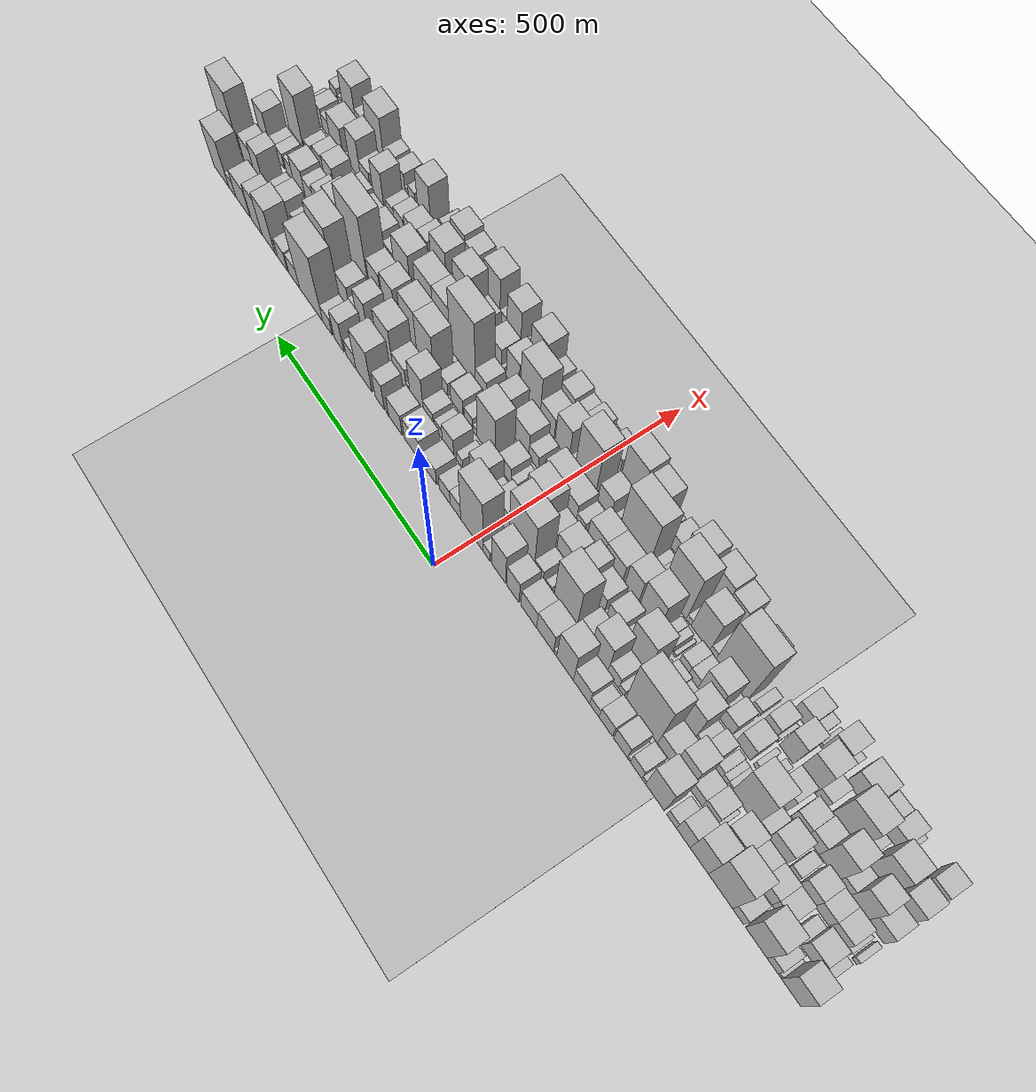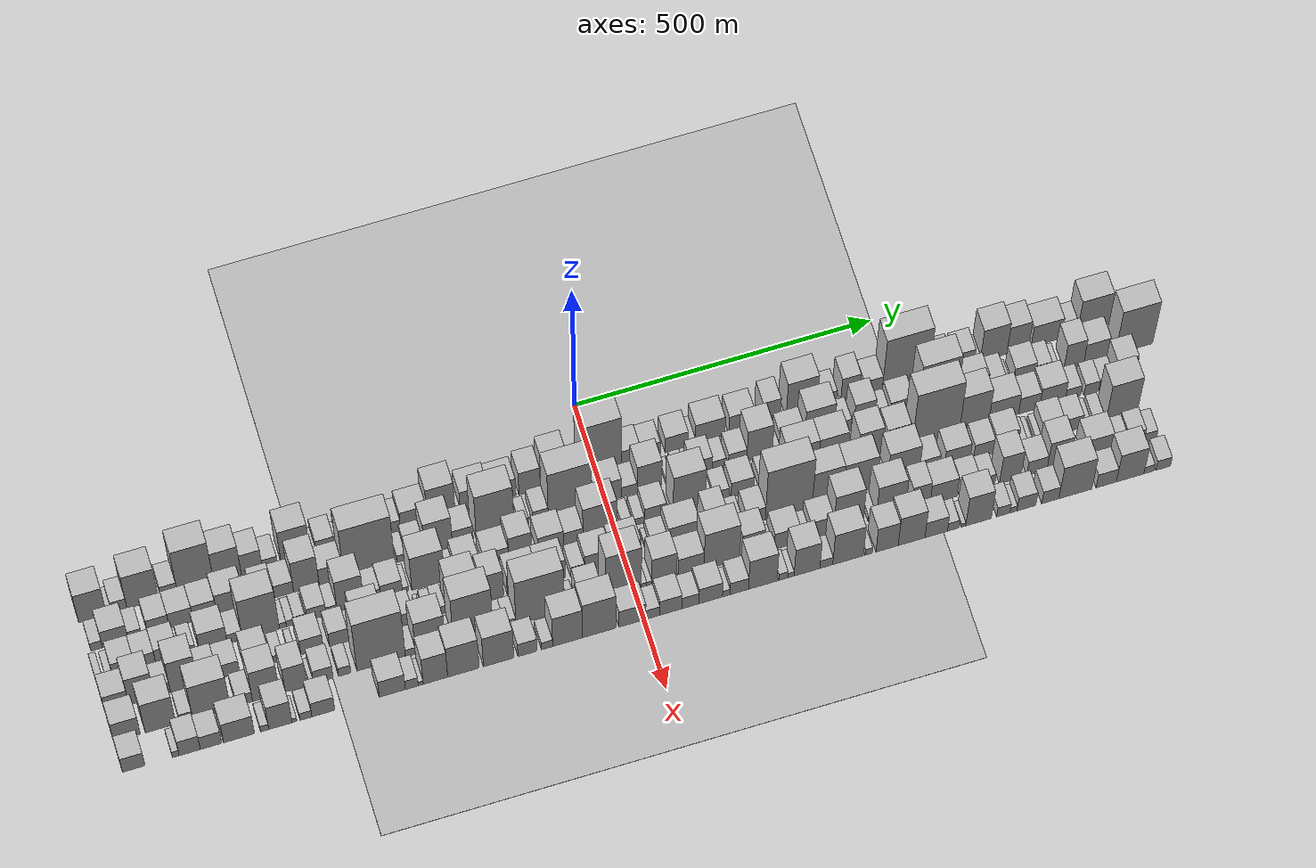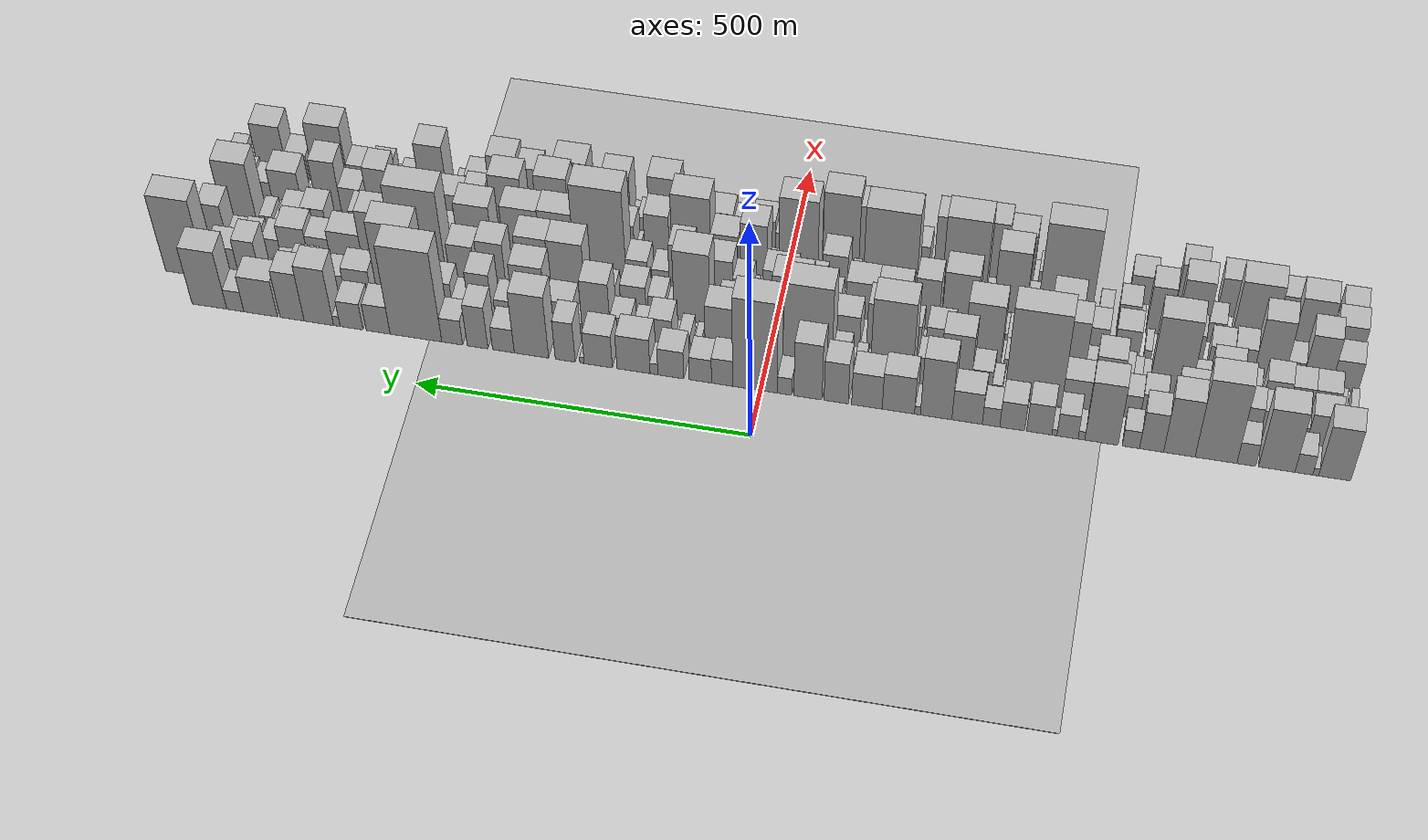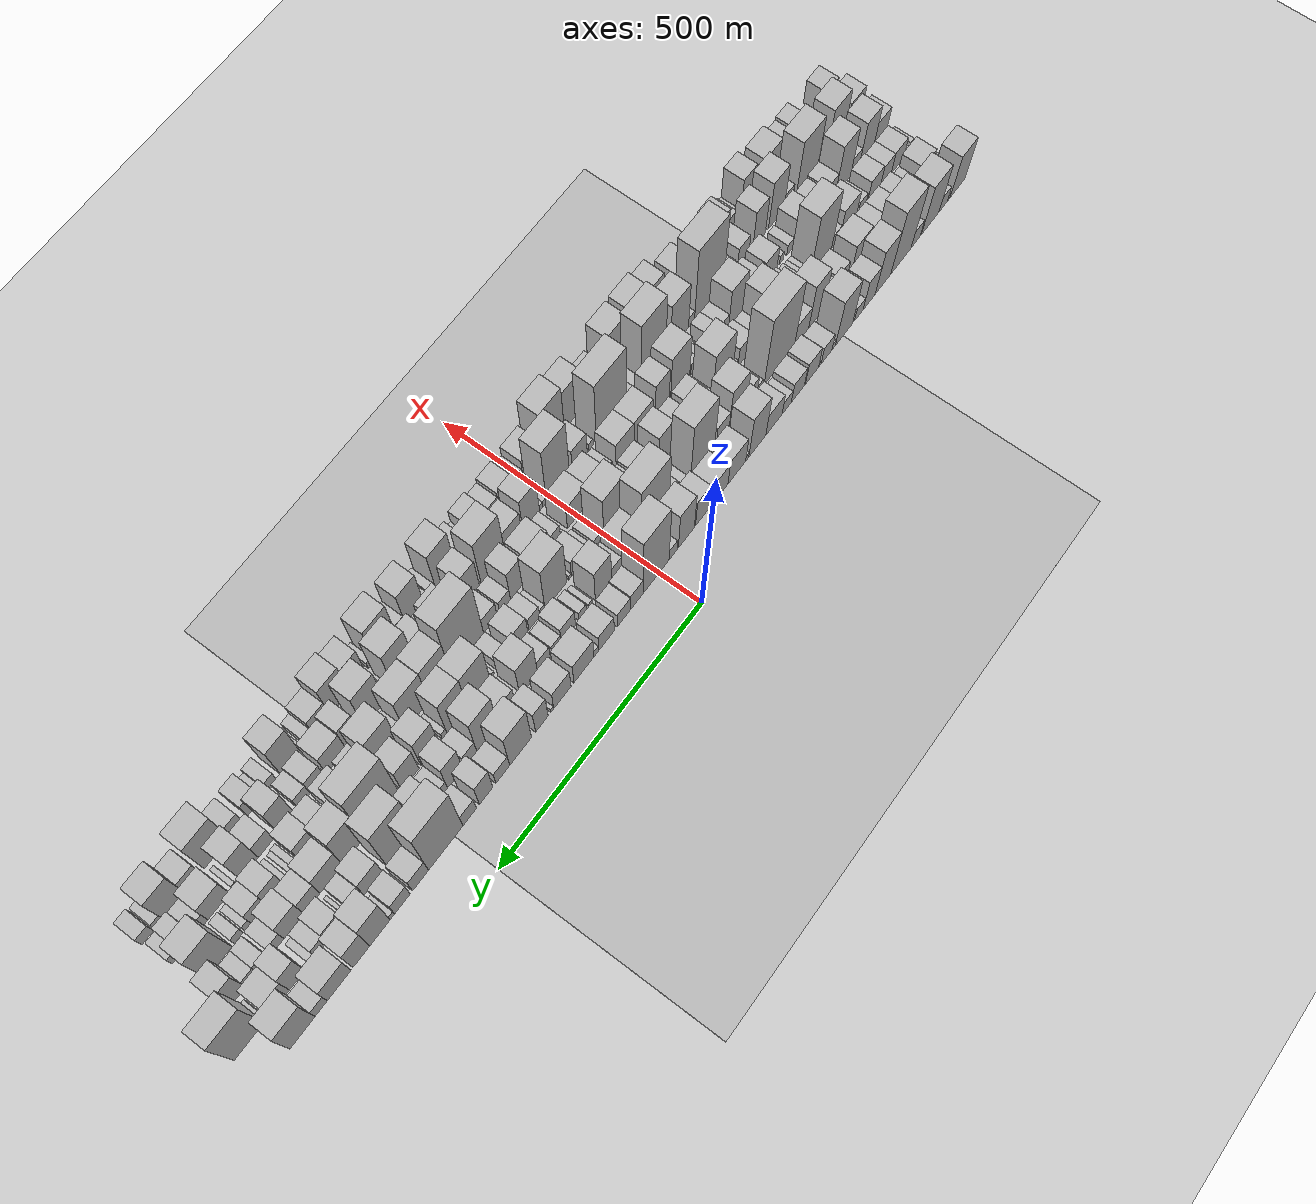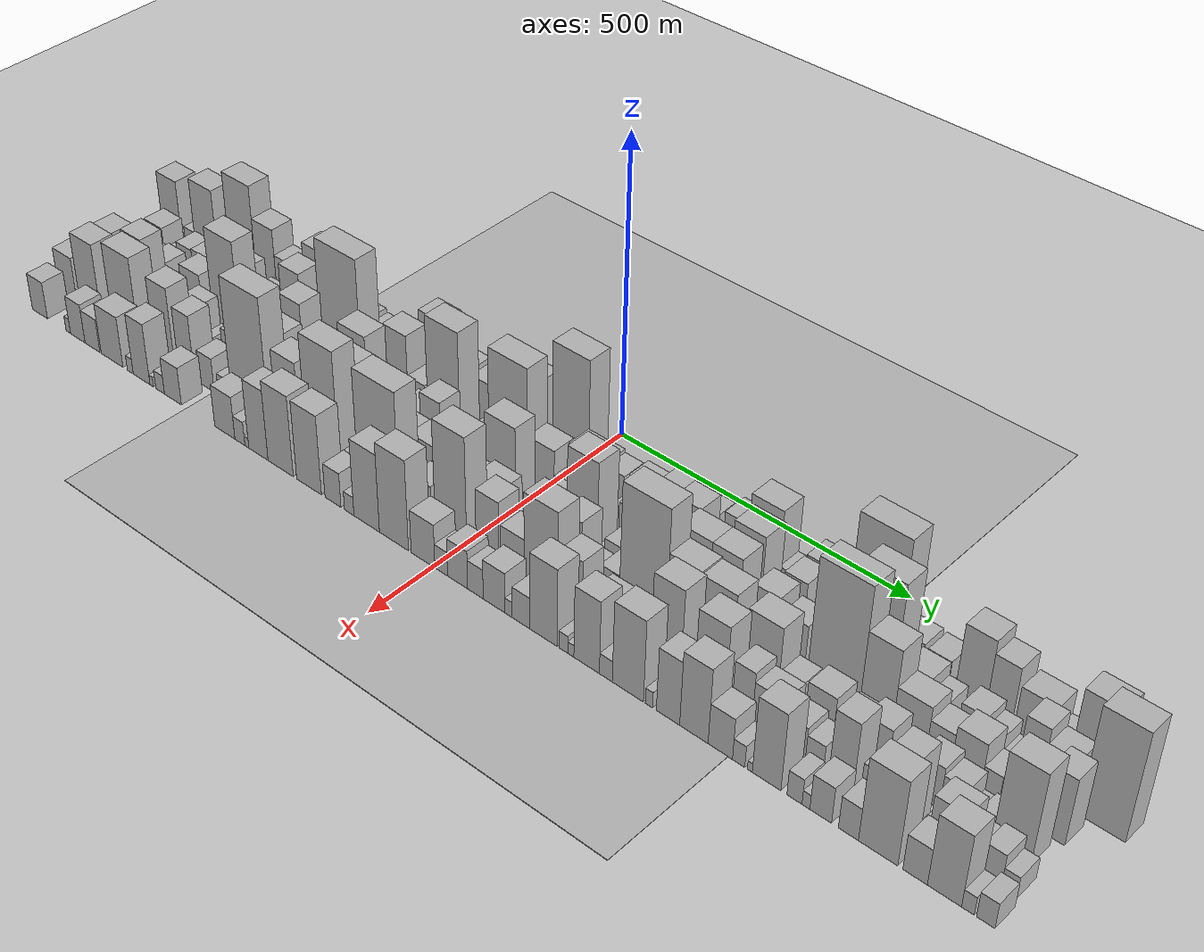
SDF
<?xml version="1.0" encoding="utf-8"?>

<sdf version="1.6">

   <world name="default">

      <gui fullscreen="0">

         <camera name="user_camera">

            <pose>-15 0 4.57585 0 0 0</pose>

            <view_controller>orbit</view_controller>

         </camera>

      </gui>

      <scene>

         <sky>

           <clouds>

             <speed>12</speed>

           </clouds>

         </sky>

         <ambient>0.4 0.4 0.4 1</ambient>

         <background>0.7 0.7 0.7 1</background>

         <shadows>1</shadows>

      </scene>

      <gravity>0 0 -9.8066</gravity>

      <magnetic_field>6e-06 2.3e-05 -4.2e-05</magnetic_field>

      <physics default="0" name="default_physics" type="ode">

         <ode>

            <solver>

               <type>quick</type>

               <iters>10</iters>

               <sor>1.0</sor>

               <use_dynamic_moi_rescaling>0</use_dynamic_moi_rescaling>

            </solver>

            <constraints>

               <cfm>0</cfm>

               <erp>0.2</erp>

               <contact_max_correcting_vel>100</contact_max_correcting_vel>

               <contact_surface_layer>0.001</contact_surface_layer>

            </constraints>

         </ode>

         <max_step_size>0.004</max_step_size>

         <real_time_factor>1</real_time_factor>

         <real_time_update_rate>250</real_time_update_rate>

      </physics>

      <light name="sun" type="directional">

         <cast_shadows>1</cast_shadows>

         <pose>0 0 10 0 0 0</pose>

         <diffuse>0.8 0.8 0.8 1</diffuse>

         <specular>0.2 0.2 0.2 1</specular>

         <attenuation>

            <range>1000</range>

            <constant>0.9</constant>

            <linear>0.01</linear>

            <quadratic>0.001</quadratic>

         </attenuation>

         <direction>-0.5 0.1 -0.9</direction>

      </light>

      <include>

         <name>ground_plane_1</name>

         <uri>model://HANNAS_ground_plane</uri>

         <pose>0 0 0  0 0 0</pose>

      </include>

      <include>

         <name>ground_plane_2</name>

         <uri>model://HANNAS_ground_plane</uri>

         <pose>100 0 0  0 0 0</pose>

      </include>

      <model name="building_1">

         <static>1</static>

         <pose frame="">100.0000 -837.0420 0 0.000000 0.000000 0.000000</pose>

         <link name="link">

            <pose frame="">0 0 63.00 0 0 0</pose>

            <collision name="collision">

               <geometry>

                  <box>

                     <size>40.0000 45.9160 126.0000</size>

                  </box>

               </geometry>

               <max_contacts>10</max_contacts>

               <surface>

                  <contact>

                     <ode/>

                  </contact>

                  <bounce/>

                  <friction>

                     <torsional>

                        <ode/>

                     </torsional>

                     <ode/>

                  </friction>

               </surface>

            </collision>

            <visual name="visual">

               <cast_shadows>0</cast_shadows>

               <geometry>

                  <box>

                     <size>40.0000 45.9160 126.0000</size>

                  </box>

               </geometry>

               <material>

                  <script>

                     <uri>model://HANNAS_wall/materials/scripts</uri>

                     <uri>model://HANNAS_wall/materials/textures</uri>

                     <name>vrc/HANNAS_wall</name>

                  </script>

               </material>

            </visual>

            <self_collide>0</self_collide>

            <enable_wind>0</enable_wind>

            <kinematic>0</kinematic>

         </link>

      </model>

      <model name="building_2">

         <static>1</static>

         <pose frame="">100.0000 -809.8941 0 0.000000 0.000000 0.000000</pose>

         <link name="link">

            <pose frame="">0 0 9.00 0 0 0</pose>

            <collision name="collision">

               <geometry>

                  <box>

                     <size>40.0000 8.3797 18.0000</size>

                  </box>

               </geometry>

               <max_contacts>10</max_contacts>

               <surface>

                  <contact>

                     <ode/>

                  </contact>

                  <bounce/>

                  <friction>

                     <torsional>

                        <ode/>

                     </torsional>

                     <ode/>

                  </friction>

               </surface>

            </collision>

            <visual name="visual">

               <cast_shadows>0</cast_shadows>

               <geometry>

                  <box>

                     <size>40.0000 8.3797 18.0000</size>

                  </box>

               </geometry>

               <material>

                  <script>

                     <uri>model://HANNAS_wall/materials/scripts</uri>

                     <uri>model://HANNAS_wall/materials/textures</uri>

                     <name>vrc/HANNAS_wall</name>

                  </script>

               </material>

            </visual>

            <self_collide>0</self_collide>

            <enable_wind>0</enable_wind>

            <kinematic>0</kinematic>

         </link>

      </model>

      <model name="building_3">

         <static>1</static>

         <pose frame="">100.0000 -792.9933 0 0.000000 0.000000 0.000000</pose>

         <link name="link">

            <pose frame="">0 0 24.00 0 0 0</pose>

            <collision name="collision">

               <geometry>

                  <box>

                     <size>40.0000 25.4219 48.0000</size>

                  </box>

               </geometry>

               <max_contacts>10</max_contacts>

               <surface>

                  <contact>

                     <ode/>

                  </contact>

                  <bounce/>

                  <friction>

                     <torsional>

                        <ode/>

                     </torsional>

                     <ode/>

                  </friction>

               </surface>

            </collision>

            <visual name="visual">

               <cast_shadows>0</cast_shadows>

               <geometry>

                  <box>

                     <size>40.0000 25.4219 48.0000</size>

                  </box>

               </geometry>

               <material>

                  <script>

                     <uri>model://HANNAS_wall/materials/scripts</uri>

                     <uri>model://HANNAS_wall/materials/textures</uri>

                     <name>vrc/HANNAS_wall</name>

                  </script>

               </material>

            </visual>

            <self_collide>0</self_collide>

            <enable_wind>0</enable_wind>

            <kinematic>0</kinematic>

         </link>

      </model>

      <model name="building_4">

         <static>1</static>

         <pose frame="">100.0000 -754.1170 0 0.000000 0.000000 0.000000</pose>

         <link name="link">

            <pose frame="">0 0 73.50 0 0 0</pose>

            <collision name="collision">

               <geometry>

                  <box>

                     <size>40.0000 52.3308 147.0000</size>

                  </box>

               </geometry>

               <max_contacts>10</max_contacts>

               <surface>

                  <contact>

                     <ode/>

                  </contact>

                  <bounce/>

                  <friction>

                     <torsional>

                        <ode/>

                     </torsional>

                     <ode/>

                  </friction>

               </surface>

            </collision>

            <visual name="visual">

               <cast_shadows>0</cast_shadows>

               <geometry>

                  <box>

                     <size>40.0000 52.3308 147.0000</size>

                  </box>

               </geometry>

               <material>

                  <script>

                     <uri>model://HANNAS_wall/materials/scripts</uri>

                     <uri>model://HANNAS_wall/materials/textures</uri>

                     <name>vrc/HANNAS_wall</name>

                  </script>

               </material>

            </visual>

            <self_collide>0</self_collide>

            <enable_wind>0</enable_wind>

            <kinematic>0</kinematic>

         </link>

      </model>

      <model name="building_5">

         <static>1</static>

         <pose frame="">100.0000 -710.3732 0 0.000000 0.000000 0.000000</pose>

         <link name="link">

            <pose frame="">0 0 27.00 0 0 0</pose>

            <collision name="collision">

               <geometry>

                  <box>

                     <size>40.0000 27.1567 54.0000</size>

                  </box>

               </geometry>

               <max_contacts>10</max_contacts>

               <surface>

                  <contact>

                     <ode/>

                  </contact>

                  <bounce/>

                  <friction>

                     <torsional>

                        <ode/>

                     </torsional>

                     <ode/>

                  </friction>

               </surface>

            </collision>

            <visual name="visual">

               <cast_shadows>0</cast_shadows>

               <geometry>

                  <box>

                     <size>40.0000 27.1567 54.0000</size>

                  </box>

               </geometry>

               <material>

                  <script>

                     <uri>model://HANNAS_wall/materials/scripts</uri>

                     <uri>model://HANNAS_wall/materials/textures</uri>

                     <name>vrc/HANNAS_wall</name>

                  </script>

               </material>

            </visual>

            <self_collide>0</self_collide>

            <enable_wind>0</enable_wind>

            <kinematic>0</kinematic>

         </link>

      </model>

      <model name="building_6">

         <static>1</static>

         <pose frame="">100.0000 -666.7493 0 0.000000 0.000000 0.000000</pose>

         <link name="link">

            <pose frame="">0 0 97.50 0 0 0</pose>

            <collision name="collision">

               <geometry>

                  <box>

                     <size>40.0000 60.0911 195.0000</size>

                  </box>

               </geometry>

               <max_contacts>10</max_contacts>

               <surface>

                  <contact>

                     <ode/>

                  </contact>

                  <bounce/>

                  <friction>

                     <torsional>

                        <ode/>

                     </torsional>

                     <ode/>

                  </friction>

               </surface>

            </collision>

            <visual name="visual">

               <cast_shadows>0</cast_shadows>

               <geometry>

                  <box>

                     <size>40.0000 60.0911 195.0000</size>

                  </box>

               </geometry>

               <material>

                  <script>

                     <uri>model://HANNAS_wall/materials/scripts</uri>

                     <uri>model://HANNAS_wall/materials/textures</uri>

                     <name>vrc/HANNAS_wall</name>

                  </script>

               </material>

            </visual>

            <self_collide>0</self_collide>

            <enable_wind>0</enable_wind>

            <kinematic>0</kinematic>

         </link>

      </model>

      <model name="building_7">

         <static>1</static>

         <pose frame="">100.0000 -613.9313 0 0.000000 0.000000 0.000000</pose>

         <link name="link">

            <pose frame="">0 0 69.00 0 0 0</pose>

            <collision name="collision">

               <geometry>

                  <box>

                     <size>40.0000 45.5448 138.0000</size>

                  </box>

               </geometry>

               <max_contacts>10</max_contacts>

               <surface>

                  <contact>

                     <ode/>

                  </contact>

                  <bounce/>

                  <friction>

                     <torsional>

                        <ode/>

                     </torsional>

                     <ode/>

                  </friction>

               </surface>

            </collision>

            <visual name="visual">

               <cast_shadows>0</cast_shadows>

               <geometry>

                  <box>

                     <size>40.0000 45.5448 138.0000</size>

                  </box>

               </geometry>

               <material>

                  <script>

                     <uri>model://HANNAS_wall/materials/scripts</uri>

                     <uri>model://HANNAS_wall/materials/textures</uri>

                     <name>vrc/HANNAS_wall</name>

                  </script>

               </material>

            </visual>

            <self_collide>0</self_collide>

            <enable_wind>0</enable_wind>

            <kinematic>0</kinematic>

         </link>

      </model>

      <model name="building_8">

         <static>1</static>

         <pose frame="">100.0000 -573.7703 0 0.000000 0.000000 0.000000</pose>

         <link name="link">

            <pose frame="">0 0 46.50 0 0 0</pose>

            <collision name="collision">

               <geometry>

                  <box>

                     <size>40.0000 34.7772 93.0000</size>

                  </box>

               </geometry>

               <max_contacts>10</max_contacts>

               <surface>

                  <contact>

                     <ode/>

                  </contact>

                  <bounce/>

                  <friction>

                     <torsional>

                        <ode/>

                     </torsional>

                     <ode/>

                  </friction>

               </surface>

            </collision>

            <visual name="visual">

               <cast_shadows>0</cast_shadows>

               <geometry>

                  <box>

                     <size>40.0000 34.7772 93.0000</size>

                  </box>

               </geometry>

               <material>

                  <script>

                     <uri>model://HANNAS_wall/materials/scripts</uri>

                     <uri>model://HANNAS_wall/materials/textures</uri>

                     <name>vrc/HANNAS_wall</name>

                  </script>

               </material>

            </visual>

            <self_collide>0</self_collide>

            <enable_wind>0</enable_wind>

            <kinematic>0</kinematic>

         </link>

      </model>

      <model name="building_9">

         <static>1</static>

         <pose frame="">100.0000 -543.8166 0 0.000000 0.000000 0.000000</pose>

         <link name="link">

            <pose frame="">0 0 21.00 0 0 0</pose>

            <collision name="collision">

               <geometry>

                  <box>

                     <size>40.0000 25.1302 42.0000</size>

                  </box>

               </geometry>

               <max_contacts>10</max_contacts>

               <surface>

                  <contact>

                     <ode/>

                  </contact>

                  <bounce/>

                  <friction>

                     <torsional>

                        <ode/>

                     </torsional>

                     <ode/>

                  </friction>

               </surface>

            </collision>

            <visual name="visual">

               <cast_shadows>0</cast_shadows>

               <geometry>

                  <box>

                     <size>40.0000 25.1302 42.0000</size>

                  </box>

               </geometry>

               <material>

                  <script>

                     <uri>model://HANNAS_wall/materials/scripts</uri>

                     <uri>model://HANNAS_wall/materials/textures</uri>

                     <name>vrc/HANNAS_wall</name>

                  </script>

               </material>

            </visual>

            <self_collide>0</self_collide>

            <enable_wind>0</enable_wind>

            <kinematic>0</kinematic>

         </link>

      </model>

      <model name="building_10">

         <static>1</static>

         <pose frame="">100.0000 -501.0413 0 0.000000 0.000000 0.000000</pose>

         <link name="link">

            <pose frame="">0 0 73.50 0 0 0</pose>

            <collision name="collision">

               <geometry>

                  <box>

                     <size>40.0000 48.4204 147.0000</size>

                  </box>

               </geometry>

               <max_contacts>10</max_contacts>

               <surface>

                  <contact>

                     <ode/>

                  </contact>

                  <bounce/>

                  <friction>

                     <torsional>

                        <ode/>

                     </torsional>

                     <ode/>

                  </friction>

               </surface>

            </collision>

            <visual name="visual">

               <cast_shadows>0</cast_shadows>

               <geometry>

                  <box>

                     <size>40.0000 48.4204 147.0000</size>

                  </box>

               </geometry>

               <material>

                  <script>

                     <uri>model://HANNAS_wall/materials/scripts</uri>

                     <uri>model://HANNAS_wall/materials/textures</uri>

                     <name>vrc/HANNAS_wall</name>

                  </script>

               </material>

            </visual>

            <self_collide>0</self_collide>

            <enable_wind>0</enable_wind>

            <kinematic>0</kinematic>

         </link>

      </model>

      <model name="building_11">

         <static>1</static>

         <pose frame="">100.0000 -471.9113 0 0.000000 0.000000 0.000000</pose>

         <link name="link">

            <pose frame="">0 0 10.50 0 0 0</pose>

            <collision name="collision">

               <geometry>

                  <box>

                     <size>40.0000 9.8395 21.0000</size>

                  </box>

               </geometry>

               <max_contacts>10</max_contacts>

               <surface>

                  <contact>

                     <ode/>

                  </contact>

                  <bounce/>

                  <friction>

                     <torsional>

                        <ode/>

                     </torsional>

                     <ode/>

                  </friction>

               </surface>

            </collision>

            <visual name="visual">

               <cast_shadows>0</cast_shadows>

               <geometry>

                  <box>

                     <size>40.0000 9.8395 21.0000</size>

                  </box>

               </geometry>

               <material>

                  <script>

                     <uri>model://HANNAS_wall/materials/scripts</uri>

                     <uri>model://HANNAS_wall/materials/textures</uri>

                     <name>vrc/HANNAS_wall</name>

                  </script>

               </material>

            </visual>

            <self_collide>0</self_collide>

            <enable_wind>0</enable_wind>

            <kinematic>0</kinematic>

         </link>

      </model>

      <model name="building_12">

         <static>1</static>

         <pose frame="">100.0000 -451.5993 0 0.000000 0.000000 0.000000</pose>

         <link name="link">

            <pose frame="">0 0 28.50 0 0 0</pose>

            <collision name="collision">

               <geometry>

                  <box>

                     <size>40.0000 30.7844 57.0000</size>

                  </box>

               </geometry>

               <max_contacts>10</max_contacts>

               <surface>

                  <contact>

                     <ode/>

                  </contact>

                  <bounce/>

                  <friction>

                     <torsional>

                        <ode/>

                     </torsional>

                     <ode/>

                  </friction>

               </surface>

            </collision>

            <visual name="visual">

               <cast_shadows>0</cast_shadows>

               <geometry>

                  <box>

                     <size>40.0000 30.7844 57.0000</size>

                  </box>

               </geometry>

               <material>

                  <script>

                     <uri>model://HANNAS_wall/materials/scripts</uri>

                     <uri>model://HANNAS_wall/materials/textures</uri>

                     <name>vrc/HANNAS_wall</name>

                  </script>

               </material>

            </visual>

            <self_collide>0</self_collide>

            <enable_wind>0</enable_wind>

            <kinematic>0</kinematic>

         </link>

      </model>

      <model name="building_13">

         <static>1</static>

         <pose frame="">100.0000 -432.5059 0 0.000000 0.000000 0.000000</pose>

         <link name="link">

            <pose frame="">0 0 7.50 0 0 0</pose>

            <collision name="collision">

               <geometry>

                  <box>

                     <size>40.0000 7.4024 15.0000</size>

                  </box>

               </geometry>

               <max_contacts>10</max_contacts>

               <surface>

                  <contact>

                     <ode/>

                  </contact>

                  <bounce/>

                  <friction>

                     <torsional>

                        <ode/>

                     </torsional>

                     <ode/>

                  </friction>

               </surface>

            </collision>

            <visual name="visual">

               <cast_shadows>0</cast_shadows>

               <geometry>

                  <box>

                     <size>40.0000 7.4024 15.0000</size>

                  </box>

               </geometry>

               <material>

                  <script>

                     <uri>model://HANNAS_wall/materials/scripts</uri>

                     <uri>model://HANNAS_wall/materials/textures</uri>

                     <name>vrc/HANNAS_wall</name>

                  </script>

               </material>

            </visual>

            <self_collide>0</self_collide>

            <enable_wind>0</enable_wind>

            <kinematic>0</kinematic>

         </link>

      </model>

      <model name="building_14">

         <static>1</static>

         <pose frame="">100.0000 -410.4039 0 0.000000 0.000000 0.000000</pose>

         <link name="link">

            <pose frame="">0 0 36.00 0 0 0</pose>

            <collision name="collision">

               <geometry>

                  <box>

                     <size>40.0000 36.8017 72.0000</size>

                  </box>

               </geometry>

               <max_contacts>10</max_contacts>

               <surface>

                  <contact>

                     <ode/>

                  </contact>

                  <bounce/>

                  <friction>

                     <torsional>

                        <ode/>

                     </torsional>

                     <ode/>

                  </friction>

               </surface>

            </collision>

            <visual name="visual">

               <cast_shadows>0</cast_shadows>

               <geometry>

                  <box>

                     <size>40.0000 36.8017 72.0000</size>

                  </box>

               </geometry>

               <material>

                  <script>

                     <uri>model://HANNAS_wall/materials/scripts</uri>

                     <uri>model://HANNAS_wall/materials/textures</uri>

                     <name>vrc/HANNAS_wall</name>

                  </script>

               </material>

            </visual>

            <self_collide>0</self_collide>

            <enable_wind>0</enable_wind>

            <kinematic>0</kinematic>

         </link>

      </model>

      <model name="building_15">

         <static>1</static>

         <pose frame="">100.0000 -370.9000 0 0.000000 0.000000 0.000000</pose>

         <link name="link">

            <pose frame="">0 0 33.00 0 0 0</pose>

            <collision name="collision">

               <geometry>

                  <box>

                     <size>40.0000 36.2062 66.0000</size>

                  </box>

               </geometry>

               <max_contacts>10</max_contacts>

               <surface>

                  <contact>

                     <ode/>

                  </contact>

                  <bounce/>

                  <friction>

                     <torsional>

                        <ode/>

                     </torsional>

                     <ode/>

                  </friction>

               </surface>

            </collision>

            <visual name="visual">

               <cast_shadows>0</cast_shadows>

               <geometry>

                  <box>

                     <size>40.0000 36.2062 66.0000</size>

                  </box>

               </geometry>

               <material>

                  <script>

                     <uri>model://HANNAS_wall/materials/scripts</uri>

                     <uri>model://HANNAS_wall/materials/textures</uri>

                     <name>vrc/HANNAS_wall</name>

                  </script>

               </material>

            </visual>

            <self_collide>0</self_collide>

            <enable_wind>0</enable_wind>

            <kinematic>0</kinematic>

         </link>

      </model>

      <model name="building_16">

         <static>1</static>

         <pose frame="">100.0000 -339.9211 0 0.000000 0.000000 0.000000</pose>

         <link name="link">

            <pose frame="">0 0 22.50 0 0 0</pose>

            <collision name="collision">

               <geometry>

                  <box>

                     <size>40.0000 25.7516 45.0000</size>

                  </box>

               </geometry>

               <max_contacts>10</max_contacts>

               <surface>

                  <contact>

                     <ode/>

                  </contact>

                  <bounce/>

                  <friction>

                     <torsional>

                        <ode/>

                     </torsional>

                     <ode/>

                  </friction>

               </surface>

            </collision>

            <visual name="visual">

               <cast_shadows>0</cast_shadows>

               <geometry>

                  <box>

                     <size>40.0000 25.7516 45.0000</size>

                  </box>

               </geometry>

               <material>

                  <script>

                     <uri>model://HANNAS_wall/materials/scripts</uri>

                     <uri>model://HANNAS_wall/materials/textures</uri>

                     <name>vrc/HANNAS_wall</name>

                  </script>

               </material>

            </visual>

            <self_collide>0</self_collide>

            <enable_wind>0</enable_wind>

            <kinematic>0</kinematic>

         </link>

      </model>

      <model name="building_17">

         <static>1</static>

         <pose frame="">100.0000 -304.7581 0 0.000000 0.000000 0.000000</pose>

         <link name="link">

            <pose frame="">0 0 37.50 0 0 0</pose>

            <collision name="collision">

               <geometry>

                  <box>

                     <size>40.0000 44.5744 75.0000</size>

                  </box>

               </geometry>

               <max_contacts>10</max_contacts>

               <surface>

                  <contact>

                     <ode/>

                  </contact>

                  <bounce/>

                  <friction>

                     <torsional>

                        <ode/>

                     </torsional>

                     <ode/>

                  </friction>

               </surface>

            </collision>

            <visual name="visual">

               <cast_shadows>0</cast_shadows>

               <geometry>

                  <box>

                     <size>40.0000 44.5744 75.0000</size>

                  </box>

               </geometry>

               <material>

                  <script>

                     <uri>model://HANNAS_wall/materials/scripts</uri>

                     <uri>model://HANNAS_wall/materials/textures</uri>

                     <name>vrc/HANNAS_wall</name>

                  </script>

               </material>

            </visual>

            <self_collide>0</self_collide>

            <enable_wind>0</enable_wind>

            <kinematic>0</kinematic>

         </link>

      </model>

      <model name="building_18">

         <static>1</static>

         <pose frame="">100.0000 -259.2859 0 0.000000 0.000000 0.000000</pose>

         <link name="link">

            <pose frame="">0 0 72.00 0 0 0</pose>

            <collision name="collision">

               <geometry>

                  <box>

                     <size>40.0000 46.3700 144.0000</size>

                  </box>

               </geometry>

               <max_contacts>10</max_contacts>

               <surface>

                  <contact>

                     <ode/>

                  </contact>

                  <bounce/>

                  <friction>

                     <torsional>

                        <ode/>

                     </torsional>

                     <ode/>

                  </friction>

               </surface>

            </collision>

            <visual name="visual">

               <cast_shadows>0</cast_shadows>

               <geometry>

                  <box>

                     <size>40.0000 46.3700 144.0000</size>

                  </box>

               </geometry>

               <material>

                  <script>

                     <uri>model://HANNAS_wall/materials/scripts</uri>

                     <uri>model://HANNAS_wall/materials/textures</uri>

                     <name>vrc/HANNAS_wall</name>

                  </script>

               </material>

            </visual>

            <self_collide>0</self_collide>

            <enable_wind>0</enable_wind>

            <kinematic>0</kinematic>

         </link>

      </model>

      <model name="building_19">

         <static>1</static>

         <pose frame="">100.0000 -231.8108 0 0.000000 0.000000 0.000000</pose>

         <link name="link">

            <pose frame="">0 0 10.50 0 0 0</pose>

            <collision name="collision">

               <geometry>

                  <box>

                     <size>40.0000 8.5801 21.0000</size>

                  </box>

               </geometry>

               <max_contacts>10</max_contacts>

               <surface>

                  <contact>

                     <ode/>

                  </contact>

                  <bounce/>

                  <friction>

                     <torsional>

                        <ode/>

                     </torsional>

                     <ode/>

                  </friction>

               </surface>

            </collision>

            <visual name="visual">

               <cast_shadows>0</cast_shadows>

               <geometry>

                  <box>

                     <size>40.0000 8.5801 21.0000</size>

                  </box>

               </geometry>

               <material>

                  <script>

                     <uri>model://HANNAS_wall/materials/scripts</uri>

                     <uri>model://HANNAS_wall/materials/textures</uri>

                     <name>vrc/HANNAS_wall</name>

                  </script>

               </material>

            </visual>

            <self_collide>0</self_collide>

            <enable_wind>0</enable_wind>

            <kinematic>0</kinematic>

         </link>

      </model>

      <model name="building_20">

         <static>1</static>

         <pose frame="">100.0000 -203.7147 0 0.000000 0.000000 0.000000</pose>

         <link name="link">

            <pose frame="">0 0 45.00 0 0 0</pose>

            <collision name="collision">

               <geometry>

                  <box>

                     <size>40.0000 47.6121 90.0000</size>

                  </box>

               </geometry>

               <max_contacts>10</max_contacts>

               <surface>

                  <contact>

                     <ode/>

                  </contact>

                  <bounce/>

                  <friction>

                     <torsional>

                        <ode/>

                     </torsional>

                     <ode/>

                  </friction>

               </surface>

            </collision>

            <visual name="visual">

               <cast_shadows>0</cast_shadows>

               <geometry>

                  <box>

                     <size>40.0000 47.6121 90.0000</size>

                  </box>

               </geometry>

               <material>

                  <script>

                     <uri>model://HANNAS_wall/materials/scripts</uri>

                     <uri>model://HANNAS_wall/materials/textures</uri>

                     <name>vrc/HANNAS_wall</name>

                  </script>

               </material>

            </visual>

            <self_collide>0</self_collide>

            <enable_wind>0</enable_wind>

            <kinematic>0</kinematic>

         </link>

      </model>

      <model name="building_21">

         <static>1</static>

         <pose frame="">100.0000 -157.2744 0 0.000000 0.000000 0.000000</pose>

         <link name="link">

            <pose frame="">0 0 40.50 0 0 0</pose>

            <collision name="collision">

               <geometry>

                  <box>

                     <size>40.0000 45.2687 81.0000</size>

                  </box>

               </geometry>

               <max_contacts>10</max_contacts>

               <surface>

                  <contact>

                     <ode/>

                  </contact>

                  <bounce/>

                  <friction>

                     <torsional>

                        <ode/>

                     </torsional>

                     <ode/>

                  </friction>

               </surface>

            </collision>

            <visual name="visual">

               <cast_shadows>0</cast_shadows>

               <geometry>

                  <box>

                     <size>40.0000 45.2687 81.0000</size>

                  </box>

               </geometry>

               <material>

                  <script>

                     <uri>model://HANNAS_wall/materials/scripts</uri>

                     <uri>model://HANNAS_wall/materials/textures</uri>

                     <name>vrc/HANNAS_wall</name>

                  </script>

               </material>

            </visual>

            <self_collide>0</self_collide>

            <enable_wind>0</enable_wind>

            <kinematic>0</kinematic>

         </link>

      </model>

      <model name="building_22">

         <static>1</static>

         <pose frame="">100.0000 -111.7623 0 0.000000 0.000000 0.000000</pose>

         <link name="link">

            <pose frame="">0 0 49.50 0 0 0</pose>

            <collision name="collision">

               <geometry>

                  <box>

                     <size>40.0000 35.7554 99.0000</size>

                  </box>

               </geometry>

               <max_contacts>10</max_contacts>

               <surface>

                  <contact>

                     <ode/>

                  </contact>

                  <bounce/>

                  <friction>

                     <torsional>

                        <ode/>

                     </torsional>

                     <ode/>

                  </friction>

               </surface>

            </collision>

            <visual name="visual">

               <cast_shadows>0</cast_shadows>

               <geometry>

                  <box>

                     <size>40.0000 35.7554 99.0000</size>

                  </box>

               </geometry>

               <material>

                  <script>

                     <uri>model://HANNAS_wall/materials/scripts</uri>

                     <uri>model://HANNAS_wall/materials/textures</uri>

                     <name>vrc/HANNAS_wall</name>

                  </script>

               </material>

            </visual>

            <self_collide>0</self_collide>

            <enable_wind>0</enable_wind>

            <kinematic>0</kinematic>

         </link>

      </model>

      <model name="building_23">

         <static>1</static>

         <pose frame="">100.0000 -70.0096 0 0.000000 0.000000 0.000000</pose>

         <link name="link">

            <pose frame="">0 0 67.50 0 0 0</pose>

            <collision name="collision">

               <geometry>

                  <box>

                     <size>40.0000 41.7500 135.0000</size>

                  </box>

               </geometry>

               <max_contacts>10</max_contacts>

               <surface>

                  <contact>

                     <ode/>

                  </contact>

                  <bounce/>

                  <friction>

                     <torsional>

                        <ode/>

                     </torsional>

                     <ode/>

                  </friction>

               </surface>

            </collision>

            <visual name="visual">

               <cast_shadows>0</cast_shadows>

               <geometry>

                  <box>

                     <size>40.0000 41.7500 135.0000</size>

                  </box>

               </geometry>

               <material>

                  <script>

                     <uri>model://HANNAS_wall/materials/scripts</uri>

                     <uri>model://HANNAS_wall/materials/textures</uri>

                     <name>vrc/HANNAS_wall</name>

                  </script>

               </material>

            </visual>

            <self_collide>0</self_collide>

            <enable_wind>0</enable_wind>

            <kinematic>0</kinematic>

         </link>

      </model>

      <model name="building_24">

         <static>1</static>

         <pose frame="">100.0000 -35.3545 0 0.000000 0.000000 0.000000</pose>

         <link name="link">

            <pose frame="">0 0 21.00 0 0 0</pose>

            <collision name="collision">

               <geometry>

                  <box>

                     <size>40.0000 21.5600 42.0000</size>

                  </box>

               </geometry>

               <max_contacts>10</max_contacts>

               <surface>

                  <contact>

                     <ode/>

                  </contact>

                  <bounce/>

                  <friction>

                     <torsional>

                        <ode/>

                     </torsional>

                     <ode/>

                  </friction>

               </surface>

            </collision>

            <visual name="visual">

               <cast_shadows>0</cast_shadows>

               <geometry>

                  <box>

                     <size>40.0000 21.5600 42.0000</size>

                  </box>

               </geometry>

               <material>

                  <script>

                     <uri>model://HANNAS_wall/materials/scripts</uri>

                     <uri>model://HANNAS_wall/materials/textures</uri>

                     <name>vrc/HANNAS_wall</name>

                  </script>

               </material>

            </visual>

            <self_collide>0</self_collide>

            <enable_wind>0</enable_wind>

            <kinematic>0</kinematic>

         </link>

      </model>

      <model name="building_25">

         <static>1</static>

         <pose frame="">100.0000 8.6502 0 0.000000 0.000000 0.000000</pose>

         <link name="link">

            <pose frame="">0 0 109.50 0 0 0</pose>

            <collision name="collision">

               <geometry>

                  <box>

                     <size>40.0000 66.4493 219.0000</size>

                  </box>

               </geometry>

               <max_contacts>10</max_contacts>

               <surface>

                  <contact>

                     <ode/>

                  </contact>

                  <bounce/>

                  <friction>

                     <torsional>

                        <ode/>

                     </torsional>

                     <ode/>

                  </friction>

               </surface>

            </collision>

            <visual name="visual">

               <cast_shadows>0</cast_shadows>

               <geometry>

                  <box>

                     <size>40.0000 66.4493 219.0000</size>

                  </box>

               </geometry>

               <material>

                  <script>

                     <uri>model://HANNAS_wall/materials/scripts</uri>

                     <uri>model://HANNAS_wall/materials/textures</uri>

                     <name>vrc/HANNAS_wall</name>

                  </script>

               </material>

            </visual>

            <self_collide>0</self_collide>

            <enable_wind>0</enable_wind>

            <kinematic>0</kinematic>

         </link>

      </model>

      <model name="building_26">

         <static>1</static>

         <pose frame="">100.0000 57.7635 0 0.000000 0.000000 0.000000</pose>

         <link name="link">

            <pose frame="">0 0 31.50 0 0 0</pose>

            <collision name="collision">

               <geometry>

                  <box>

                     <size>40.0000 31.7774 63.0000</size>

                  </box>

               </geometry>

               <max_contacts>10</max_contacts>

               <surface>

                  <contact>

                     <ode/>

                  </contact>

                  <bounce/>

                  <friction>

                     <torsional>

                        <ode/>

                     </torsional>

                     <ode/>

                  </friction>

               </surface>

            </collision>

            <visual name="visual">

               <cast_shadows>0</cast_shadows>

               <geometry>

                  <box>

                     <size>40.0000 31.7774 63.0000</size>

                  </box>

               </geometry>

               <material>

                  <script>

                     <uri>model://HANNAS_wall/materials/scripts</uri>

                     <uri>model://HANNAS_wall/materials/textures</uri>

                     <name>vrc/HANNAS_wall</name>

                  </script>

               </material>

            </visual>

            <self_collide>0</self_collide>

            <enable_wind>0</enable_wind>

            <kinematic>0</kinematic>

         </link>

      </model>

      <model name="building_27">

         <static>1</static>

         <pose frame="">100.0000 90.3993 0 0.000000 0.000000 0.000000</pose>

         <link name="link">

            <pose frame="">0 0 28.50 0 0 0</pose>

            <collision name="collision">

               <geometry>

                  <box>

                     <size>40.0000 33.4941 57.0000</size>

                  </box>

               </geometry>

               <max_contacts>10</max_contacts>

               <surface>

                  <contact>

                     <ode/>

                  </contact>

                  <bounce/>

                  <friction>

                     <torsional>

                        <ode/>

                     </torsional>

                     <ode/>

                  </friction>

               </surface>

            </collision>

            <visual name="visual">

               <cast_shadows>0</cast_shadows>

               <geometry>

                  <box>

                     <size>40.0000 33.4941 57.0000</size>

                  </box>

               </geometry>

               <material>

                  <script>

                     <uri>model://HANNAS_wall/materials/scripts</uri>

                     <uri>model://HANNAS_wall/materials/textures</uri>

                     <name>vrc/HANNAS_wall</name>

                  </script>

               </material>

            </visual>

            <self_collide>0</self_collide>

            <enable_wind>0</enable_wind>

            <kinematic>0</kinematic>

         </link>

      </model>

      <model name="building_28">

         <static>1</static>

         <pose frame="">100.0000 134.5882 0 0.000000 0.000000 0.000000</pose>

         <link name="link">

            <pose frame="">0 0 33.00 0 0 0</pose>

            <collision name="collision">

               <geometry>

                  <box>

                     <size>40.0000 38.8838 66.0000</size>

                  </box>

               </geometry>

               <max_contacts>10</max_contacts>

               <surface>

                  <contact>

                     <ode/>

                  </contact>

                  <bounce/>

                  <friction>

                     <torsional>

                        <ode/>

                     </torsional>

                     <ode/>

                  </friction>

               </surface>

            </collision>

            <visual name="visual">

               <cast_shadows>0</cast_shadows>

               <geometry>

                  <box>

                     <size>40.0000 38.8838 66.0000</size>

                  </box>

               </geometry>

               <material>

                  <script>

                     <uri>model://HANNAS_wall/materials/scripts</uri>

                     <uri>model://HANNAS_wall/materials/textures</uri>

                     <name>vrc/HANNAS_wall</name>

                  </script>

               </material>

            </visual>

            <self_collide>0</self_collide>

            <enable_wind>0</enable_wind>

            <kinematic>0</kinematic>

         </link>

      </model>

      <model name="building_29">

         <static>1</static>

         <pose frame="">100.0000 159.8942 0 0.000000 0.000000 0.000000</pose>

         <link name="link">

            <pose frame="">0 0 13.50 0 0 0</pose>

            <collision name="collision">

               <geometry>

                  <box>

                     <size>40.0000 11.7282 27.0000</size>

                  </box>

               </geometry>

               <max_contacts>10</max_contacts>

               <surface>

                  <contact>

                     <ode/>

                  </contact>

                  <bounce/>

                  <friction>

                     <torsional>

                        <ode/>

                     </torsional>

                     <ode/>

                  </friction>

               </surface>

            </collision>

            <visual name="visual">

               <cast_shadows>0</cast_shadows>

               <geometry>

                  <box>

                     <size>40.0000 11.7282 27.0000</size>

                  </box>

               </geometry>

               <material>

                  <script>

                     <uri>model://HANNAS_wall/materials/scripts</uri>

                     <uri>model://HANNAS_wall/materials/textures</uri>

                     <name>vrc/HANNAS_wall</name>

                  </script>

               </material>

            </visual>

            <self_collide>0</self_collide>

            <enable_wind>0</enable_wind>

            <kinematic>0</kinematic>

         </link>

      </model>

      <model name="building_30">

         <static>1</static>

         <pose frame="">100.0000 190.6563 0 0.000000 0.000000 0.000000</pose>

         <link name="link">

            <pose frame="">0 0 42.00 0 0 0</pose>

            <collision name="collision">

               <geometry>

                  <box>

                     <size>40.0000 49.7961 84.0000</size>

                  </box>

               </geometry>

               <max_contacts>10</max_contacts>

               <surface>

                  <contact>

                     <ode/>

                  </contact>

                  <bounce/>

                  <friction>

                     <torsional>

                        <ode/>

                     </torsional>

                     <ode/>

                  </friction>

               </surface>

            </collision>

            <visual name="visual">

               <cast_shadows>0</cast_shadows>

               <geometry>

                  <box>

                     <size>40.0000 49.7961 84.0000</size>

                  </box>

               </geometry>

               <material>

                  <script>

                     <uri>model://HANNAS_wall/materials/scripts</uri>

                     <uri>model://HANNAS_wall/materials/textures</uri>

                     <name>vrc/HANNAS_wall</name>

                  </script>

               </material>

            </visual>

            <self_collide>0</self_collide>

            <enable_wind>0</enable_wind>

            <kinematic>0</kinematic>

         </link>

      </model>

      <model name="building_31">

         <static>1</static>

         <pose frame="">100.0000 243.7767 0 0.000000 0.000000 0.000000</pose>

         <link name="link">

            <pose frame="">0 0 39.00 0 0 0</pose>

            <collision name="collision">

               <geometry>

                  <box>

                     <size>40.0000 42.4446 78.0000</size>

                  </box>

               </geometry>

               <max_contacts>10</max_contacts>

               <surface>

                  <contact>

                     <ode/>

                  </contact>

                  <bounce/>

                  <friction>

                     <torsional>

                        <ode/>

                     </torsional>

                     <ode/>

                  </friction>

               </surface>

            </collision>

            <visual name="visual">

               <cast_shadows>0</cast_shadows>

               <geometry>

                  <box>

                     <size>40.0000 42.4446 78.0000</size>

                  </box>

               </geometry>

               <material>

                  <script>

                     <uri>model://HANNAS_wall/materials/scripts</uri>

                     <uri>model://HANNAS_wall/materials/textures</uri>

                     <name>vrc/HANNAS_wall</name>

                  </script>

               </material>

            </visual>

            <self_collide>0</self_collide>

            <enable_wind>0</enable_wind>

            <kinematic>0</kinematic>

         </link>

      </model>

      <model name="building_32">

         <static>1</static>

         <pose frame="">100.0000 268.2766 0 0.000000 0.000000 0.000000</pose>

         <link name="link">

            <pose frame="">0 0 7.50 0 0 0</pose>

            <collision name="collision">

               <geometry>

                  <box>

                     <size>40.0000 6.5552 15.0000</size>

                  </box>

               </geometry>

               <max_contacts>10</max_contacts>

               <surface>

                  <contact>

                     <ode/>

                  </contact>

                  <bounce/>

                  <friction>

                     <torsional>

                        <ode/>

                     </torsional>

                     <ode/>

                  </friction>

               </surface>

            </collision>

            <visual name="visual">

               <cast_shadows>0</cast_shadows>

               <geometry>

                  <box>

                     <size>40.0000 6.5552 15.0000</size>

                  </box>

               </geometry>

               <material>

                  <script>

                     <uri>model://HANNAS_wall/materials/scripts</uri>

                     <uri>model://HANNAS_wall/materials/textures</uri>

                     <name>vrc/HANNAS_wall</name>

                  </script>

               </material>

            </visual>

            <self_collide>0</self_collide>

            <enable_wind>0</enable_wind>

            <kinematic>0</kinematic>

         </link>

      </model>

      <model name="building_33">

         <static>1</static>

         <pose frame="">100.0000 293.6610 0 0.000000 0.000000 0.000000</pose>

         <link name="link">

            <pose frame="">0 0 48.00 0 0 0</pose>

            <collision name="collision">

               <geometry>

                  <box>

                     <size>40.0000 30.2137 96.0000</size>

                  </box>

               </geometry>

               <max_contacts>10</max_contacts>

               <surface>

                  <contact>

                     <ode/>

                  </contact>

                  <bounce/>

                  <friction>

                     <torsional>

                        <ode/>

                     </torsional>

                     <ode/>

                  </friction>

               </surface>

            </collision>

            <visual name="visual">

               <cast_shadows>0</cast_shadows>

               <geometry>

                  <box>

                     <size>40.0000 30.2137 96.0000</size>

                  </box>

               </geometry>

               <material>

                  <script>

                     <uri>model://HANNAS_wall/materials/scripts</uri>

                     <uri>model://HANNAS_wall/materials/textures</uri>

                     <name>vrc/HANNAS_wall</name>

                  </script>

               </material>

            </visual>

            <self_collide>0</self_collide>

            <enable_wind>0</enable_wind>

            <kinematic>0</kinematic>

         </link>

      </model>

      <model name="building_34">

         <static>1</static>

         <pose frame="">100.0000 344.8513 0 0.000000 0.000000 0.000000</pose>

         <link name="link">

            <pose frame="">0 0 75.00 0 0 0</pose>

            <collision name="collision">

               <geometry>

                  <box>

                     <size>40.0000 52.1668 150.0000</size>

                  </box>

               </geometry>

               <max_contacts>10</max_contacts>

               <surface>

                  <contact>

                     <ode/>

                  </contact>

                  <bounce/>

                  <friction>

                     <torsional>

                        <ode/>

                     </torsional>

                     <ode/>

                  </friction>

               </surface>

            </collision>

            <visual name="visual">

               <cast_shadows>0</cast_shadows>

               <geometry>

                  <box>

                     <size>40.0000 52.1668 150.0000</size>

                  </box>

               </geometry>

               <material>

                  <script>

                     <uri>model://HANNAS_wall/materials/scripts</uri>

                     <uri>model://HANNAS_wall/materials/textures</uri>

                     <name>vrc/HANNAS_wall</name>

                  </script>

               </material>

            </visual>

            <self_collide>0</self_collide>

            <enable_wind>0</enable_wind>

            <kinematic>0</kinematic>

         </link>

      </model>

      <model name="building_35">

         <static>1</static>

         <pose frame="">100.0000 387.3853 0 0.000000 0.000000 0.000000</pose>

         <link name="link">

            <pose frame="">0 0 28.50 0 0 0</pose>

            <collision name="collision">

               <geometry>

                  <box>

                     <size>40.0000 32.9012 57.0000</size>

                  </box>

               </geometry>

               <max_contacts>10</max_contacts>

               <surface>

                  <contact>

                     <ode/>

                  </contact>

                  <bounce/>

                  <friction>

                     <torsional>

                        <ode/>

                     </torsional>

                     <ode/>

                  </friction>

               </surface>

            </collision>

            <visual name="visual">

               <cast_shadows>0</cast_shadows>

               <geometry>

                  <box>

                     <size>40.0000 32.9012 57.0000</size>

                  </box>

               </geometry>

               <material>

                  <script>

                     <uri>model://HANNAS_wall/materials/scripts</uri>

                     <uri>model://HANNAS_wall/materials/textures</uri>

                     <name>vrc/HANNAS_wall</name>

                  </script>

               </material>

            </visual>

            <self_collide>0</self_collide>

            <enable_wind>0</enable_wind>

            <kinematic>0</kinematic>

         </link>

      </model>

      <model name="building_36">

         <static>1</static>

         <pose frame="">100.0000 426.6326 0 0.000000 0.000000 0.000000</pose>

         <link name="link">

            <pose frame="">0 0 51.00 0 0 0</pose>

            <collision name="collision">

               <geometry>

                  <box>

                     <size>40.0000 31.5933 102.0000</size>

                  </box>

               </geometry>

               <max_contacts>10</max_contacts>

               <surface>

                  <contact>

                     <ode/>

                  </contact>

                  <bounce/>

                  <friction>

                     <torsional>

                        <ode/>

                     </torsional>

                     <ode/>

                  </friction>

               </surface>

            </collision>

            <visual name="visual">

               <cast_shadows>0</cast_shadows>

               <geometry>

                  <box>

                     <size>40.0000 31.5933 102.0000</size>

                  </box>

               </geometry>

               <material>

                  <script>

                     <uri>model://HANNAS_wall/materials/scripts</uri>

                     <uri>model://HANNAS_wall/materials/textures</uri>

                     <name>vrc/HANNAS_wall</name>

                  </script>

               </material>

            </visual>

            <self_collide>0</self_collide>

            <enable_wind>0</enable_wind>

            <kinematic>0</kinematic>

         </link>

      </model>

      <model name="building_37">

         <static>1</static>

         <pose frame="">100.0000 465.3264 0 0.000000 0.000000 0.000000</pose>

         <link name="link">

            <pose frame="">0 0 30.00 0 0 0</pose>

            <collision name="collision">

               <geometry>

                  <box>

                     <size>40.0000 31.7944 60.0000</size>

                  </box>

               </geometry>

               <max_contacts>10</max_contacts>

               <surface>

                  <contact>

                     <ode/>

                  </contact>

                  <bounce/>

                  <friction>

                     <torsional>

                        <ode/>

                     </torsional>

                     <ode/>

                  </friction>

               </surface>

            </collision>

            <visual name="visual">

               <cast_shadows>0</cast_shadows>

               <geometry>

                  <box>

                     <size>40.0000 31.7944 60.0000</size>

                  </box>

               </geometry>

               <material>

                  <script>

                     <uri>model://HANNAS_wall/materials/scripts</uri>

                     <uri>model://HANNAS_wall/materials/textures</uri>

                     <name>vrc/HANNAS_wall</name>

                  </script>

               </material>

            </visual>

            <self_collide>0</self_collide>

            <enable_wind>0</enable_wind>

            <kinematic>0</kinematic>

         </link>

      </model>

      <model name="building_38">

         <static>1</static>

         <pose frame="">100.0000 520.8142 0 0.000000 0.000000 0.000000</pose>

         <link name="link">

            <pose frame="">0 0 108.00 0 0 0</pose>

            <collision name="collision">

               <geometry>

                  <box>

                     <size>40.0000 79.1813 216.0000</size>

                  </box>

               </geometry>

               <max_contacts>10</max_contacts>

               <surface>

                  <contact>

                     <ode/>

                  </contact>

                  <bounce/>

                  <friction>

                     <torsional>

                        <ode/>

                     </torsional>

                     <ode/>

                  </friction>

               </surface>

            </collision>

            <visual name="visual">

               <cast_shadows>0</cast_shadows>

               <geometry>

                  <box>

                     <size>40.0000 79.1813 216.0000</size>

                  </box>

               </geometry>

               <material>

                  <script>

                     <uri>model://HANNAS_wall/materials/scripts</uri>

                     <uri>model://HANNAS_wall/materials/textures</uri>

                     <name>vrc/HANNAS_wall</name>

                  </script>

               </material>

            </visual>

            <self_collide>0</self_collide>

            <enable_wind>0</enable_wind>

            <kinematic>0</kinematic>

         </link>

      </model>

      <model name="building_39">

         <static>1</static>

         <pose frame="">100.0000 578.6875 0 0.000000 0.000000 0.000000</pose>

         <link name="link">

            <pose frame="">0 0 33.00 0 0 0</pose>

            <collision name="collision">

               <geometry>

                  <box>

                     <size>40.0000 36.5652 66.0000</size>

                  </box>

               </geometry>

               <max_contacts>10</max_contacts>

               <surface>

                  <contact>

                     <ode/>

                  </contact>

                  <bounce/>

                  <friction>

                     <torsional>

                        <ode/>

                     </torsional>

                     <ode/>

                  </friction>

               </surface>

            </collision>

            <visual name="visual">

               <cast_shadows>0</cast_shadows>

               <geometry>

                  <box>

                     <size>40.0000 36.5652 66.0000</size>

                  </box>

               </geometry>

               <material>

                  <script>

                     <uri>model://HANNAS_wall/materials/scripts</uri>

                     <uri>model://HANNAS_wall/materials/textures</uri>

                     <name>vrc/HANNAS_wall</name>

                  </script>

               </material>

            </visual>

            <self_collide>0</self_collide>

            <enable_wind>0</enable_wind>

            <kinematic>0</kinematic>

         </link>

      </model>

      <model name="building_40">

         <static>1</static>

         <pose frame="">100.0000 619.5730 0 0.000000 0.000000 0.000000</pose>

         <link name="link">

            <pose frame="">0 0 31.50 0 0 0</pose>

            <collision name="collision">

               <geometry>

                  <box>

                     <size>40.0000 35.2060 63.0000</size>

                  </box>

               </geometry>

               <max_contacts>10</max_contacts>

               <surface>

                  <contact>

                     <ode/>

                  </contact>

                  <bounce/>

                  <friction>

                     <torsional>

                        <ode/>

                     </torsional>

                     <ode/>

                  </friction>

               </surface>

            </collision>

            <visual name="visual">

               <cast_shadows>0</cast_shadows>

               <geometry>

                  <box>

                     <size>40.0000 35.2060 63.0000</size>

                  </box>

               </geometry>

               <material>

                  <script>

                     <uri>model://HANNAS_wall/materials/scripts</uri>

                     <uri>model://HANNAS_wall/materials/textures</uri>

                     <name>vrc/HANNAS_wall</name>

                  </script>

               </material>

            </visual>

            <self_collide>0</self_collide>

            <enable_wind>0</enable_wind>

            <kinematic>0</kinematic>

         </link>

      </model>

      <model name="building_41">

         <static>1</static>

         <pose frame="">100.0000 642.1893 0 0.000000 0.000000 0.000000</pose>

         <link name="link">

            <pose frame="">0 0 12.00 0 0 0</pose>

            <collision name="collision">

               <geometry>

                  <box>

                     <size>40.0000 10.0265 24.0000</size>

                  </box>

               </geometry>

               <max_contacts>10</max_contacts>

               <surface>

                  <contact>

                     <ode/>

                  </contact>

                  <bounce/>

                  <friction>

                     <torsional>

                        <ode/>

                     </torsional>

                     <ode/>

                  </friction>

               </surface>

            </collision>

            <visual name="visual">

               <cast_shadows>0</cast_shadows>

               <geometry>

                  <box>

                     <size>40.0000 10.0265 24.0000</size>

                  </box>

               </geometry>

               <material>

                  <script>

                     <uri>model://HANNAS_wall/materials/scripts</uri>

                     <uri>model://HANNAS_wall/materials/textures</uri>

                     <name>vrc/HANNAS_wall</name>

                  </script>

               </material>

            </visual>

            <self_collide>0</self_collide>

            <enable_wind>0</enable_wind>

            <kinematic>0</kinematic>

         </link>

      </model>

      <model name="building_42">

         <static>1</static>

         <pose frame="">100.0000 669.8225 0 0.000000 0.000000 0.000000</pose>

         <link name="link">

            <pose frame="">0 0 67.50 0 0 0</pose>

            <collision name="collision">

               <geometry>

                  <box>

                     <size>40.0000 45.2399 135.0000</size>

                  </box>

               </geometry>

               <max_contacts>10</max_contacts>

               <surface>

                  <contact>

                     <ode/>

                  </contact>

                  <bounce/>

                  <friction>

                     <torsional>

                        <ode/>

                     </torsional>

                     <ode/>

                  </friction>

               </surface>

            </collision>

            <visual name="visual">

               <cast_shadows>0</cast_shadows>

               <geometry>

                  <box>

                     <size>40.0000 45.2399 135.0000</size>

                  </box>

               </geometry>

               <material>

                  <script>

                     <uri>model://HANNAS_wall/materials/scripts</uri>

                     <uri>model://HANNAS_wall/materials/textures</uri>

                     <name>vrc/HANNAS_wall</name>

                  </script>

               </material>

            </visual>

            <self_collide>0</self_collide>

            <enable_wind>0</enable_wind>

            <kinematic>0</kinematic>

         </link>

      </model>

      <model name="building_43">

         <static>1</static>

         <pose frame="">100.0000 711.1191 0 0.000000 0.000000 0.000000</pose>

         <link name="link">

            <pose frame="">0 0 57.00 0 0 0</pose>

            <collision name="collision">

               <geometry>

                  <box>

                     <size>40.0000 37.3533 114.0000</size>

                  </box>

               </geometry>

               <max_contacts>10</max_contacts>

               <surface>

                  <contact>

                     <ode/>

                  </contact>

                  <bounce/>

                  <friction>

                     <torsional>

                        <ode/>

                     </torsional>

                     <ode/>

                  </friction>

               </surface>

            </collision>

            <visual name="visual">

               <cast_shadows>0</cast_shadows>

               <geometry>

                  <box>

                     <size>40.0000 37.3533 114.0000</size>

                  </box>

               </geometry>

               <material>

                  <script>

                     <uri>model://HANNAS_wall/materials/scripts</uri>

                     <uri>model://HANNAS_wall/materials/textures</uri>

                     <name>vrc/HANNAS_wall</name>

                  </script>

               </material>

            </visual>

            <self_collide>0</self_collide>

            <enable_wind>0</enable_wind>

            <kinematic>0</kinematic>

         </link>

      </model>

      <model name="building_44">

         <static>1</static>

         <pose frame="">100.0000 759.7154 0 0.000000 0.000000 0.000000</pose>

         <link name="link">

            <pose frame="">0 0 43.50 0 0 0</pose>

            <collision name="collision">

               <geometry>

                  <box>

                     <size>40.0000 51.8393 87.0000</size>

                  </box>

               </geometry>

               <max_contacts>10</max_contacts>

               <surface>

                  <contact>

                     <ode/>

                  </contact>

                  <bounce/>

                  <friction>

                     <torsional>

                        <ode/>

                     </torsional>

                     <ode/>

                  </friction>

               </surface>

            </collision>

            <visual name="visual">

               <cast_shadows>0</cast_shadows>

               <geometry>

                  <box>

                     <size>40.0000 51.8393 87.0000</size>

                  </box>

               </geometry>

               <material>

                  <script>

                     <uri>model://HANNAS_wall/materials/scripts</uri>

                     <uri>model://HANNAS_wall/materials/textures</uri>

                     <name>vrc/HANNAS_wall</name>

                  </script>

               </material>

            </visual>

            <self_collide>0</self_collide>

            <enable_wind>0</enable_wind>

            <kinematic>0</kinematic>

         </link>

      </model>

      <model name="building_45">

         <static>1</static>

         <pose frame="">100.0000 798.9057 0 0.000000 0.000000 0.000000</pose>

         <link name="link">

            <pose frame="">0 0 24.00 0 0 0</pose>

            <collision name="collision">

               <geometry>

                  <box>

                     <size>40.0000 26.5413 48.0000</size>

                  </box>

               </geometry>

               <max_contacts>10</max_contacts>

               <surface>

                  <contact>

                     <ode/>

                  </contact>

                  <bounce/>

                  <friction>

                     <torsional>

                        <ode/>

                     </torsional>

                     <ode/>

                  </friction>

               </surface>

            </collision>

            <visual name="visual">

               <cast_shadows>0</cast_shadows>

               <geometry>

                  <box>

                     <size>40.0000 26.5413 48.0000</size>

                  </box>

               </geometry>

               <material>

                  <script>

                     <uri>model://HANNAS_wall/materials/scripts</uri>

                     <uri>model://HANNAS_wall/materials/textures</uri>

                     <name>vrc/HANNAS_wall</name>

                  </script>

               </material>

            </visual>

            <self_collide>0</self_collide>

            <enable_wind>0</enable_wind>

            <kinematic>0</kinematic>

         </link>

      </model>

      <model name="building_46">

         <static>1</static>

         <pose frame="">100.0000 839.1710 0 0.000000 0.000000 0.000000</pose>

         <link name="link">

            <pose frame="">0 0 69.00 0 0 0</pose>

            <collision name="collision">

               <geometry>

                  <box>

                     <size>40.0000 53.9894 138.0000</size>

                  </box>

               </geometry>

               <max_contacts>10</max_contacts>

               <surface>

                  <contact>

                     <ode/>

                  </contact>

                  <bounce/>

                  <friction>

                     <torsional>

                        <ode/>

                     </torsional>

                     <ode/>

                  </friction>

               </surface>

            </collision>

            <visual name="visual">

               <cast_shadows>0</cast_shadows>

               <geometry>

                  <box>

                     <size>40.0000 53.9894 138.0000</size>

                  </box>

               </geometry>

               <material>

                  <script>

                     <uri>model://HANNAS_wall/materials/scripts</uri>

                     <uri>model://HANNAS_wall/materials/textures</uri>

                     <name>vrc/HANNAS_wall</name>

                  </script>

               </material>

            </visual>

            <self_collide>0</self_collide>

            <enable_wind>0</enable_wind>

            <kinematic>0</kinematic>

         </link>

      </model>

      <model name="building_47">

         <static>1</static>

         <pose frame="">152.0000 -844.4852 0 0.000000 0.000000 0.000000</pose>

         <link name="link">

            <pose frame="">0 0 18.00 0 0 0</pose>

            <collision name="collision">

               <geometry>

                  <box>

                     <size>40.0000 19.0295 36.0000</size>

                  </box>

               </geometry>

               <max_contacts>10</max_contacts>

               <surface>

                  <contact>

                     <ode/>

                  </contact>

                  <bounce/>

                  <friction>

                     <torsional>

                        <ode/>

                     </torsional>

                     <ode/>

                  </friction>

               </surface>

            </collision>

            <visual name="visual">

               <cast_shadows>0</cast_shadows>

               <geometry>

                  <box>

                     <size>40.0000 19.0295 36.0000</size>

                  </box>

               </geometry>

               <material>

                  <script>

                     <uri>model://HANNAS_wall/materials/scripts</uri>

                     <uri>model://HANNAS_wall/materials/textures</uri>

                     <name>vrc/HANNAS_wall</name>

                  </script>

               </material>

            </visual>

            <self_collide>0</self_collide>

            <enable_wind>0</enable_wind>

            <kinematic>0</kinematic>

         </link>

      </model>

      <model name="building_48">

         <static>1</static>

         <pose frame="">152.0000 -813.8768 0 0.000000 0.000000 0.000000</pose>

         <link name="link">

            <pose frame="">0 0 37.50 0 0 0</pose>

            <collision name="collision">

               <geometry>

                  <box>

                     <size>40.0000 42.1874 75.0000</size>

                  </box>

               </geometry>

               <max_contacts>10</max_contacts>

               <surface>

                  <contact>

                     <ode/>

                  </contact>

                  <bounce/>

                  <friction>

                     <torsional>

                        <ode/>

                     </torsional>

                     <ode/>

                  </friction>

               </surface>

            </collision>

            <visual name="visual">

               <cast_shadows>0</cast_shadows>

               <geometry>

                  <box>

                     <size>40.0000 42.1874 75.0000</size>

                  </box>

               </geometry>

               <material>

                  <script>

                     <uri>model://HANNAS_wall/materials/scripts</uri>

                     <uri>model://HANNAS_wall/materials/textures</uri>

                     <name>vrc/HANNAS_wall</name>

                  </script>

               </material>

            </visual>

            <self_collide>0</self_collide>

            <enable_wind>0</enable_wind>

            <kinematic>0</kinematic>

         </link>

      </model>

      <model name="building_49">

         <static>1</static>

         <pose frame="">152.0000 -781.5532 0 0.000000 0.000000 0.000000</pose>

         <link name="link">

            <pose frame="">0 0 19.50 0 0 0</pose>

            <collision name="collision">

               <geometry>

                  <box>

                     <size>40.0000 22.4599 39.0000</size>

                  </box>

               </geometry>

               <max_contacts>10</max_contacts>

               <surface>

                  <contact>

                     <ode/>

                  </contact>

                  <bounce/>

                  <friction>

                     <torsional>

                        <ode/>

                     </torsional>

                     <ode/>

                  </friction>

               </surface>

            </collision>

            <visual name="visual">

               <cast_shadows>0</cast_shadows>

               <geometry>

                  <box>

                     <size>40.0000 22.4599 39.0000</size>

                  </box>

               </geometry>

               <material>

                  <script>

                     <uri>model://HANNAS_wall/materials/scripts</uri>

                     <uri>model://HANNAS_wall/materials/textures</uri>

                     <name>vrc/HANNAS_wall</name>

                  </script>

               </material>

            </visual>

            <self_collide>0</self_collide>

            <enable_wind>0</enable_wind>

            <kinematic>0</kinematic>

         </link>

      </model>

      <model name="building_50">

         <static>1</static>

         <pose frame="">152.0000 -742.5627 0 0.000000 0.000000 0.000000</pose>

         <link name="link">

            <pose frame="">0 0 33.00 0 0 0</pose>

            <collision name="collision">

               <geometry>

                  <box>

                     <size>40.0000 35.5212 66.0000</size>

                  </box>

               </geometry>

               <max_contacts>10</max_contacts>

               <surface>

                  <contact>

                     <ode/>

                  </contact>

                  <bounce/>

                  <friction>

                     <torsional>

                        <ode/>

                     </torsional>

                     <ode/>

                  </friction>

               </surface>

            </collision>

            <visual name="visual">

               <cast_shadows>0</cast_shadows>

               <geometry>

                  <box>

                     <size>40.0000 35.5212 66.0000</size>

                  </box>

               </geometry>

               <material>

                  <script>

                     <uri>model://HANNAS_wall/materials/scripts</uri>

                     <uri>model://HANNAS_wall/materials/textures</uri>

                     <name>vrc/HANNAS_wall</name>

                  </script>

               </material>

            </visual>

            <self_collide>0</self_collide>

            <enable_wind>0</enable_wind>

            <kinematic>0</kinematic>

         </link>

      </model>

      <model name="building_51">

         <static>1</static>

         <pose frame="">152.0000 -705.1390 0 0.000000 0.000000 0.000000</pose>

         <link name="link">

            <pose frame="">0 0 34.50 0 0 0</pose>

            <collision name="collision">

               <geometry>

                  <box>

                     <size>40.0000 39.3261 69.0000</size>

                  </box>

               </geometry>

               <max_contacts>10</max_contacts>

               <surface>

                  <contact>

                     <ode/>

                  </contact>

                  <bounce/>

                  <friction>

                     <torsional>

                        <ode/>

                     </torsional>

                     <ode/>

                  </friction>

               </surface>

            </collision>

            <visual name="visual">

               <cast_shadows>0</cast_shadows>

               <geometry>

                  <box>

                     <size>40.0000 39.3261 69.0000</size>

                  </box>

               </geometry>

               <material>

                  <script>

                     <uri>model://HANNAS_wall/materials/scripts</uri>

                     <uri>model://HANNAS_wall/materials/textures</uri>

                     <name>vrc/HANNAS_wall</name>

                  </script>

               </material>

            </visual>

            <self_collide>0</self_collide>

            <enable_wind>0</enable_wind>

            <kinematic>0</kinematic>

         </link>

      </model>

      <model name="building_52">

         <static>1</static>

         <pose frame="">152.0000 -666.0387 0 0.000000 0.000000 0.000000</pose>

         <link name="link">

            <pose frame="">0 0 36.00 0 0 0</pose>

            <collision name="collision">

               <geometry>

                  <box>

                     <size>40.0000 38.8745 72.0000</size>

                  </box>

               </geometry>

               <max_contacts>10</max_contacts>

               <surface>

                  <contact>

                     <ode/>

                  </contact>

                  <bounce/>

                  <friction>

                     <torsional>

                        <ode/>

                     </torsional>

                     <ode/>

                  </friction>

               </surface>

            </collision>

            <visual name="visual">

               <cast_shadows>0</cast_shadows>

               <geometry>

                  <box>

                     <size>40.0000 38.8745 72.0000</size>

                  </box>

               </geometry>

               <material>

                  <script>

                     <uri>model://HANNAS_wall/materials/scripts</uri>

                     <uri>model://HANNAS_wall/materials/textures</uri>

                     <name>vrc/HANNAS_wall</name>

                  </script>

               </material>

            </visual>

            <self_collide>0</self_collide>

            <enable_wind>0</enable_wind>

            <kinematic>0</kinematic>

         </link>

      </model>

      <model name="building_53">

         <static>1</static>

         <pose frame="">152.0000 -622.7823 0 0.000000 0.000000 0.000000</pose>

         <link name="link">

            <pose frame="">0 0 45.00 0 0 0</pose>

            <collision name="collision">

               <geometry>

                  <box>

                     <size>40.0000 47.6382 90.0000</size>

                  </box>

               </geometry>

               <max_contacts>10</max_contacts>

               <surface>

                  <contact>

                     <ode/>

                  </contact>

                  <bounce/>

                  <friction>

                     <torsional>

                        <ode/>

                     </torsional>

                     <ode/>

                  </friction>

               </surface>

            </collision>

            <visual name="visual">

               <cast_shadows>0</cast_shadows>

               <geometry>

                  <box>

                     <size>40.0000 47.6382 90.0000</size>

                  </box>

               </geometry>

               <material>

                  <script>

                     <uri>model://HANNAS_wall/materials/scripts</uri>

                     <uri>model://HANNAS_wall/materials/textures</uri>

                     <name>vrc/HANNAS_wall</name>

                  </script>

               </material>

            </visual>

            <self_collide>0</self_collide>

            <enable_wind>0</enable_wind>

            <kinematic>0</kinematic>

         </link>

      </model>

      <model name="building_54">

         <static>1</static>

         <pose frame="">152.0000 -589.4451 0 0.000000 0.000000 0.000000</pose>

         <link name="link">

            <pose frame="">0 0 7.50 0 0 0</pose>

            <collision name="collision">

               <geometry>

                  <box>

                     <size>40.0000 7.0364 15.0000</size>

                  </box>

               </geometry>

               <max_contacts>10</max_contacts>

               <surface>

                  <contact>

                     <ode/>

                  </contact>

                  <bounce/>

                  <friction>

                     <torsional>

                        <ode/>

                     </torsional>

                     <ode/>

                  </friction>

               </surface>

            </collision>

            <visual name="visual">

               <cast_shadows>0</cast_shadows>

               <geometry>

                  <box>

                     <size>40.0000 7.0364 15.0000</size>

                  </box>

               </geometry>

               <material>

                  <script>

                     <uri>model://HANNAS_wall/materials/scripts</uri>

                     <uri>model://HANNAS_wall/materials/textures</uri>

                     <name>vrc/HANNAS_wall</name>

                  </script>

               </material>

            </visual>

            <self_collide>0</self_collide>

            <enable_wind>0</enable_wind>

            <kinematic>0</kinematic>

         </link>

      </model>

      <model name="building_55">

         <static>1</static>

         <pose frame="">152.0000 -568.5939 0 0.000000 0.000000 0.000000</pose>

         <link name="link">

            <pose frame="">0 0 31.50 0 0 0</pose>

            <collision name="collision">

               <geometry>

                  <box>

                     <size>40.0000 34.6660 63.0000</size>

                  </box>

               </geometry>

               <max_contacts>10</max_contacts>

               <surface>

                  <contact>

                     <ode/>

                  </contact>

                  <bounce/>

                  <friction>

                     <torsional>

                        <ode/>

                     </torsional>

                     <ode/>

                  </friction>

               </surface>

            </collision>

            <visual name="visual">

               <cast_shadows>0</cast_shadows>

               <geometry>

                  <box>

                     <size>40.0000 34.6660 63.0000</size>

                  </box>

               </geometry>

               <material>

                  <script>

                     <uri>model://HANNAS_wall/materials/scripts</uri>

                     <uri>model://HANNAS_wall/materials/textures</uri>

                     <name>vrc/HANNAS_wall</name>

                  </script>

               </material>

            </visual>

            <self_collide>0</self_collide>

            <enable_wind>0</enable_wind>

            <kinematic>0</kinematic>

         </link>

      </model>

      <model name="building_56">

         <static>1</static>

         <pose frame="">152.0000 -535.4307 0 0.000000 0.000000 0.000000</pose>

         <link name="link">

            <pose frame="">0 0 27.00 0 0 0</pose>

            <collision name="collision">

               <geometry>

                  <box>

                     <size>40.0000 31.6604 54.0000</size>

                  </box>

               </geometry>

               <max_contacts>10</max_contacts>

               <surface>

                  <contact>

                     <ode/>

                  </contact>

                  <bounce/>

                  <friction>

                     <torsional>

                        <ode/>

                     </torsional>

                     <ode/>

                  </friction>

               </surface>

            </collision>

            <visual name="visual">

               <cast_shadows>0</cast_shadows>

               <geometry>

                  <box>

                     <size>40.0000 31.6604 54.0000</size>

                  </box>

               </geometry>

               <material>

                  <script>

                     <uri>model://HANNAS_wall/materials/scripts</uri>

                     <uri>model://HANNAS_wall/materials/textures</uri>

                     <name>vrc/HANNAS_wall</name>

                  </script>

               </material>

            </visual>

            <self_collide>0</self_collide>

            <enable_wind>0</enable_wind>

            <kinematic>0</kinematic>

         </link>

      </model>

      <model name="building_57">

         <static>1</static>

         <pose frame="">152.0000 -498.4532 0 0.000000 0.000000 0.000000</pose>

         <link name="link">

            <pose frame="">0 0 69.00 0 0 0</pose>

            <collision name="collision">

               <geometry>

                  <box>

                     <size>40.0000 42.2945 138.0000</size>

                  </box>

               </geometry>

               <max_contacts>10</max_contacts>

               <surface>

                  <contact>

                     <ode/>

                  </contact>

                  <bounce/>

                  <friction>

                     <torsional>

                        <ode/>

                     </torsional>

                     <ode/>

                  </friction>

               </surface>

            </collision>

            <visual name="visual">

               <cast_shadows>0</cast_shadows>

               <geometry>

                  <box>

                     <size>40.0000 42.2945 138.0000</size>

                  </box>

               </geometry>

               <material>

                  <script>

                     <uri>model://HANNAS_wall/materials/scripts</uri>

                     <uri>model://HANNAS_wall/materials/textures</uri>

                     <name>vrc/HANNAS_wall</name>

                  </script>

               </material>

            </visual>

            <self_collide>0</self_collide>

            <enable_wind>0</enable_wind>

            <kinematic>0</kinematic>

         </link>

      </model>

      <model name="building_58">

         <static>1</static>

         <pose frame="">152.0000 -456.8312 0 0.000000 0.000000 0.000000</pose>

         <link name="link">

            <pose frame="">0 0 36.00 0 0 0</pose>

            <collision name="collision">

               <geometry>

                  <box>

                     <size>40.0000 40.9496 72.0000</size>

                  </box>

               </geometry>

               <max_contacts>10</max_contacts>

               <surface>

                  <contact>

                     <ode/>

                  </contact>

                  <bounce/>

                  <friction>

                     <torsional>

                        <ode/>

                     </torsional>

                     <ode/>

                  </friction>

               </surface>

            </collision>

            <visual name="visual">

               <cast_shadows>0</cast_shadows>

               <geometry>

                  <box>

                     <size>40.0000 40.9496 72.0000</size>

                  </box>

               </geometry>

               <material>

                  <script>

                     <uri>model://HANNAS_wall/materials/scripts</uri>

                     <uri>model://HANNAS_wall/materials/textures</uri>

                     <name>vrc/HANNAS_wall</name>

                  </script>

               </material>

            </visual>

            <self_collide>0</self_collide>

            <enable_wind>0</enable_wind>

            <kinematic>0</kinematic>

         </link>

      </model>

      <model name="building_59">

         <static>1</static>

         <pose frame="">152.0000 -394.1868 0 0.000000 0.000000 0.000000</pose>

         <link name="link">

            <pose frame="">0 0 111.00 0 0 0</pose>

            <collision name="collision">

               <geometry>

                  <box>

                     <size>40.0000 84.3393 222.0000</size>

                  </box>

               </geometry>

               <max_contacts>10</max_contacts>

               <surface>

                  <contact>

                     <ode/>

                  </contact>

                  <bounce/>

                  <friction>

                     <torsional>

                        <ode/>

                     </torsional>

                     <ode/>

                  </friction>

               </surface>

            </collision>

            <visual name="visual">

               <cast_shadows>0</cast_shadows>

               <geometry>

                  <box>

                     <size>40.0000 84.3393 222.0000</size>

                  </box>

               </geometry>

               <material>

                  <script>

                     <uri>model://HANNAS_wall/materials/scripts</uri>

                     <uri>model://HANNAS_wall/materials/textures</uri>

                     <name>vrc/HANNAS_wall</name>

                  </script>

               </material>

            </visual>

            <self_collide>0</self_collide>

            <enable_wind>0</enable_wind>

            <kinematic>0</kinematic>

         </link>

      </model>

      <model name="building_60">

         <static>1</static>

         <pose frame="">152.0000 -340.4203 0 0.000000 0.000000 0.000000</pose>

         <link name="link">

            <pose frame="">0 0 15.00 0 0 0</pose>

            <collision name="collision">

               <geometry>

                  <box>

                     <size>40.0000 15.1937 30.0000</size>

                  </box>

               </geometry>

               <max_contacts>10</max_contacts>

               <surface>

                  <contact>

                     <ode/>

                  </contact>

                  <bounce/>

                  <friction>

                     <torsional>

                        <ode/>

                     </torsional>

                     <ode/>

                  </friction>

               </surface>

            </collision>

            <visual name="visual">

               <cast_shadows>0</cast_shadows>

               <geometry>

                  <box>

                     <size>40.0000 15.1937 30.0000</size>

                  </box>

               </geometry>

               <material>

                  <script>

                     <uri>model://HANNAS_wall/materials/scripts</uri>

                     <uri>model://HANNAS_wall/materials/textures</uri>

                     <name>vrc/HANNAS_wall</name>

                  </script>

               </material>

            </visual>

            <self_collide>0</self_collide>

            <enable_wind>0</enable_wind>

            <kinematic>0</kinematic>

         </link>

      </model>

      <model name="building_61">

         <static>1</static>

         <pose frame="">152.0000 -317.5365 0 0.000000 0.000000 0.000000</pose>

         <link name="link">

            <pose frame="">0 0 30.00 0 0 0</pose>

            <collision name="collision">

               <geometry>

                  <box>

                     <size>40.0000 30.5738 60.0000</size>

                  </box>

               </geometry>

               <max_contacts>10</max_contacts>

               <surface>

                  <contact>

                     <ode/>

                  </contact>

                  <bounce/>

                  <friction>

                     <torsional>

                        <ode/>

                     </torsional>

                     <ode/>

                  </friction>

               </surface>

            </collision>

            <visual name="visual">

               <cast_shadows>0</cast_shadows>

               <geometry>

                  <box>

                     <size>40.0000 30.5738 60.0000</size>

                  </box>

               </geometry>

               <material>

                  <script>

                     <uri>model://HANNAS_wall/materials/scripts</uri>

                     <uri>model://HANNAS_wall/materials/textures</uri>

                     <name>vrc/HANNAS_wall</name>

                  </script>

               </material>

            </visual>

            <self_collide>0</self_collide>

            <enable_wind>0</enable_wind>

            <kinematic>0</kinematic>

         </link>

      </model>

      <model name="building_62">

         <static>1</static>

         <pose frame="">152.0000 -279.1232 0 0.000000 0.000000 0.000000</pose>

         <link name="link">

            <pose frame="">0 0 69.00 0 0 0</pose>

            <collision name="collision">

               <geometry>

                  <box>

                     <size>40.0000 46.2529 138.0000</size>

                  </box>

               </geometry>

               <max_contacts>10</max_contacts>

               <surface>

                  <contact>

                     <ode/>

                  </contact>

                  <bounce/>

                  <friction>

                     <torsional>

                        <ode/>

                     </torsional>

                     <ode/>

                  </friction>

               </surface>

            </collision>

            <visual name="visual">

               <cast_shadows>0</cast_shadows>

               <geometry>

                  <box>

                     <size>40.0000 46.2529 138.0000</size>

                  </box>

               </geometry>

               <material>

                  <script>

                     <uri>model://HANNAS_wall/materials/scripts</uri>

                     <uri>model://HANNAS_wall/materials/textures</uri>

                     <name>vrc/HANNAS_wall</name>

                  </script>

               </material>

            </visual>

            <self_collide>0</self_collide>

            <enable_wind>0</enable_wind>

            <kinematic>0</kinematic>

         </link>

      </model>

      <model name="building_63">

         <static>1</static>

         <pose frame="">152.0000 -238.6577 0 0.000000 0.000000 0.000000</pose>

         <link name="link">

            <pose frame="">0 0 34.50 0 0 0</pose>

            <collision name="collision">

               <geometry>

                  <box>

                     <size>40.0000 34.6780 69.0000</size>

                  </box>

               </geometry>

               <max_contacts>10</max_contacts>

               <surface>

                  <contact>

                     <ode/>

                  </contact>

                  <bounce/>

                  <friction>

                     <torsional>

                        <ode/>

                     </torsional>

                     <ode/>

                  </friction>

               </surface>

            </collision>

            <visual name="visual">

               <cast_shadows>0</cast_shadows>

               <geometry>

                  <box>

                     <size>40.0000 34.6780 69.0000</size>

                  </box>

               </geometry>

               <material>

                  <script>

                     <uri>model://HANNAS_wall/materials/scripts</uri>

                     <uri>model://HANNAS_wall/materials/textures</uri>

                     <name>vrc/HANNAS_wall</name>

                  </script>

               </material>

            </visual>

            <self_collide>0</self_collide>

            <enable_wind>0</enable_wind>

            <kinematic>0</kinematic>

         </link>

      </model>

      <model name="building_64">

         <static>1</static>

         <pose frame="">152.0000 -184.7868 0 0.000000 0.000000 0.000000</pose>

         <link name="link">

            <pose frame="">0 0 97.50 0 0 0</pose>

            <collision name="collision">

               <geometry>

                  <box>

                     <size>40.0000 63.0637 195.0000</size>

                  </box>

               </geometry>

               <max_contacts>10</max_contacts>

               <surface>

                  <contact>

                     <ode/>

                  </contact>

                  <bounce/>

                  <friction>

                     <torsional>

                        <ode/>

                     </torsional>

                     <ode/>

                  </friction>

               </surface>

            </collision>

            <visual name="visual">

               <cast_shadows>0</cast_shadows>

               <geometry>

                  <box>

                     <size>40.0000 63.0637 195.0000</size>

                  </box>

               </geometry>

               <material>

                  <script>

                     <uri>model://HANNAS_wall/materials/scripts</uri>

                     <uri>model://HANNAS_wall/materials/textures</uri>

                     <name>vrc/HANNAS_wall</name>

                  </script>

               </material>

            </visual>

            <self_collide>0</self_collide>

            <enable_wind>0</enable_wind>

            <kinematic>0</kinematic>

         </link>

      </model>

      <model name="building_65">

         <static>1</static>

         <pose frame="">152.0000 -137.1245 0 0.000000 0.000000 0.000000</pose>

         <link name="link">

            <pose frame="">0 0 15.00 0 0 0</pose>

            <collision name="collision">

               <geometry>

                  <box>

                     <size>40.0000 16.2610 30.0000</size>

                  </box>

               </geometry>

               <max_contacts>10</max_contacts>

               <surface>

                  <contact>

                     <ode/>

                  </contact>

                  <bounce/>

                  <friction>

                     <torsional>

                        <ode/>

                     </torsional>

                     <ode/>

                  </friction>

               </surface>

            </collision>

            <visual name="visual">

               <cast_shadows>0</cast_shadows>

               <geometry>

                  <box>

                     <size>40.0000 16.2610 30.0000</size>

                  </box>

               </geometry>

               <material>

                  <script>

                     <uri>model://HANNAS_wall/materials/scripts</uri>

                     <uri>model://HANNAS_wall/materials/textures</uri>

                     <name>vrc/HANNAS_wall</name>

                  </script>

               </material>

            </visual>

            <self_collide>0</self_collide>

            <enable_wind>0</enable_wind>

            <kinematic>0</kinematic>

         </link>

      </model>

      <model name="building_66">

         <static>1</static>

         <pose frame="">152.0000 -109.2072 0 0.000000 0.000000 0.000000</pose>

         <link name="link">

            <pose frame="">0 0 25.50 0 0 0</pose>

            <collision name="collision">

               <geometry>

                  <box>

                     <size>40.0000 25.5736 51.0000</size>

                  </box>

               </geometry>

               <max_contacts>10</max_contacts>

               <surface>

                  <contact>

                     <ode/>

                  </contact>

                  <bounce/>

                  <friction>

                     <torsional>

                        <ode/>

                     </torsional>

                     <ode/>

                  </friction>

               </surface>

            </collision>

            <visual name="visual">

               <cast_shadows>0</cast_shadows>

               <geometry>

                  <box>

                     <size>40.0000 25.5736 51.0000</size>

                  </box>

               </geometry>

               <material>

                  <script>

                     <uri>model://HANNAS_wall/materials/scripts</uri>

                     <uri>model://HANNAS_wall/materials/textures</uri>

                     <name>vrc/HANNAS_wall</name>

                  </script>

               </material>

            </visual>

            <self_collide>0</self_collide>

            <enable_wind>0</enable_wind>

            <kinematic>0</kinematic>

         </link>

      </model>

      <model name="building_67">

         <static>1</static>

         <pose frame="">152.0000 -59.9210 0 0.000000 0.000000 0.000000</pose>

         <link name="link">

            <pose frame="">0 0 100.50 0 0 0</pose>

            <collision name="collision">

               <geometry>

                  <box>

                     <size>40.0000 72.9987 201.0000</size>

                  </box>

               </geometry>

               <max_contacts>10</max_contacts>

               <surface>

                  <contact>

                     <ode/>

                  </contact>

                  <bounce/>

                  <friction>

                     <torsional>

                        <ode/>

                     </torsional>

                     <ode/>

                  </friction>

               </surface>

            </collision>

            <visual name="visual">

               <cast_shadows>0</cast_shadows>

               <geometry>

                  <box>

                     <size>40.0000 72.9987 201.0000</size>

                  </box>

               </geometry>

               <material>

                  <script>

                     <uri>model://HANNAS_wall/materials/scripts</uri>

                     <uri>model://HANNAS_wall/materials/textures</uri>

                     <name>vrc/HANNAS_wall</name>

                  </script>

               </material>

            </visual>

            <self_collide>0</self_collide>

            <enable_wind>0</enable_wind>

            <kinematic>0</kinematic>

         </link>

      </model>

      <model name="building_68">

         <static>1</static>

         <pose frame="">152.0000 1.2413 0 0.000000 0.000000 0.000000</pose>

         <link name="link">

            <pose frame="">0 0 43.50 0 0 0</pose>

            <collision name="collision">

               <geometry>

                  <box>

                     <size>40.0000 49.3260 87.0000</size>

                  </box>

               </geometry>

               <max_contacts>10</max_contacts>

               <surface>

                  <contact>

                     <ode/>

                  </contact>

                  <bounce/>

                  <friction>

                     <torsional>

                        <ode/>

                     </torsional>

                     <ode/>

                  </friction>

               </surface>

            </collision>

            <visual name="visual">

               <cast_shadows>0</cast_shadows>

               <geometry>

                  <box>

                     <size>40.0000 49.3260 87.0000</size>

                  </box>

               </geometry>

               <material>

                  <script>

                     <uri>model://HANNAS_wall/materials/scripts</uri>

                     <uri>model://HANNAS_wall/materials/textures</uri>

                     <name>vrc/HANNAS_wall</name>

                  </script>

               </material>

            </visual>

            <self_collide>0</self_collide>

            <enable_wind>0</enable_wind>

            <kinematic>0</kinematic>

         </link>

      </model>

      <model name="building_69">

         <static>1</static>

         <pose frame="">152.0000 39.0133 0 0.000000 0.000000 0.000000</pose>

         <link name="link">

            <pose frame="">0 0 22.50 0 0 0</pose>

            <collision name="collision">

               <geometry>

                  <box>

                     <size>40.0000 26.2181 45.0000</size>

                  </box>

               </geometry>

               <max_contacts>10</max_contacts>

               <surface>

                  <contact>

                     <ode/>

                  </contact>

                  <bounce/>

                  <friction>

                     <torsional>

                        <ode/>

                     </torsional>

                     <ode/>

                  </friction>

               </surface>

            </collision>

            <visual name="visual">

               <cast_shadows>0</cast_shadows>

               <geometry>

                  <box>

                     <size>40.0000 26.2181 45.0000</size>

                  </box>

               </geometry>

               <material>

                  <script>

                     <uri>model://HANNAS_wall/materials/scripts</uri>

                     <uri>model://HANNAS_wall/materials/textures</uri>

                     <name>vrc/HANNAS_wall</name>

                  </script>

               </material>

            </visual>

            <self_collide>0</self_collide>

            <enable_wind>0</enable_wind>

            <kinematic>0</kinematic>

         </link>

      </model>

      <model name="building_70">

         <static>1</static>

         <pose frame="">152.0000 72.6944 0 0.000000 0.000000 0.000000</pose>

         <link name="link">

            <pose frame="">0 0 58.50 0 0 0</pose>

            <collision name="collision">

               <geometry>

                  <box>

                     <size>40.0000 41.1441 117.0000</size>

                  </box>

               </geometry>

               <max_contacts>10</max_contacts>

               <surface>

                  <contact>

                     <ode/>

                  </contact>

                  <bounce/>

                  <friction>

                     <torsional>

                        <ode/>

                     </torsional>

                     <ode/>

                  </friction>

               </surface>

            </collision>

            <visual name="visual">

               <cast_shadows>0</cast_shadows>

               <geometry>

                  <box>

                     <size>40.0000 41.1441 117.0000</size>

                  </box>

               </geometry>

               <material>

                  <script>

                     <uri>model://HANNAS_wall/materials/scripts</uri>

                     <uri>model://HANNAS_wall/materials/textures</uri>

                     <name>vrc/HANNAS_wall</name>

                  </script>

               </material>

            </visual>

            <self_collide>0</self_collide>

            <enable_wind>0</enable_wind>

            <kinematic>0</kinematic>

         </link>

      </model>

      <model name="building_71">

         <static>1</static>

         <pose frame="">152.0000 105.4673 0 0.000000 0.000000 0.000000</pose>

         <link name="link">

            <pose frame="">0 0 10.50 0 0 0</pose>

            <collision name="collision">

               <geometry>

                  <box>

                     <size>40.0000 10.4016 21.0000</size>

                  </box>

               </geometry>

               <max_contacts>10</max_contacts>

               <surface>

                  <contact>

                     <ode/>

                  </contact>

                  <bounce/>

                  <friction>

                     <torsional>

                        <ode/>

                     </torsional>

                     <ode/>

                  </friction>

               </surface>

            </collision>

            <visual name="visual">

               <cast_shadows>0</cast_shadows>

               <geometry>

                  <box>

                     <size>40.0000 10.4016 21.0000</size>

                  </box>

               </geometry>

               <material>

                  <script>

                     <uri>model://HANNAS_wall/materials/scripts</uri>

                     <uri>model://HANNAS_wall/materials/textures</uri>

                     <name>vrc/HANNAS_wall</name>

                  </script>

               </material>

            </visual>

            <self_collide>0</self_collide>

            <enable_wind>0</enable_wind>

            <kinematic>0</kinematic>

         </link>

      </model>

      <model name="building_72">

         <static>1</static>

         <pose frame="">152.0000 124.7403 0 0.000000 0.000000 0.000000</pose>

         <link name="link">

            <pose frame="">0 0 18.00 0 0 0</pose>

            <collision name="collision">

               <geometry>

                  <box>

                     <size>40.0000 18.1444 36.0000</size>

                  </box>

               </geometry>

               <max_contacts>10</max_contacts>

               <surface>

                  <contact>

                     <ode/>

                  </contact>

                  <bounce/>

                  <friction>

                     <torsional>

                        <ode/>

                     </torsional>

                     <ode/>

                  </friction>

               </surface>

            </collision>

            <visual name="visual">

               <cast_shadows>0</cast_shadows>

               <geometry>

                  <box>

                     <size>40.0000 18.1444 36.0000</size>

                  </box>

               </geometry>

               <material>

                  <script>

                     <uri>model://HANNAS_wall/materials/scripts</uri>

                     <uri>model://HANNAS_wall/materials/textures</uri>

                     <name>vrc/HANNAS_wall</name>

                  </script>

               </material>

            </visual>

            <self_collide>0</self_collide>

            <enable_wind>0</enable_wind>

            <kinematic>0</kinematic>

         </link>

      </model>

      <model name="building_73">

         <static>1</static>

         <pose frame="">152.0000 160.4949 0 0.000000 0.000000 0.000000</pose>

         <link name="link">

            <pose frame="">0 0 33.00 0 0 0</pose>

            <collision name="collision">

               <geometry>

                  <box>

                     <size>40.0000 35.3648 66.0000</size>

                  </box>

               </geometry>

               <max_contacts>10</max_contacts>

               <surface>

                  <contact>

                     <ode/>

                  </contact>

                  <bounce/>

                  <friction>

                     <torsional>

                        <ode/>

                     </torsional>

                     <ode/>

                  </friction>

               </surface>

            </collision>

            <visual name="visual">

               <cast_shadows>0</cast_shadows>

               <geometry>

                  <box>

                     <size>40.0000 35.3648 66.0000</size>

                  </box>

               </geometry>

               <material>

                  <script>

                     <uri>model://HANNAS_wall/materials/scripts</uri>

                     <uri>model://HANNAS_wall/materials/textures</uri>

                     <name>vrc/HANNAS_wall</name>

                  </script>

               </material>

            </visual>

            <self_collide>0</self_collide>

            <enable_wind>0</enable_wind>

            <kinematic>0</kinematic>

         </link>

      </model>

      <model name="building_74">

         <static>1</static>

         <pose frame="">152.0000 189.7388 0 0.000000 0.000000 0.000000</pose>

         <link name="link">

            <pose frame="">0 0 21.00 0 0 0</pose>

            <collision name="collision">

               <geometry>

                  <box>

                     <size>40.0000 23.1231 42.0000</size>

                  </box>

               </geometry>

               <max_contacts>10</max_contacts>

               <surface>

                  <contact>

                     <ode/>

                  </contact>

                  <bounce/>

                  <friction>

                     <torsional>

                        <ode/>

                     </torsional>

                     <ode/>

                  </friction>

               </surface>

            </collision>

            <visual name="visual">

               <cast_shadows>0</cast_shadows>

               <geometry>

                  <box>

                     <size>40.0000 23.1231 42.0000</size>

                  </box>

               </geometry>

               <material>

                  <script>

                     <uri>model://HANNAS_wall/materials/scripts</uri>

                     <uri>model://HANNAS_wall/materials/textures</uri>

                     <name>vrc/HANNAS_wall</name>

                  </script>

               </material>

            </visual>

            <self_collide>0</self_collide>

            <enable_wind>0</enable_wind>

            <kinematic>0</kinematic>

         </link>

      </model>

      <model name="building_75">

         <static>1</static>

         <pose frame="">152.0000 220.7002 0 0.000000 0.000000 0.000000</pose>

         <link name="link">

            <pose frame="">0 0 27.00 0 0 0</pose>

            <collision name="collision">

               <geometry>

                  <box>

                     <size>40.0000 30.7996 54.0000</size>

                  </box>

               </geometry>

               <max_contacts>10</max_contacts>

               <surface>

                  <contact>

                     <ode/>

                  </contact>

                  <bounce/>

                  <friction>

                     <torsional>

                        <ode/>

                     </torsional>

                     <ode/>

                  </friction>

               </surface>

            </collision>

            <visual name="visual">

               <cast_shadows>0</cast_shadows>

               <geometry>

                  <box>

                     <size>40.0000 30.7996 54.0000</size>

                  </box>

               </geometry>

               <material>

                  <script>

                     <uri>model://HANNAS_wall/materials/scripts</uri>

                     <uri>model://HANNAS_wall/materials/textures</uri>

                     <name>vrc/HANNAS_wall</name>

                  </script>

               </material>

            </visual>

            <self_collide>0</self_collide>

            <enable_wind>0</enable_wind>

            <kinematic>0</kinematic>

         </link>

      </model>

      <model name="building_76">

         <static>1</static>

         <pose frame="">152.0000 257.5611 0 0.000000 0.000000 0.000000</pose>

         <link name="link">

            <pose frame="">0 0 66.00 0 0 0</pose>

            <collision name="collision">

               <geometry>

                  <box>

                     <size>40.0000 42.9223 132.0000</size>

                  </box>

               </geometry>

               <max_contacts>10</max_contacts>

               <surface>

                  <contact>

                     <ode/>

                  </contact>

                  <bounce/>

                  <friction>

                     <torsional>

                        <ode/>

                     </torsional>

                     <ode/>

                  </friction>

               </surface>

            </collision>

            <visual name="visual">

               <cast_shadows>0</cast_shadows>

               <geometry>

                  <box>

                     <size>40.0000 42.9223 132.0000</size>

                  </box>

               </geometry>

               <material>

                  <script>

                     <uri>model://HANNAS_wall/materials/scripts</uri>

                     <uri>model://HANNAS_wall/materials/textures</uri>

                     <name>vrc/HANNAS_wall</name>

                  </script>

               </material>

            </visual>

            <self_collide>0</self_collide>

            <enable_wind>0</enable_wind>

            <kinematic>0</kinematic>

         </link>

      </model>

      <model name="building_77">

         <static>1</static>

         <pose frame="">152.0000 285.0619 0 0.000000 0.000000 0.000000</pose>

         <link name="link">

            <pose frame="">0 0 13.50 0 0 0</pose>

            <collision name="collision">

               <geometry>

                  <box>

                     <size>40.0000 12.0793 27.0000</size>

                  </box>

               </geometry>

               <max_contacts>10</max_contacts>

               <surface>

                  <contact>

                     <ode/>

                  </contact>

                  <bounce/>

                  <friction>

                     <torsional>

                        <ode/>

                     </torsional>

                     <ode/>

                  </friction>

               </surface>

            </collision>

            <visual name="visual">

               <cast_shadows>0</cast_shadows>

               <geometry>

                  <box>

                     <size>40.0000 12.0793 27.0000</size>

                  </box>

               </geometry>

               <material>

                  <script>

                     <uri>model://HANNAS_wall/materials/scripts</uri>

                     <uri>model://HANNAS_wall/materials/textures</uri>

                     <name>vrc/HANNAS_wall</name>

                  </script>

               </material>

            </visual>

            <self_collide>0</self_collide>

            <enable_wind>0</enable_wind>

            <kinematic>0</kinematic>

         </link>

      </model>

      <model name="building_78">

         <static>1</static>

         <pose frame="">152.0000 311.9442 0 0.000000 0.000000 0.000000</pose>

         <link name="link">

            <pose frame="">0 0 36.00 0 0 0</pose>

            <collision name="collision">

               <geometry>

                  <box>

                     <size>40.0000 41.6852 72.0000</size>

                  </box>

               </geometry>

               <max_contacts>10</max_contacts>

               <surface>

                  <contact>

                     <ode/>

                  </contact>

                  <bounce/>

                  <friction>

                     <torsional>

                        <ode/>

                     </torsional>

                     <ode/>

                  </friction>

               </surface>

            </collision>

            <visual name="visual">

               <cast_shadows>0</cast_shadows>

               <geometry>

                  <box>

                     <size>40.0000 41.6852 72.0000</size>

                  </box>

               </geometry>

               <material>

                  <script>

                     <uri>model://HANNAS_wall/materials/scripts</uri>

                     <uri>model://HANNAS_wall/materials/textures</uri>

                     <name>vrc/HANNAS_wall</name>

                  </script>

               </material>

            </visual>

            <self_collide>0</self_collide>

            <enable_wind>0</enable_wind>

            <kinematic>0</kinematic>

         </link>

      </model>

      <model name="building_79">

         <static>1</static>

         <pose frame="">152.0000 357.8503 0 0.000000 0.000000 0.000000</pose>

         <link name="link">

            <pose frame="">0 0 73.50 0 0 0</pose>

            <collision name="collision">

               <geometry>

                  <box>

                     <size>40.0000 50.1271 147.0000</size>

                  </box>

               </geometry>

               <max_contacts>10</max_contacts>

               <surface>

                  <contact>

                     <ode/>

                  </contact>

                  <bounce/>

                  <friction>

                     <torsional>

                        <ode/>

                     </torsional>

                     <ode/>

                  </friction>

               </surface>

            </collision>

            <visual name="visual">

               <cast_shadows>0</cast_shadows>

               <geometry>

                  <box>

                     <size>40.0000 50.1271 147.0000</size>

                  </box>

               </geometry>

               <material>

                  <script>

                     <uri>model://HANNAS_wall/materials/scripts</uri>

                     <uri>model://HANNAS_wall/materials/textures</uri>

                     <name>vrc/HANNAS_wall</name>

                  </script>

               </material>

            </visual>

            <self_collide>0</self_collide>

            <enable_wind>0</enable_wind>

            <kinematic>0</kinematic>

         </link>

      </model>

      <model name="building_80">

         <static>1</static>

         <pose frame="">152.0000 397.2267 0 0.000000 0.000000 0.000000</pose>

         <link name="link">

            <pose frame="">0 0 27.00 0 0 0</pose>

            <collision name="collision">

               <geometry>

                  <box>

                     <size>40.0000 28.6257 54.0000</size>

                  </box>

               </geometry>

               <max_contacts>10</max_contacts>

               <surface>

                  <contact>

                     <ode/>

                  </contact>

                  <bounce/>

                  <friction>

                     <torsional>

                        <ode/>

                     </torsional>

                     <ode/>

                  </friction>

               </surface>

            </collision>

            <visual name="visual">

               <cast_shadows>0</cast_shadows>

               <geometry>

                  <box>

                     <size>40.0000 28.6257 54.0000</size>

                  </box>

               </geometry>

               <material>

                  <script>

                     <uri>model://HANNAS_wall/materials/scripts</uri>

                     <uri>model://HANNAS_wall/materials/textures</uri>

                     <name>vrc/HANNAS_wall</name>

                  </script>

               </material>

            </visual>

            <self_collide>0</self_collide>

            <enable_wind>0</enable_wind>

            <kinematic>0</kinematic>

         </link>

      </model>

      <model name="building_81">

         <static>1</static>

         <pose frame="">152.0000 433.4288 0 0.000000 0.000000 0.000000</pose>

         <link name="link">

            <pose frame="">0 0 55.50 0 0 0</pose>

            <collision name="collision">

               <geometry>

                  <box>

                     <size>40.0000 35.7785 111.0000</size>

                  </box>

               </geometry>

               <max_contacts>10</max_contacts>

               <surface>

                  <contact>

                     <ode/>

                  </contact>

                  <bounce/>

                  <friction>

                     <torsional>

                        <ode/>

                     </torsional>

                     <ode/>

                  </friction>

               </surface>

            </collision>

            <visual name="visual">

               <cast_shadows>0</cast_shadows>

               <geometry>

                  <box>

                     <size>40.0000 35.7785 111.0000</size>

                  </box>

               </geometry>

               <material>

                  <script>

                     <uri>model://HANNAS_wall/materials/scripts</uri>

                     <uri>model://HANNAS_wall/materials/textures</uri>

                     <name>vrc/HANNAS_wall</name>

                  </script>

               </material>

            </visual>

            <self_collide>0</self_collide>

            <enable_wind>0</enable_wind>

            <kinematic>0</kinematic>

         </link>

      </model>

      <model name="building_82">

         <static>1</static>

         <pose frame="">152.0000 463.8334 0 0.000000 0.000000 0.000000</pose>

         <link name="link">

            <pose frame="">0 0 21.00 0 0 0</pose>

            <collision name="collision">

               <geometry>

                  <box>

                     <size>40.0000 25.0306 42.0000</size>

                  </box>

               </geometry>

               <max_contacts>10</max_contacts>

               <surface>

                  <contact>

                     <ode/>

                  </contact>

                  <bounce/>

                  <friction>

                     <torsional>

                        <ode/>

                     </torsional>

                     <ode/>

                  </friction>

               </surface>

            </collision>

            <visual name="visual">

               <cast_shadows>0</cast_shadows>

               <geometry>

                  <box>

                     <size>40.0000 25.0306 42.0000</size>

                  </box>

               </geometry>

               <material>

                  <script>

                     <uri>model://HANNAS_wall/materials/scripts</uri>

                     <uri>model://HANNAS_wall/materials/textures</uri>

                     <name>vrc/HANNAS_wall</name>

                  </script>

               </material>

            </visual>

            <self_collide>0</self_collide>

            <enable_wind>0</enable_wind>

            <kinematic>0</kinematic>

         </link>

      </model>

      <model name="building_83">

         <static>1</static>

         <pose frame="">152.0000 495.8571 0 0.000000 0.000000 0.000000</pose>

         <link name="link">

            <pose frame="">0 0 37.50 0 0 0</pose>

            <collision name="collision">

               <geometry>

                  <box>

                     <size>40.0000 39.0169 75.0000</size>

                  </box>

               </geometry>

               <max_contacts>10</max_contacts>

               <surface>

                  <contact>

                     <ode/>

                  </contact>

                  <bounce/>

                  <friction>

                     <torsional>

                        <ode/>

                     </torsional>

                     <ode/>

                  </friction>

               </surface>

            </collision>

            <visual name="visual">

               <cast_shadows>0</cast_shadows>

               <geometry>

                  <box>

                     <size>40.0000 39.0169 75.0000</size>

                  </box>

               </geometry>

               <material>

                  <script>

                     <uri>model://HANNAS_wall/materials/scripts</uri>

                     <uri>model://HANNAS_wall/materials/textures</uri>

                     <name>vrc/HANNAS_wall</name>

                  </script>

               </material>

            </visual>

            <self_collide>0</self_collide>

            <enable_wind>0</enable_wind>

            <kinematic>0</kinematic>

         </link>

      </model>

      <model name="building_84">

         <static>1</static>

         <pose frame="">152.0000 558.2734 0 0.000000 0.000000 0.000000</pose>

         <link name="link">

            <pose frame="">0 0 99.00 0 0 0</pose>

            <collision name="collision">

               <geometry>

                  <box>

                     <size>40.0000 65.8157 198.0000</size>

                  </box>

               </geometry>

               <max_contacts>10</max_contacts>

               <surface>

                  <contact>

                     <ode/>

                  </contact>

                  <bounce/>

                  <friction>

                     <torsional>

                        <ode/>

                     </torsional>

                     <ode/>

                  </friction>

               </surface>

            </collision>

            <visual name="visual">

               <cast_shadows>0</cast_shadows>

               <geometry>

                  <box>

                     <size>40.0000 65.8157 198.0000</size>

                  </box>

               </geometry>

               <material>

                  <script>

                     <uri>model://HANNAS_wall/materials/scripts</uri>

                     <uri>model://HANNAS_wall/materials/textures</uri>

                     <name>vrc/HANNAS_wall</name>

                  </script>

               </material>

            </visual>

            <self_collide>0</self_collide>

            <enable_wind>0</enable_wind>

            <kinematic>0</kinematic>

         </link>

      </model>

      <model name="building_85">

         <static>1</static>

         <pose frame="">152.0000 622.0047 0 0.000000 0.000000 0.000000</pose>

         <link name="link">

            <pose frame="">0 0 37.50 0 0 0</pose>

            <collision name="collision">

               <geometry>

                  <box>

                     <size>40.0000 41.6470 75.0000</size>

                  </box>

               </geometry>

               <max_contacts>10</max_contacts>

               <surface>

                  <contact>

                     <ode/>

                  </contact>

                  <bounce/>

                  <friction>

                     <torsional>

                        <ode/>

                     </torsional>

                     <ode/>

                  </friction>

               </surface>

            </collision>

            <visual name="visual">

               <cast_shadows>0</cast_shadows>

               <geometry>

                  <box>

                     <size>40.0000 41.6470 75.0000</size>

                  </box>

               </geometry>

               <material>

                  <script>

                     <uri>model://HANNAS_wall/materials/scripts</uri>

                     <uri>model://HANNAS_wall/materials/textures</uri>

                     <name>vrc/HANNAS_wall</name>

                  </script>

               </material>

            </visual>

            <self_collide>0</self_collide>

            <enable_wind>0</enable_wind>

            <kinematic>0</kinematic>

         </link>

      </model>

      <model name="building_86">

         <static>1</static>

         <pose frame="">152.0000 656.8370 0 0.000000 0.000000 0.000000</pose>

         <link name="link">

            <pose frame="">0 0 27.00 0 0 0</pose>

            <collision name="collision">

               <geometry>

                  <box>

                     <size>40.0000 28.0175 54.0000</size>

                  </box>

               </geometry>

               <max_contacts>10</max_contacts>

               <surface>

                  <contact>

                     <ode/>

                  </contact>

                  <bounce/>

                  <friction>

                     <torsional>

                        <ode/>

                     </torsional>

                     <ode/>

                  </friction>

               </surface>

            </collision>

            <visual name="visual">

               <cast_shadows>0</cast_shadows>

               <geometry>

                  <box>

                     <size>40.0000 28.0175 54.0000</size>

                  </box>

               </geometry>

               <material>

                  <script>

                     <uri>model://HANNAS_wall/materials/scripts</uri>

                     <uri>model://HANNAS_wall/materials/textures</uri>

                     <name>vrc/HANNAS_wall</name>

                  </script>

               </material>

            </visual>

            <self_collide>0</self_collide>

            <enable_wind>0</enable_wind>

            <kinematic>0</kinematic>

         </link>

      </model>

      <model name="building_87">

         <static>1</static>

         <pose frame="">152.0000 678.2125 0 0.000000 0.000000 0.000000</pose>

         <link name="link">

            <pose frame="">0 0 7.50 0 0 0</pose>

            <collision name="collision">

               <geometry>

                  <box>

                     <size>40.0000 6.7335 15.0000</size>

                  </box>

               </geometry>

               <max_contacts>10</max_contacts>

               <surface>

                  <contact>

                     <ode/>

                  </contact>

                  <bounce/>

                  <friction>

                     <torsional>

                        <ode/>

                     </torsional>

                     <ode/>

                  </friction>

               </surface>

            </collision>

            <visual name="visual">

               <cast_shadows>0</cast_shadows>

               <geometry>

                  <box>

                     <size>40.0000 6.7335 15.0000</size>

                  </box>

               </geometry>

               <material>

                  <script>

                     <uri>model://HANNAS_wall/materials/scripts</uri>

                     <uri>model://HANNAS_wall/materials/textures</uri>

                     <name>vrc/HANNAS_wall</name>

                  </script>

               </material>

            </visual>

            <self_collide>0</self_collide>

            <enable_wind>0</enable_wind>

            <kinematic>0</kinematic>

         </link>

      </model>

      <model name="building_88">

         <static>1</static>

         <pose frame="">152.0000 705.2136 0 0.000000 0.000000 0.000000</pose>

         <link name="link">

            <pose frame="">0 0 33.00 0 0 0</pose>

            <collision name="collision">

               <geometry>

                  <box>

                     <size>40.0000 37.2688 66.0000</size>

                  </box>

               </geometry>

               <max_contacts>10</max_contacts>

               <surface>

                  <contact>

                     <ode/>

                  </contact>

                  <bounce/>

                  <friction>

                     <torsional>

                        <ode/>

                     </torsional>

                     <ode/>

                  </friction>

               </surface>

            </collision>

            <visual name="visual">

               <cast_shadows>0</cast_shadows>

               <geometry>

                  <box>

                     <size>40.0000 37.2688 66.0000</size>

                  </box>

               </geometry>

               <material>

                  <script>

                     <uri>model://HANNAS_wall/materials/scripts</uri>

                     <uri>model://HANNAS_wall/materials/textures</uri>

                     <name>vrc/HANNAS_wall</name>

                  </script>

               </material>

            </visual>

            <self_collide>0</self_collide>

            <enable_wind>0</enable_wind>

            <kinematic>0</kinematic>

         </link>

      </model>

      <model name="building_89">

         <static>1</static>

         <pose frame="">152.0000 736.6379 0 0.000000 0.000000 0.000000</pose>

         <link name="link">

            <pose frame="">0 0 25.50 0 0 0</pose>

            <collision name="collision">

               <geometry>

                  <box>

                     <size>40.0000 25.5797 51.0000</size>

                  </box>

               </geometry>

               <max_contacts>10</max_contacts>

               <surface>

                  <contact>

                     <ode/>

                  </contact>

                  <bounce/>

                  <friction>

                     <torsional>

                        <ode/>

                     </torsional>

                     <ode/>

                  </friction>

               </surface>

            </collision>

            <visual name="visual">

               <cast_shadows>0</cast_shadows>

               <geometry>

                  <box>

                     <size>40.0000 25.5797 51.0000</size>

                  </box>

               </geometry>

               <material>

                  <script>

                     <uri>model://HANNAS_wall/materials/scripts</uri>

                     <uri>model://HANNAS_wall/materials/textures</uri>

                     <name>vrc/HANNAS_wall</name>

                  </script>

               </material>

            </visual>

            <self_collide>0</self_collide>

            <enable_wind>0</enable_wind>

            <kinematic>0</kinematic>

         </link>

      </model>

      <model name="building_90">

         <static>1</static>

         <pose frame="">152.0000 755.7838 0 0.000000 0.000000 0.000000</pose>

         <link name="link">

            <pose frame="">0 0 13.50 0 0 0</pose>

            <collision name="collision">

               <geometry>

                  <box>

                     <size>40.0000 12.7121 27.0000</size>

                  </box>

               </geometry>

               <max_contacts>10</max_contacts>

               <surface>

                  <contact>

                     <ode/>

                  </contact>

                  <bounce/>

                  <friction>

                     <torsional>

                        <ode/>

                     </torsional>

                     <ode/>

                  </friction>

               </surface>

            </collision>

            <visual name="visual">

               <cast_shadows>0</cast_shadows>

               <geometry>

                  <box>

                     <size>40.0000 12.7121 27.0000</size>

                  </box>

               </geometry>

               <material>

                  <script>

                     <uri>model://HANNAS_wall/materials/scripts</uri>

                     <uri>model://HANNAS_wall/materials/textures</uri>

                     <name>vrc/HANNAS_wall</name>

                  </script>

               </material>

            </visual>

            <self_collide>0</self_collide>

            <enable_wind>0</enable_wind>

            <kinematic>0</kinematic>

         </link>

      </model>

      <model name="building_91">

         <static>1</static>

         <pose frame="">152.0000 789.0494 0 0.000000 0.000000 0.000000</pose>

         <link name="link">

            <pose frame="">0 0 52.50 0 0 0</pose>

            <collision name="collision">

               <geometry>

                  <box>

                     <size>40.0000 33.8191 105.0000</size>

                  </box>

               </geometry>

               <max_contacts>10</max_contacts>

               <surface>

                  <contact>

                     <ode/>

                  </contact>

                  <bounce/>

                  <friction>

                     <torsional>

                        <ode/>

                     </torsional>

                     <ode/>

                  </friction>

               </surface>

            </collision>

            <visual name="visual">

               <cast_shadows>0</cast_shadows>

               <geometry>

                  <box>

                     <size>40.0000 33.8191 105.0000</size>

                  </box>

               </geometry>

               <material>

                  <script>

                     <uri>model://HANNAS_wall/materials/scripts</uri>

                     <uri>model://HANNAS_wall/materials/textures</uri>

                     <name>vrc/HANNAS_wall</name>

                  </script>

               </material>

            </visual>

            <self_collide>0</self_collide>

            <enable_wind>0</enable_wind>

            <kinematic>0</kinematic>

         </link>

      </model>

      <model name="building_92">

         <static>1</static>

         <pose frame="">152.0000 826.7381 0 0.000000 0.000000 0.000000</pose>

         <link name="link">

            <pose frame="">0 0 40.50 0 0 0</pose>

            <collision name="collision">

               <geometry>

                  <box>

                     <size>40.0000 41.5583 81.0000</size>

                  </box>

               </geometry>

               <max_contacts>10</max_contacts>

               <surface>

                  <contact>

                     <ode/>

                  </contact>

                  <bounce/>

                  <friction>

                     <torsional>

                        <ode/>

                     </torsional>

                     <ode/>

                  </friction>

               </surface>

            </collision>

            <visual name="visual">

               <cast_shadows>0</cast_shadows>

               <geometry>

                  <box>

                     <size>40.0000 41.5583 81.0000</size>

                  </box>

               </geometry>

               <material>

                  <script>

                     <uri>model://HANNAS_wall/materials/scripts</uri>

                     <uri>model://HANNAS_wall/materials/textures</uri>

                     <name>vrc/HANNAS_wall</name>

                  </script>

               </material>

            </visual>

            <self_collide>0</self_collide>

            <enable_wind>0</enable_wind>

            <kinematic>0</kinematic>

         </link>

      </model>

      <model name="building_93">

         <static>1</static>

         <pose frame="">152.0000 856.5205 0 0.000000 0.000000 0.000000</pose>

         <link name="link">

            <pose frame="">0 0 7.50 0 0 0</pose>

            <collision name="collision">

               <geometry>

                  <box>

                     <size>40.0000 6.0066 15.0000</size>

                  </box>

               </geometry>

               <max_contacts>10</max_contacts>

               <surface>

                  <contact>

                     <ode/>

                  </contact>

                  <bounce/>

                  <friction>

                     <torsional>

                        <ode/>

                     </torsional>

                     <ode/>

                  </friction>

               </surface>

            </collision>

            <visual name="visual">

               <cast_shadows>0</cast_shadows>

               <geometry>

                  <box>

                     <size>40.0000 6.0066 15.0000</size>

                  </box>

               </geometry>

               <material>

                  <script>

                     <uri>model://HANNAS_wall/materials/scripts</uri>

                     <uri>model://HANNAS_wall/materials/textures</uri>

                     <name>vrc/HANNAS_wall</name>

                  </script>

               </material>

            </visual>

            <self_collide>0</self_collide>

            <enable_wind>0</enable_wind>

            <kinematic>0</kinematic>

         </link>

      </model>

      <model name="building_94">

         <static>1</static>

         <pose frame="">152.0000 891.4719 0 0.000000 0.000000 0.000000</pose>

         <link name="link">

            <pose frame="">0 0 91.50 0 0 0</pose>

            <collision name="collision">

               <geometry>

                  <box>

                     <size>40.0000 63.8961 183.0000</size>

                  </box>

               </geometry>

               <max_contacts>10</max_contacts>

               <surface>

                  <contact>

                     <ode/>

                  </contact>

                  <bounce/>

                  <friction>

                     <torsional>

                        <ode/>

                     </torsional>

                     <ode/>

                  </friction>

               </surface>

            </collision>

            <visual name="visual">

               <cast_shadows>0</cast_shadows>

               <geometry>

                  <box>

                     <size>40.0000 63.8961 183.0000</size>

                  </box>

               </geometry>

               <material>

                  <script>

                     <uri>model://HANNAS_wall/materials/scripts</uri>

                     <uri>model://HANNAS_wall/materials/textures</uri>

                     <name>vrc/HANNAS_wall</name>

                  </script>

               </material>

            </visual>

            <self_collide>0</self_collide>

            <enable_wind>0</enable_wind>

            <kinematic>0</kinematic>

         </link>

      </model>

      <model name="building_95">

         <static>1</static>

         <pose frame="">204.0000 -854.3983 0 0.000000 0.000000 0.000000</pose>

         <link name="link">

            <pose frame="">0 0 13.50 0 0 0</pose>

            <collision name="collision">

               <geometry>

                  <box>

                     <size>40.0000 11.2034 27.0000</size>

                  </box>

               </geometry>

               <max_contacts>10</max_contacts>

               <surface>

                  <contact>

                     <ode/>

                  </contact>

                  <bounce/>

                  <friction>

                     <torsional>

                        <ode/>

                     </torsional>

                     <ode/>

                  </friction>

               </surface>

            </collision>

            <visual name="visual">

               <cast_shadows>0</cast_shadows>

               <geometry>

                  <box>

                     <size>40.0000 11.2034 27.0000</size>

                  </box>

               </geometry>

               <material>

                  <script>

                     <uri>model://HANNAS_wall/materials/scripts</uri>

                     <uri>model://HANNAS_wall/materials/textures</uri>

                     <name>vrc/HANNAS_wall</name>

                  </script>

               </material>

            </visual>

            <self_collide>0</self_collide>

            <enable_wind>0</enable_wind>

            <kinematic>0</kinematic>

         </link>

      </model>

      <model name="building_96">

         <static>1</static>

         <pose frame="">204.0000 -838.2324 0 0.000000 0.000000 0.000000</pose>

         <link name="link">

            <pose frame="">0 0 12.00 0 0 0</pose>

            <collision name="collision">

               <geometry>

                  <box>

                     <size>40.0000 11.1285 24.0000</size>

                  </box>

               </geometry>

               <max_contacts>10</max_contacts>

               <surface>

                  <contact>

                     <ode/>

                  </contact>

                  <bounce/>

                  <friction>

                     <torsional>

                        <ode/>

                     </torsional>

                     <ode/>

                  </friction>

               </surface>

            </collision>

            <visual name="visual">

               <cast_shadows>0</cast_shadows>

               <geometry>

                  <box>

                     <size>40.0000 11.1285 24.0000</size>

                  </box>

               </geometry>

               <material>

                  <script>

                     <uri>model://HANNAS_wall/materials/scripts</uri>

                     <uri>model://HANNAS_wall/materials/textures</uri>

                     <name>vrc/HANNAS_wall</name>

                  </script>

               </material>

            </visual>

            <self_collide>0</self_collide>

            <enable_wind>0</enable_wind>

            <kinematic>0</kinematic>

         </link>

      </model>

      <model name="building_97">

         <static>1</static>

         <pose frame="">204.0000 -813.8467 0 0.000000 0.000000 0.000000</pose>

         <link name="link">

            <pose frame="">0 0 31.50 0 0 0</pose>

            <collision name="collision">

               <geometry>

                  <box>

                     <size>40.0000 37.6428 63.0000</size>

                  </box>

               </geometry>

               <max_contacts>10</max_contacts>

               <surface>

                  <contact>

                     <ode/>

                  </contact>

                  <bounce/>

                  <friction>

                     <torsional>

                        <ode/>

                     </torsional>

                     <ode/>

                  </friction>

               </surface>

            </collision>

            <visual name="visual">

               <cast_shadows>0</cast_shadows>

               <geometry>

                  <box>

                     <size>40.0000 37.6428 63.0000</size>

                  </box>

               </geometry>

               <material>

                  <script>

                     <uri>model://HANNAS_wall/materials/scripts</uri>

                     <uri>model://HANNAS_wall/materials/textures</uri>

                     <name>vrc/HANNAS_wall</name>

                  </script>

               </material>

            </visual>

            <self_collide>0</self_collide>

            <enable_wind>0</enable_wind>

            <kinematic>0</kinematic>

         </link>

      </model>

      <model name="building_98">

         <static>1</static>

         <pose frame="">204.0000 -778.2249 0 0.000000 0.000000 0.000000</pose>

         <link name="link">

            <pose frame="">0 0 31.50 0 0 0</pose>

            <collision name="collision">

               <geometry>

                  <box>

                     <size>40.0000 33.6008 63.0000</size>

                  </box>

               </geometry>

               <max_contacts>10</max_contacts>

               <surface>

                  <contact>

                     <ode/>

                  </contact>

                  <bounce/>

                  <friction>

                     <torsional>

                        <ode/>

                     </torsional>

                     <ode/>

                  </friction>

               </surface>

            </collision>

            <visual name="visual">

               <cast_shadows>0</cast_shadows>

               <geometry>

                  <box>

                     <size>40.0000 33.6008 63.0000</size>

                  </box>

               </geometry>

               <material>

                  <script>

                     <uri>model://HANNAS_wall/materials/scripts</uri>

                     <uri>model://HANNAS_wall/materials/textures</uri>

                     <name>vrc/HANNAS_wall</name>

                  </script>

               </material>

            </visual>

            <self_collide>0</self_collide>

            <enable_wind>0</enable_wind>

            <kinematic>0</kinematic>

         </link>

      </model>

      <model name="building_99">

         <static>1</static>

         <pose frame="">204.0000 -742.4199 0 0.000000 0.000000 0.000000</pose>

         <link name="link">

            <pose frame="">0 0 34.50 0 0 0</pose>

            <collision name="collision">

               <geometry>

                  <box>

                     <size>40.0000 38.0093 69.0000</size>

                  </box>

               </geometry>

               <max_contacts>10</max_contacts>

               <surface>

                  <contact>

                     <ode/>

                  </contact>

                  <bounce/>

                  <friction>

                     <torsional>

                        <ode/>

                     </torsional>

                     <ode/>

                  </friction>

               </surface>

            </collision>

            <visual name="visual">

               <cast_shadows>0</cast_shadows>

               <geometry>

                  <box>

                     <size>40.0000 38.0093 69.0000</size>

                  </box>

               </geometry>

               <material>

                  <script>

                     <uri>model://HANNAS_wall/materials/scripts</uri>

                     <uri>model://HANNAS_wall/materials/textures</uri>

                     <name>vrc/HANNAS_wall</name>

                  </script>

               </material>

            </visual>

            <self_collide>0</self_collide>

            <enable_wind>0</enable_wind>

            <kinematic>0</kinematic>

         </link>

      </model>

      <model name="building_100">

         <static>1</static>

         <pose frame="">204.0000 -707.0562 0 0.000000 0.000000 0.000000</pose>

         <link name="link">

            <pose frame="">0 0 21.00 0 0 0</pose>

            <collision name="collision">

               <geometry>

                  <box>

                     <size>40.0000 22.7180 42.0000</size>

                  </box>

               </geometry>

               <max_contacts>10</max_contacts>

               <surface>

                  <contact>

                     <ode/>

                  </contact>

                  <bounce/>

                  <friction>

                     <torsional>

                        <ode/>

                     </torsional>

                     <ode/>

                  </friction>

               </surface>

            </collision>

            <visual name="visual">

               <cast_shadows>0</cast_shadows>

               <geometry>

                  <box>

                     <size>40.0000 22.7180 42.0000</size>

                  </box>

               </geometry>

               <material>

                  <script>

                     <uri>model://HANNAS_wall/materials/scripts</uri>

                     <uri>model://HANNAS_wall/materials/textures</uri>

                     <name>vrc/HANNAS_wall</name>

                  </script>

               </material>

            </visual>

            <self_collide>0</self_collide>

            <enable_wind>0</enable_wind>

            <kinematic>0</kinematic>

         </link>

      </model>

      <model name="building_101">

         <static>1</static>

         <pose frame="">204.0000 -666.7485 0 0.000000 0.000000 0.000000</pose>

         <link name="link">

            <pose frame="">0 0 42.00 0 0 0</pose>

            <collision name="collision">

               <geometry>

                  <box>

                     <size>40.0000 45.8974 84.0000</size>

                  </box>

               </geometry>

               <max_contacts>10</max_contacts>

               <surface>

                  <contact>

                     <ode/>

                  </contact>

                  <bounce/>

                  <friction>

                     <torsional>

                        <ode/>

                     </torsional>

                     <ode/>

                  </friction>

               </surface>

            </collision>

            <visual name="visual">

               <cast_shadows>0</cast_shadows>

               <geometry>

                  <box>

                     <size>40.0000 45.8974 84.0000</size>

                  </box>

               </geometry>

               <material>

                  <script>

                     <uri>model://HANNAS_wall/materials/scripts</uri>

                     <uri>model://HANNAS_wall/materials/textures</uri>

                     <name>vrc/HANNAS_wall</name>

                  </script>

               </material>

            </visual>

            <self_collide>0</self_collide>

            <enable_wind>0</enable_wind>

            <kinematic>0</kinematic>

         </link>

      </model>

      <model name="building_102">

         <static>1</static>

         <pose frame="">204.0000 -631.4770 0 0.000000 0.000000 0.000000</pose>

         <link name="link">

            <pose frame="">0 0 21.00 0 0 0</pose>

            <collision name="collision">

               <geometry>

                  <box>

                     <size>40.0000 24.6456 42.0000</size>

                  </box>

               </geometry>

               <max_contacts>10</max_contacts>

               <surface>

                  <contact>

                     <ode/>

                  </contact>

                  <bounce/>

                  <friction>

                     <torsional>

                        <ode/>

                     </torsional>

                     <ode/>

                  </friction>

               </surface>

            </collision>

            <visual name="visual">

               <cast_shadows>0</cast_shadows>

               <geometry>

                  <box>

                     <size>40.0000 24.6456 42.0000</size>

                  </box>

               </geometry>

               <material>

                  <script>

                     <uri>model://HANNAS_wall/materials/scripts</uri>

                     <uri>model://HANNAS_wall/materials/textures</uri>

                     <name>vrc/HANNAS_wall</name>

                  </script>

               </material>

            </visual>

            <self_collide>0</self_collide>

            <enable_wind>0</enable_wind>

            <kinematic>0</kinematic>

         </link>

      </model>

      <model name="building_103">

         <static>1</static>

         <pose frame="">204.0000 -588.5815 0 0.000000 0.000000 0.000000</pose>

         <link name="link">

            <pose frame="">0 0 91.50 0 0 0</pose>

            <collision name="collision">

               <geometry>

                  <box>

                     <size>40.0000 61.1455 183.0000</size>

                  </box>

               </geometry>

               <max_contacts>10</max_contacts>

               <surface>

                  <contact>

                     <ode/>

                  </contact>

                  <bounce/>

                  <friction>

                     <torsional>

                        <ode/>

                     </torsional>

                     <ode/>

                  </friction>

               </surface>

            </collision>

            <visual name="visual">

               <cast_shadows>0</cast_shadows>

               <geometry>

                  <box>

                     <size>40.0000 61.1455 183.0000</size>

                  </box>

               </geometry>

               <material>

                  <script>

                     <uri>model://HANNAS_wall/materials/scripts</uri>

                     <uri>model://HANNAS_wall/materials/textures</uri>

                     <name>vrc/HANNAS_wall</name>

                  </script>

               </material>

            </visual>

            <self_collide>0</self_collide>

            <enable_wind>0</enable_wind>

            <kinematic>0</kinematic>

         </link>

      </model>

      <model name="building_104">

         <static>1</static>

         <pose frame="">204.0000 -552.2129 0 0.000000 0.000000 0.000000</pose>

         <link name="link">

            <pose frame="">0 0 12.00 0 0 0</pose>

            <collision name="collision">

               <geometry>

                  <box>

                     <size>40.0000 11.5918 24.0000</size>

                  </box>

               </geometry>

               <max_contacts>10</max_contacts>

               <surface>

                  <contact>

                     <ode/>

                  </contact>

                  <bounce/>

                  <friction>

                     <torsional>

                        <ode/>

                     </torsional>

                     <ode/>

                  </friction>

               </surface>

            </collision>

            <visual name="visual">

               <cast_shadows>0</cast_shadows>

               <geometry>

                  <box>

                     <size>40.0000 11.5918 24.0000</size>

                  </box>

               </geometry>

               <material>

                  <script>

                     <uri>model://HANNAS_wall/materials/scripts</uri>

                     <uri>model://HANNAS_wall/materials/textures</uri>

                     <name>vrc/HANNAS_wall</name>

                  </script>

               </material>

            </visual>

            <self_collide>0</self_collide>

            <enable_wind>0</enable_wind>

            <kinematic>0</kinematic>

         </link>

      </model>

      <model name="building_105">

         <static>1</static>

         <pose frame="">204.0000 -539.9269 0 0.000000 0.000000 0.000000</pose>

         <link name="link">

            <pose frame="">0 0 13.50 0 0 0</pose>

            <collision name="collision">

               <geometry>

                  <box>

                     <size>40.0000 12.9801 27.0000</size>

                  </box>

               </geometry>

               <max_contacts>10</max_contacts>

               <surface>

                  <contact>

                     <ode/>

                  </contact>

                  <bounce/>

                  <friction>

                     <torsional>

                        <ode/>

                     </torsional>

                     <ode/>

                  </friction>

               </surface>

            </collision>

            <visual name="visual">

               <cast_shadows>0</cast_shadows>

               <geometry>

                  <box>

                     <size>40.0000 12.9801 27.0000</size>

                  </box>

               </geometry>

               <material>

                  <script>

                     <uri>model://HANNAS_wall/materials/scripts</uri>

                     <uri>model://HANNAS_wall/materials/textures</uri>

                     <name>vrc/HANNAS_wall</name>

                  </script>

               </material>

            </visual>

            <self_collide>0</self_collide>

            <enable_wind>0</enable_wind>

            <kinematic>0</kinematic>

         </link>

      </model>

      <model name="building_106">

         <static>1</static>

         <pose frame="">204.0000 -524.2173 0 0.000000 0.000000 0.000000</pose>

         <link name="link">

            <pose frame="">0 0 18.00 0 0 0</pose>

            <collision name="collision">

               <geometry>

                  <box>

                     <size>40.0000 18.4392 36.0000</size>

                  </box>

               </geometry>

               <max_contacts>10</max_contacts>

               <surface>

                  <contact>

                     <ode/>

                  </contact>

                  <bounce/>

                  <friction>

                     <torsional>

                        <ode/>

                     </torsional>

                     <ode/>

                  </friction>

               </surface>

            </collision>

            <visual name="visual">

               <cast_shadows>0</cast_shadows>

               <geometry>

                  <box>

                     <size>40.0000 18.4392 36.0000</size>

                  </box>

               </geometry>

               <material>

                  <script>

                     <uri>model://HANNAS_wall/materials/scripts</uri>

                     <uri>model://HANNAS_wall/materials/textures</uri>

                     <name>vrc/HANNAS_wall</name>

                  </script>

               </material>

            </visual>

            <self_collide>0</self_collide>

            <enable_wind>0</enable_wind>

            <kinematic>0</kinematic>

         </link>

      </model>

      <model name="building_107">

         <static>1</static>

         <pose frame="">204.0000 -496.3665 0 0.000000 0.000000 0.000000</pose>

         <link name="link">

            <pose frame="">0 0 27.00 0 0 0</pose>

            <collision name="collision">

               <geometry>

                  <box>

                     <size>40.0000 31.2622 54.0000</size>

                  </box>

               </geometry>

               <max_contacts>10</max_contacts>

               <surface>

                  <contact>

                     <ode/>

                  </contact>

                  <bounce/>

                  <friction>

                     <torsional>

                        <ode/>

                     </torsional>

                     <ode/>

                  </friction>

               </surface>

            </collision>

            <visual name="visual">

               <cast_shadows>0</cast_shadows>

               <geometry>

                  <box>

                     <size>40.0000 31.2622 54.0000</size>

                  </box>

               </geometry>

               <material>

                  <script>

                     <uri>model://HANNAS_wall/materials/scripts</uri>

                     <uri>model://HANNAS_wall/materials/textures</uri>

                     <name>vrc/HANNAS_wall</name>

                  </script>

               </material>

            </visual>

            <self_collide>0</self_collide>

            <enable_wind>0</enable_wind>

            <kinematic>0</kinematic>

         </link>

      </model>

      <model name="building_108">

         <static>1</static>

         <pose frame="">204.0000 -471.6468 0 0.000000 0.000000 0.000000</pose>

         <link name="link">

            <pose frame="">0 0 18.00 0 0 0</pose>

            <collision name="collision">

               <geometry>

                  <box>

                     <size>40.0000 18.1772 36.0000</size>

                  </box>

               </geometry>

               <max_contacts>10</max_contacts>

               <surface>

                  <contact>

                     <ode/>

                  </contact>

                  <bounce/>

                  <friction>

                     <torsional>

                        <ode/>

                     </torsional>

                     <ode/>

                  </friction>

               </surface>

            </collision>

            <visual name="visual">

               <cast_shadows>0</cast_shadows>

               <geometry>

                  <box>

                     <size>40.0000 18.1772 36.0000</size>

                  </box>

               </geometry>

               <material>

                  <script>

                     <uri>model://HANNAS_wall/materials/scripts</uri>

                     <uri>model://HANNAS_wall/materials/textures</uri>

                     <name>vrc/HANNAS_wall</name>

                  </script>

               </material>

            </visual>

            <self_collide>0</self_collide>

            <enable_wind>0</enable_wind>

            <kinematic>0</kinematic>

         </link>

      </model>

      <model name="building_109">

         <static>1</static>

         <pose frame="">204.0000 -440.2653 0 0.000000 0.000000 0.000000</pose>

         <link name="link">

            <pose frame="">0 0 70.50 0 0 0</pose>

            <collision name="collision">

               <geometry>

                  <box>

                     <size>40.0000 44.5857 141.0000</size>

                  </box>

               </geometry>

               <max_contacts>10</max_contacts>

               <surface>

                  <contact>

                     <ode/>

                  </contact>

                  <bounce/>

                  <friction>

                     <torsional>

                        <ode/>

                     </torsional>

                     <ode/>

                  </friction>

               </surface>

            </collision>

            <visual name="visual">

               <cast_shadows>0</cast_shadows>

               <geometry>

                  <box>

                     <size>40.0000 44.5857 141.0000</size>

                  </box>

               </geometry>

               <material>

                  <script>

                     <uri>model://HANNAS_wall/materials/scripts</uri>

                     <uri>model://HANNAS_wall/materials/textures</uri>

                     <name>vrc/HANNAS_wall</name>

                  </script>

               </material>

            </visual>

            <self_collide>0</self_collide>

            <enable_wind>0</enable_wind>

            <kinematic>0</kinematic>

         </link>

      </model>

      <model name="building_110">

         <static>1</static>

         <pose frame="">204.0000 -404.1575 0 0.000000 0.000000 0.000000</pose>

         <link name="link">

            <pose frame="">0 0 25.50 0 0 0</pose>

            <collision name="collision">

               <geometry>

                  <box>

                     <size>40.0000 27.6299 51.0000</size>

                  </box>

               </geometry>

               <max_contacts>10</max_contacts>

               <surface>

                  <contact>

                     <ode/>

                  </contact>

                  <bounce/>

                  <friction>

                     <torsional>

                        <ode/>

                     </torsional>

                     <ode/>

                  </friction>

               </surface>

            </collision>

            <visual name="visual">

               <cast_shadows>0</cast_shadows>

               <geometry>

                  <box>

                     <size>40.0000 27.6299 51.0000</size>

                  </box>

               </geometry>

               <material>

                  <script>

                     <uri>model://HANNAS_wall/materials/scripts</uri>

                     <uri>model://HANNAS_wall/materials/textures</uri>

                     <name>vrc/HANNAS_wall</name>

                  </script>

               </material>

            </visual>

            <self_collide>0</self_collide>

            <enable_wind>0</enable_wind>

            <kinematic>0</kinematic>

         </link>

      </model>

      <model name="building_111">

         <static>1</static>

         <pose frame="">204.0000 -372.3104 0 0.000000 0.000000 0.000000</pose>

         <link name="link">

            <pose frame="">0 0 31.50 0 0 0</pose>

            <collision name="collision">

               <geometry>

                  <box>

                     <size>40.0000 36.0645 63.0000</size>

                  </box>

               </geometry>

               <max_contacts>10</max_contacts>

               <surface>

                  <contact>

                     <ode/>

                  </contact>

                  <bounce/>

                  <friction>

                     <torsional>

                        <ode/>

                     </torsional>

                     <ode/>

                  </friction>

               </surface>

            </collision>

            <visual name="visual">

               <cast_shadows>0</cast_shadows>

               <geometry>

                  <box>

                     <size>40.0000 36.0645 63.0000</size>

                  </box>

               </geometry>

               <material>

                  <script>

                     <uri>model://HANNAS_wall/materials/scripts</uri>

                     <uri>model://HANNAS_wall/materials/textures</uri>

                     <name>vrc/HANNAS_wall</name>

                  </script>

               </material>

            </visual>

            <self_collide>0</self_collide>

            <enable_wind>0</enable_wind>

            <kinematic>0</kinematic>

         </link>

      </model>

      <model name="building_112">

         <static>1</static>

         <pose frame="">204.0000 -349.0641 0 0.000000 0.000000 0.000000</pose>

         <link name="link">

            <pose frame="">0 0 12.00 0 0 0</pose>

            <collision name="collision">

               <geometry>

                  <box>

                     <size>40.0000 10.4281 24.0000</size>

                  </box>

               </geometry>

               <max_contacts>10</max_contacts>

               <surface>

                  <contact>

                     <ode/>

                  </contact>

                  <bounce/>

                  <friction>

                     <torsional>

                        <ode/>

                     </torsional>

                     <ode/>

                  </friction>

               </surface>

            </collision>

            <visual name="visual">

               <cast_shadows>0</cast_shadows>

               <geometry>

                  <box>

                     <size>40.0000 10.4281 24.0000</size>

                  </box>

               </geometry>

               <material>

                  <script>

                     <uri>model://HANNAS_wall/materials/scripts</uri>

                     <uri>model://HANNAS_wall/materials/textures</uri>

                     <name>vrc/HANNAS_wall</name>

                  </script>

               </material>

            </visual>

            <self_collide>0</self_collide>

            <enable_wind>0</enable_wind>

            <kinematic>0</kinematic>

         </link>

      </model>

      <model name="building_113">

         <static>1</static>

         <pose frame="">204.0000 -311.5644 0 0.000000 0.000000 0.000000</pose>

         <link name="link">

            <pose frame="">0 0 75.00 0 0 0</pose>

            <collision name="collision">

               <geometry>

                  <box>

                     <size>40.0000 54.5713 150.0000</size>

                  </box>

               </geometry>

               <max_contacts>10</max_contacts>

               <surface>

                  <contact>

                     <ode/>

                  </contact>

                  <bounce/>

                  <friction>

                     <torsional>

                        <ode/>

                     </torsional>

                     <ode/>

                  </friction>

               </surface>

            </collision>

            <visual name="visual">

               <cast_shadows>0</cast_shadows>

               <geometry>

                  <box>

                     <size>40.0000 54.5713 150.0000</size>

                  </box>

               </geometry>

               <material>

                  <script>

                     <uri>model://HANNAS_wall/materials/scripts</uri>

                     <uri>model://HANNAS_wall/materials/textures</uri>

                     <name>vrc/HANNAS_wall</name>

                  </script>

               </material>

            </visual>

            <self_collide>0</self_collide>

            <enable_wind>0</enable_wind>

            <kinematic>0</kinematic>

         </link>

      </model>

      <model name="building_114">

         <static>1</static>

         <pose frame="">204.0000 -275.3124 0 0.000000 0.000000 0.000000</pose>

         <link name="link">

            <pose frame="">0 0 16.50 0 0 0</pose>

            <collision name="collision">

               <geometry>

                  <box>

                     <size>40.0000 17.9329 33.0000</size>

                  </box>

               </geometry>

               <max_contacts>10</max_contacts>

               <surface>

                  <contact>

                     <ode/>

                  </contact>

                  <bounce/>

                  <friction>

                     <torsional>

                        <ode/>

                     </torsional>

                     <ode/>

                  </friction>

               </surface>

            </collision>

            <visual name="visual">

               <cast_shadows>0</cast_shadows>

               <geometry>

                  <box>

                     <size>40.0000 17.9329 33.0000</size>

                  </box>

               </geometry>

               <material>

                  <script>

                     <uri>model://HANNAS_wall/materials/scripts</uri>

                     <uri>model://HANNAS_wall/materials/textures</uri>

                     <name>vrc/HANNAS_wall</name>

                  </script>

               </material>

            </visual>

            <self_collide>0</self_collide>

            <enable_wind>0</enable_wind>

            <kinematic>0</kinematic>

         </link>

      </model>

      <model name="building_115">

         <static>1</static>

         <pose frame="">204.0000 -246.6546 0 0.000000 0.000000 0.000000</pose>

         <link name="link">

            <pose frame="">0 0 37.50 0 0 0</pose>

            <collision name="collision">

               <geometry>

                  <box>

                     <size>40.0000 39.3827 75.0000</size>

                  </box>

               </geometry>

               <max_contacts>10</max_contacts>

               <surface>

                  <contact>

                     <ode/>

                  </contact>

                  <bounce/>

                  <friction>

                     <torsional>

                        <ode/>

                     </torsional>

                     <ode/>

                  </friction>

               </surface>

            </collision>

            <visual name="visual">

               <cast_shadows>0</cast_shadows>

               <geometry>

                  <box>

                     <size>40.0000 39.3827 75.0000</size>

                  </box>

               </geometry>

               <material>

                  <script>

                     <uri>model://HANNAS_wall/materials/scripts</uri>

                     <uri>model://HANNAS_wall/materials/textures</uri>

                     <name>vrc/HANNAS_wall</name>

                  </script>

               </material>

            </visual>

            <self_collide>0</self_collide>

            <enable_wind>0</enable_wind>

            <kinematic>0</kinematic>

         </link>

      </model>

      <model name="building_116">

         <static>1</static>

         <pose frame="">204.0000 -223.4294 0 0.000000 0.000000 0.000000</pose>

         <link name="link">

            <pose frame="">0 0 7.50 0 0 0</pose>

            <collision name="collision">

               <geometry>

                  <box>

                     <size>40.0000 7.0676 15.0000</size>

                  </box>

               </geometry>

               <max_contacts>10</max_contacts>

               <surface>

                  <contact>

                     <ode/>

                  </contact>

                  <bounce/>

                  <friction>

                     <torsional>

                        <ode/>

                     </torsional>

                     <ode/>

                  </friction>

               </surface>

            </collision>

            <visual name="visual">

               <cast_shadows>0</cast_shadows>

               <geometry>

                  <box>

                     <size>40.0000 7.0676 15.0000</size>

                  </box>

               </geometry>

               <material>

                  <script>

                     <uri>model://HANNAS_wall/materials/scripts</uri>

                     <uri>model://HANNAS_wall/materials/textures</uri>

                     <name>vrc/HANNAS_wall</name>

                  </script>

               </material>

            </visual>

            <self_collide>0</self_collide>

            <enable_wind>0</enable_wind>

            <kinematic>0</kinematic>

         </link>

      </model>

      <model name="building_117">

         <static>1</static>

         <pose frame="">204.0000 -198.9018 0 0.000000 0.000000 0.000000</pose>

         <link name="link">

            <pose frame="">0 0 36.00 0 0 0</pose>

            <collision name="collision">

               <geometry>

                  <box>

                     <size>40.0000 41.9876 72.0000</size>

                  </box>

               </geometry>

               <max_contacts>10</max_contacts>

               <surface>

                  <contact>

                     <ode/>

                  </contact>

                  <bounce/>

                  <friction>

                     <torsional>

                        <ode/>

                     </torsional>

                     <ode/>

                  </friction>

               </surface>

            </collision>

            <visual name="visual">

               <cast_shadows>0</cast_shadows>

               <geometry>

                  <box>

                     <size>40.0000 41.9876 72.0000</size>

                  </box>

               </geometry>

               <material>

                  <script>

                     <uri>model://HANNAS_wall/materials/scripts</uri>

                     <uri>model://HANNAS_wall/materials/textures</uri>

                     <name>vrc/HANNAS_wall</name>

                  </script>

               </material>

            </visual>

            <self_collide>0</self_collide>

            <enable_wind>0</enable_wind>

            <kinematic>0</kinematic>

         </link>

      </model>

      <model name="building_118">

         <static>1</static>

         <pose frame="">204.0000 -158.7116 0 0.000000 0.000000 0.000000</pose>

         <link name="link">

            <pose frame="">0 0 55.50 0 0 0</pose>

            <collision name="collision">

               <geometry>

                  <box>

                     <size>40.0000 38.3928 111.0000</size>

                  </box>

               </geometry>

               <max_contacts>10</max_contacts>

               <surface>

                  <contact>

                     <ode/>

                  </contact>

                  <bounce/>

                  <friction>

                     <torsional>

                        <ode/>

                     </torsional>

                     <ode/>

                  </friction>

               </surface>

            </collision>

            <visual name="visual">

               <cast_shadows>0</cast_shadows>

               <geometry>

                  <box>

                     <size>40.0000 38.3928 111.0000</size>

                  </box>

               </geometry>

               <material>

                  <script>

                     <uri>model://HANNAS_wall/materials/scripts</uri>

                     <uri>model://HANNAS_wall/materials/textures</uri>

                     <name>vrc/HANNAS_wall</name>

                  </script>

               </material>

            </visual>

            <self_collide>0</self_collide>

            <enable_wind>0</enable_wind>

            <kinematic>0</kinematic>

         </link>

      </model>

      <model name="building_119">

         <static>1</static>

         <pose frame="">204.0000 -108.0489 0 0.000000 0.000000 0.000000</pose>

         <link name="link">

            <pose frame="">0 0 36.00 0 0 0</pose>

            <collision name="collision">

               <geometry>

                  <box>

                     <size>40.0000 42.9327 72.0000</size>

                  </box>

               </geometry>

               <max_contacts>10</max_contacts>

               <surface>

                  <contact>

                     <ode/>

                  </contact>

                  <bounce/>

                  <friction>

                     <torsional>

                        <ode/>

                     </torsional>

                     <ode/>

                  </friction>

               </surface>

            </collision>

            <visual name="visual">

               <cast_shadows>0</cast_shadows>

               <geometry>

                  <box>

                     <size>40.0000 42.9327 72.0000</size>

                  </box>

               </geometry>

               <material>

                  <script>

                     <uri>model://HANNAS_wall/materials/scripts</uri>

                     <uri>model://HANNAS_wall/materials/textures</uri>

                     <name>vrc/HANNAS_wall</name>

                  </script>

               </material>

            </visual>

            <self_collide>0</self_collide>

            <enable_wind>0</enable_wind>

            <kinematic>0</kinematic>

         </link>

      </model>

      <model name="building_120">

         <static>1</static>

         <pose frame="">204.0000 -70.3440 0 0.000000 0.000000 0.000000</pose>

         <link name="link">

            <pose frame="">0 0 30.00 0 0 0</pose>

            <collision name="collision">

               <geometry>

                  <box>

                     <size>40.0000 32.4772 60.0000</size>

                  </box>

               </geometry>

               <max_contacts>10</max_contacts>

               <surface>

                  <contact>

                     <ode/>

                  </contact>

                  <bounce/>

                  <friction>

                     <torsional>

                        <ode/>

                     </torsional>

                     <ode/>

                  </friction>

               </surface>

            </collision>

            <visual name="visual">

               <cast_shadows>0</cast_shadows>

               <geometry>

                  <box>

                     <size>40.0000 32.4772 60.0000</size>

                  </box>

               </geometry>

               <material>

                  <script>

                     <uri>model://HANNAS_wall/materials/scripts</uri>

                     <uri>model://HANNAS_wall/materials/textures</uri>

                     <name>vrc/HANNAS_wall</name>

                  </script>

               </material>

            </visual>

            <self_collide>0</self_collide>

            <enable_wind>0</enable_wind>

            <kinematic>0</kinematic>

         </link>

      </model>

      <model name="building_121">

         <static>1</static>

         <pose frame="">204.0000 -25.8347 0 0.000000 0.000000 0.000000</pose>

         <link name="link">

            <pose frame="">0 0 72.00 0 0 0</pose>

            <collision name="collision">

               <geometry>

                  <box>

                     <size>40.0000 56.5414 144.0000</size>

                  </box>

               </geometry>

               <max_contacts>10</max_contacts>

               <surface>

                  <contact>

                     <ode/>

                  </contact>

                  <bounce/>

                  <friction>

                     <torsional>

                        <ode/>

                     </torsional>

                     <ode/>

                  </friction>

               </surface>

            </collision>

            <visual name="visual">

               <cast_shadows>0</cast_shadows>

               <geometry>

                  <box>

                     <size>40.0000 56.5414 144.0000</size>

                  </box>

               </geometry>

               <material>

                  <script>

                     <uri>model://HANNAS_wall/materials/scripts</uri>

                     <uri>model://HANNAS_wall/materials/textures</uri>

                     <name>vrc/HANNAS_wall</name>

                  </script>

               </material>

            </visual>

            <self_collide>0</self_collide>

            <enable_wind>0</enable_wind>

            <kinematic>0</kinematic>

         </link>

      </model>

      <model name="building_122">

         <static>1</static>

         <pose frame="">204.0000 18.9330 0 0.000000 0.000000 0.000000</pose>

         <link name="link">

            <pose frame="">0 0 15.00 0 0 0</pose>

            <collision name="collision">

               <geometry>

                  <box>

                     <size>40.0000 16.9940 30.0000</size>

                  </box>

               </geometry>

               <max_contacts>10</max_contacts>

               <surface>

                  <contact>

                     <ode/>

                  </contact>

                  <bounce/>

                  <friction>

                     <torsional>

                        <ode/>

                     </torsional>

                     <ode/>

                  </friction>

               </surface>

            </collision>

            <visual name="visual">

               <cast_shadows>0</cast_shadows>

               <geometry>

                  <box>

                     <size>40.0000 16.9940 30.0000</size>

                  </box>

               </geometry>

               <material>

                  <script>

                     <uri>model://HANNAS_wall/materials/scripts</uri>

                     <uri>model://HANNAS_wall/materials/textures</uri>

                     <name>vrc/HANNAS_wall</name>

                  </script>

               </material>

            </visual>

            <self_collide>0</self_collide>

            <enable_wind>0</enable_wind>

            <kinematic>0</kinematic>

         </link>

      </model>

      <model name="building_123">

         <static>1</static>

         <pose frame="">204.0000 39.9931 0 0.000000 0.000000 0.000000</pose>

         <link name="link">

            <pose frame="">0 0 15.00 0 0 0</pose>

            <collision name="collision">

               <geometry>

                  <box>

                     <size>40.0000 17.1262 30.0000</size>

                  </box>

               </geometry>

               <max_contacts>10</max_contacts>

               <surface>

                  <contact>

                     <ode/>

                  </contact>

                  <bounce/>

                  <friction>

                     <torsional>

                        <ode/>

                     </torsional>

                     <ode/>

                  </friction>

               </surface>

            </collision>

            <visual name="visual">

               <cast_shadows>0</cast_shadows>

               <geometry>

                  <box>

                     <size>40.0000 17.1262 30.0000</size>

                  </box>

               </geometry>

               <material>

                  <script>

                     <uri>model://HANNAS_wall/materials/scripts</uri>

                     <uri>model://HANNAS_wall/materials/textures</uri>

                     <name>vrc/HANNAS_wall</name>

                  </script>

               </material>

            </visual>

            <self_collide>0</self_collide>

            <enable_wind>0</enable_wind>

            <kinematic>0</kinematic>

         </link>

      </model>

      <model name="building_124">

         <static>1</static>

         <pose frame="">204.0000 66.6481 0 0.000000 0.000000 0.000000</pose>

         <link name="link">

            <pose frame="">0 0 31.50 0 0 0</pose>

            <collision name="collision">

               <geometry>

                  <box>

                     <size>40.0000 36.1836 63.0000</size>

                  </box>

               </geometry>

               <max_contacts>10</max_contacts>

               <surface>

                  <contact>

                     <ode/>

                  </contact>

                  <bounce/>

                  <friction>

                     <torsional>

                        <ode/>

                     </torsional>

                     <ode/>

                  </friction>

               </surface>

            </collision>

            <visual name="visual">

               <cast_shadows>0</cast_shadows>

               <geometry>

                  <box>

                     <size>40.0000 36.1836 63.0000</size>

                  </box>

               </geometry>

               <material>

                  <script>

                     <uri>model://HANNAS_wall/materials/scripts</uri>

                     <uri>model://HANNAS_wall/materials/textures</uri>

                     <name>vrc/HANNAS_wall</name>

                  </script>

               </material>

            </visual>

            <self_collide>0</self_collide>

            <enable_wind>0</enable_wind>

            <kinematic>0</kinematic>

         </link>

      </model>

      <model name="building_125">

         <static>1</static>

         <pose frame="">204.0000 87.9606 0 0.000000 0.000000 0.000000</pose>

         <link name="link">

            <pose frame="">0 0 7.50 0 0 0</pose>

            <collision name="collision">

               <geometry>

                  <box>

                     <size>40.0000 6.4415 15.0000</size>

                  </box>

               </geometry>

               <max_contacts>10</max_contacts>

               <surface>

                  <contact>

                     <ode/>

                  </contact>

                  <bounce/>

                  <friction>

                     <torsional>

                        <ode/>

                     </torsional>

                     <ode/>

                  </friction>

               </surface>

            </collision>

            <visual name="visual">

               <cast_shadows>0</cast_shadows>

               <geometry>

                  <box>

                     <size>40.0000 6.4415 15.0000</size>

                  </box>

               </geometry>

               <material>

                  <script>

                     <uri>model://HANNAS_wall/materials/scripts</uri>

                     <uri>model://HANNAS_wall/materials/textures</uri>

                     <name>vrc/HANNAS_wall</name>

                  </script>

               </material>

            </visual>

            <self_collide>0</self_collide>

            <enable_wind>0</enable_wind>

            <kinematic>0</kinematic>

         </link>

      </model>

      <model name="building_126">

         <static>1</static>

         <pose frame="">204.0000 123.3204 0 0.000000 0.000000 0.000000</pose>

         <link name="link">

            <pose frame="">0 0 84.00 0 0 0</pose>

            <collision name="collision">

               <geometry>

                  <box>

                     <size>40.0000 54.2782 168.0000</size>

                  </box>

               </geometry>

               <max_contacts>10</max_contacts>

               <surface>

                  <contact>

                     <ode/>

                  </contact>

                  <bounce/>

                  <friction>

                     <torsional>

                        <ode/>

                     </torsional>

                     <ode/>

                  </friction>

               </surface>

            </collision>

            <visual name="visual">

               <cast_shadows>0</cast_shadows>

               <geometry>

                  <box>

                     <size>40.0000 54.2782 168.0000</size>

                  </box>

               </geometry>

               <material>

                  <script>

                     <uri>model://HANNAS_wall/materials/scripts</uri>

                     <uri>model://HANNAS_wall/materials/textures</uri>

                     <name>vrc/HANNAS_wall</name>

                  </script>

               </material>

            </visual>

            <self_collide>0</self_collide>

            <enable_wind>0</enable_wind>

            <kinematic>0</kinematic>

         </link>

      </model>

      <model name="building_127">

         <static>1</static>

         <pose frame="">204.0000 156.9671 0 0.000000 0.000000 0.000000</pose>

         <link name="link">

            <pose frame="">0 0 13.50 0 0 0</pose>

            <collision name="collision">

               <geometry>

                  <box>

                     <size>40.0000 13.0151 27.0000</size>

                  </box>

               </geometry>

               <max_contacts>10</max_contacts>

               <surface>

                  <contact>

                     <ode/>

                  </contact>

                  <bounce/>

                  <friction>

                     <torsional>

                        <ode/>

                     </torsional>

                     <ode/>

                  </friction>

               </surface>

            </collision>

            <visual name="visual">

               <cast_shadows>0</cast_shadows>

               <geometry>

                  <box>

                     <size>40.0000 13.0151 27.0000</size>

                  </box>

               </geometry>

               <material>

                  <script>

                     <uri>model://HANNAS_wall/materials/scripts</uri>

                     <uri>model://HANNAS_wall/materials/textures</uri>

                     <name>vrc/HANNAS_wall</name>

                  </script>

               </material>

            </visual>

            <self_collide>0</self_collide>

            <enable_wind>0</enable_wind>

            <kinematic>0</kinematic>

         </link>

      </model>

      <model name="building_128">

         <static>1</static>

         <pose frame="">204.0000 176.8619 0 0.000000 0.000000 0.000000</pose>

         <link name="link">

            <pose frame="">0 0 24.00 0 0 0</pose>

            <collision name="collision">

               <geometry>

                  <box>

                     <size>40.0000 26.7745 48.0000</size>

                  </box>

               </geometry>

               <max_contacts>10</max_contacts>

               <surface>

                  <contact>

                     <ode/>

                  </contact>

                  <bounce/>

                  <friction>

                     <torsional>

                        <ode/>

                     </torsional>

                     <ode/>

                  </friction>

               </surface>

            </collision>

            <visual name="visual">

               <cast_shadows>0</cast_shadows>

               <geometry>

                  <box>

                     <size>40.0000 26.7745 48.0000</size>

                  </box>

               </geometry>

               <material>

                  <script>

                     <uri>model://HANNAS_wall/materials/scripts</uri>

                     <uri>model://HANNAS_wall/materials/textures</uri>

                     <name>vrc/HANNAS_wall</name>

                  </script>

               </material>

            </visual>

            <self_collide>0</self_collide>

            <enable_wind>0</enable_wind>

            <kinematic>0</kinematic>

         </link>

      </model>

      <model name="building_129">

         <static>1</static>

         <pose frame="">204.0000 212.5238 0 0.000000 0.000000 0.000000</pose>

         <link name="link">

            <pose frame="">0 0 33.00 0 0 0</pose>

            <collision name="collision">

               <geometry>

                  <box>

                     <size>40.0000 38.5494 66.0000</size>

                  </box>

               </geometry>

               <max_contacts>10</max_contacts>

               <surface>

                  <contact>

                     <ode/>

                  </contact>

                  <bounce/>

                  <friction>

                     <torsional>

                        <ode/>

                     </torsional>

                     <ode/>

                  </friction>

               </surface>

            </collision>

            <visual name="visual">

               <cast_shadows>0</cast_shadows>

               <geometry>

                  <box>

                     <size>40.0000 38.5494 66.0000</size>

                  </box>

               </geometry>

               <material>

                  <script>

                     <uri>model://HANNAS_wall/materials/scripts</uri>

                     <uri>model://HANNAS_wall/materials/textures</uri>

                     <name>vrc/HANNAS_wall</name>

                  </script>

               </material>

            </visual>

            <self_collide>0</self_collide>

            <enable_wind>0</enable_wind>

            <kinematic>0</kinematic>

         </link>

      </model>

      <model name="building_130">

         <static>1</static>

         <pose frame="">204.0000 254.3857 0 0.000000 0.000000 0.000000</pose>

         <link name="link">

            <pose frame="">0 0 24.00 0 0 0</pose>

            <collision name="collision">

               <geometry>

                  <box>

                     <size>40.0000 27.1744 48.0000</size>

                  </box>

               </geometry>

               <max_contacts>10</max_contacts>

               <surface>

                  <contact>

                     <ode/>

                  </contact>

                  <bounce/>

                  <friction>

                     <torsional>

                        <ode/>

                     </torsional>

                     <ode/>

                  </friction>

               </surface>

            </collision>

            <visual name="visual">

               <cast_shadows>0</cast_shadows>

               <geometry>

                  <box>

                     <size>40.0000 27.1744 48.0000</size>

                  </box>

               </geometry>

               <material>

                  <script>

                     <uri>model://HANNAS_wall/materials/scripts</uri>

                     <uri>model://HANNAS_wall/materials/textures</uri>

                     <name>vrc/HANNAS_wall</name>

                  </script>

               </material>

            </visual>

            <self_collide>0</self_collide>

            <enable_wind>0</enable_wind>

            <kinematic>0</kinematic>

         </link>

      </model>

      <model name="building_131">

         <static>1</static>

         <pose frame="">204.0000 278.0805 0 0.000000 0.000000 0.000000</pose>

         <link name="link">

            <pose frame="">0 0 7.50 0 0 0</pose>

            <collision name="collision">

               <geometry>

                  <box>

                     <size>40.0000 6.2152 15.0000</size>

                  </box>

               </geometry>

               <max_contacts>10</max_contacts>

               <surface>

                  <contact>

                     <ode/>

                  </contact>

                  <bounce/>

                  <friction>

                     <torsional>

                        <ode/>

                     </torsional>

                     <ode/>

                  </friction>

               </surface>

            </collision>

            <visual name="visual">

               <cast_shadows>0</cast_shadows>

               <geometry>

                  <box>

                     <size>40.0000 6.2152 15.0000</size>

                  </box>

               </geometry>

               <material>

                  <script>

                     <uri>model://HANNAS_wall/materials/scripts</uri>

                     <uri>model://HANNAS_wall/materials/textures</uri>

                     <name>vrc/HANNAS_wall</name>

                  </script>

               </material>

            </visual>

            <self_collide>0</self_collide>

            <enable_wind>0</enable_wind>

            <kinematic>0</kinematic>

         </link>

      </model>

      <model name="building_132">

         <static>1</static>

         <pose frame="">204.0000 312.2605 0 0.000000 0.000000 0.000000</pose>

         <link name="link">

            <pose frame="">0 0 73.50 0 0 0</pose>

            <collision name="collision">

               <geometry>

                  <box>

                     <size>40.0000 54.1449 147.0000</size>

                  </box>

               </geometry>

               <max_contacts>10</max_contacts>

               <surface>

                  <contact>

                     <ode/>

                  </contact>

                  <bounce/>

                  <friction>

                     <torsional>

                        <ode/>

                     </torsional>

                     <ode/>

                  </friction>

               </surface>

            </collision>

            <visual name="visual">

               <cast_shadows>0</cast_shadows>

               <geometry>

                  <box>

                     <size>40.0000 54.1449 147.0000</size>

                  </box>

               </geometry>

               <material>

                  <script>

                     <uri>model://HANNAS_wall/materials/scripts</uri>

                     <uri>model://HANNAS_wall/materials/textures</uri>

                     <name>vrc/HANNAS_wall</name>

                  </script>

               </material>

            </visual>

            <self_collide>0</self_collide>

            <enable_wind>0</enable_wind>

            <kinematic>0</kinematic>

         </link>

      </model>

      <model name="building_133">

         <static>1</static>

         <pose frame="">204.0000 363.5900 0 0.000000 0.000000 0.000000</pose>

         <link name="link">

            <pose frame="">0 0 73.50 0 0 0</pose>

            <collision name="collision">

               <geometry>

                  <box>

                     <size>40.0000 48.5142 147.0000</size>

                  </box>

               </geometry>

               <max_contacts>10</max_contacts>

               <surface>

                  <contact>

                     <ode/>

                  </contact>

                  <bounce/>

                  <friction>

                     <torsional>

                        <ode/>

                     </torsional>

                     <ode/>

                  </friction>

               </surface>

            </collision>

            <visual name="visual">

               <cast_shadows>0</cast_shadows>

               <geometry>

                  <box>

                     <size>40.0000 48.5142 147.0000</size>

                  </box>

               </geometry>

               <material>

                  <script>

                     <uri>model://HANNAS_wall/materials/scripts</uri>

                     <uri>model://HANNAS_wall/materials/textures</uri>

                     <name>vrc/HANNAS_wall</name>

                  </script>

               </material>

            </visual>

            <self_collide>0</self_collide>

            <enable_wind>0</enable_wind>

            <kinematic>0</kinematic>

         </link>

      </model>

      <model name="building_134">

         <static>1</static>

         <pose frame="">204.0000 393.3172 0 0.000000 0.000000 0.000000</pose>

         <link name="link">

            <pose frame="">0 0 13.50 0 0 0</pose>

            <collision name="collision">

               <geometry>

                  <box>

                     <size>40.0000 10.9402 27.0000</size>

                  </box>

               </geometry>

               <max_contacts>10</max_contacts>

               <surface>

                  <contact>

                     <ode/>

                  </contact>

                  <bounce/>

                  <friction>

                     <torsional>

                        <ode/>

                     </torsional>

                     <ode/>

                  </friction>

               </surface>

            </collision>

            <visual name="visual">

               <cast_shadows>0</cast_shadows>

               <geometry>

                  <box>

                     <size>40.0000 10.9402 27.0000</size>

                  </box>

               </geometry>

               <material>

                  <script>

                     <uri>model://HANNAS_wall/materials/scripts</uri>

                     <uri>model://HANNAS_wall/materials/textures</uri>

                     <name>vrc/HANNAS_wall</name>

                  </script>

               </material>

            </visual>

            <self_collide>0</self_collide>

            <enable_wind>0</enable_wind>

            <kinematic>0</kinematic>

         </link>

      </model>

      <model name="building_135">

         <static>1</static>

         <pose frame="">204.0000 427.4362 0 0.000000 0.000000 0.000000</pose>

         <link name="link">

            <pose frame="">0 0 60.00 0 0 0</pose>

            <collision name="collision">

               <geometry>

                  <box>

                     <size>40.0000 41.2978 120.0000</size>

                  </box>

               </geometry>

               <max_contacts>10</max_contacts>

               <surface>

                  <contact>

                     <ode/>

                  </contact>

                  <bounce/>

                  <friction>

                     <torsional>

                        <ode/>

                     </torsional>

                     <ode/>

                  </friction>

               </surface>

            </collision>

            <visual name="visual">

               <cast_shadows>0</cast_shadows>

               <geometry>

                  <box>

                     <size>40.0000 41.2978 120.0000</size>

                  </box>

               </geometry>

               <material>

                  <script>

                     <uri>model://HANNAS_wall/materials/scripts</uri>

                     <uri>model://HANNAS_wall/materials/textures</uri>

                     <name>vrc/HANNAS_wall</name>

                  </script>

               </material>

            </visual>

            <self_collide>0</self_collide>

            <enable_wind>0</enable_wind>

            <kinematic>0</kinematic>

         </link>

      </model>

      <model name="building_136">

         <static>1</static>

         <pose frame="">204.0000 473.1175 0 0.000000 0.000000 0.000000</pose>

         <link name="link">

            <pose frame="">0 0 51.00 0 0 0</pose>

            <collision name="collision">

               <geometry>

                  <box>

                     <size>40.0000 40.0647 102.0000</size>

                  </box>

               </geometry>

               <max_contacts>10</max_contacts>

               <surface>

                  <contact>

                     <ode/>

                  </contact>

                  <bounce/>

                  <friction>

                     <torsional>

                        <ode/>

                     </torsional>

                     <ode/>

                  </friction>

               </surface>

            </collision>

            <visual name="visual">

               <cast_shadows>0</cast_shadows>

               <geometry>

                  <box>

                     <size>40.0000 40.0647 102.0000</size>

                  </box>

               </geometry>

               <material>

                  <script>

                     <uri>model://HANNAS_wall/materials/scripts</uri>

                     <uri>model://HANNAS_wall/materials/textures</uri>

                     <name>vrc/HANNAS_wall</name>

                  </script>

               </material>

            </visual>

            <self_collide>0</self_collide>

            <enable_wind>0</enable_wind>

            <kinematic>0</kinematic>

         </link>

      </model>

      <model name="building_137">

         <static>1</static>

         <pose frame="">204.0000 538.0201 0 0.000000 0.000000 0.000000</pose>

         <link name="link">

            <pose frame="">0 0 111.00 0 0 0</pose>

            <collision name="collision">

               <geometry>

                  <box>

                     <size>40.0000 79.7405 222.0000</size>

                  </box>

               </geometry>

               <max_contacts>10</max_contacts>

               <surface>

                  <contact>

                     <ode/>

                  </contact>

                  <bounce/>

                  <friction>

                     <torsional>

                        <ode/>

                     </torsional>

                     <ode/>

                  </friction>

               </surface>

            </collision>

            <visual name="visual">

               <cast_shadows>0</cast_shadows>

               <geometry>

                  <box>

                     <size>40.0000 79.7405 222.0000</size>

                  </box>

               </geometry>

               <material>

                  <script>

                     <uri>model://HANNAS_wall/materials/scripts</uri>

                     <uri>model://HANNAS_wall/materials/textures</uri>

                     <name>vrc/HANNAS_wall</name>

                  </script>

               </material>

            </visual>

            <self_collide>0</self_collide>

            <enable_wind>0</enable_wind>

            <kinematic>0</kinematic>

         </link>

      </model>

      <model name="building_138">

         <static>1</static>

         <pose frame="">204.0000 602.6849 0 0.000000 0.000000 0.000000</pose>

         <link name="link">

            <pose frame="">0 0 75.00 0 0 0</pose>

            <collision name="collision">

               <geometry>

                  <box>

                     <size>40.0000 49.5892 150.0000</size>

                  </box>

               </geometry>

               <max_contacts>10</max_contacts>

               <surface>

                  <contact>

                     <ode/>

                  </contact>

                  <bounce/>

                  <friction>

                     <torsional>

                        <ode/>

                     </torsional>

                     <ode/>

                  </friction>

               </surface>

            </collision>

            <visual name="visual">

               <cast_shadows>0</cast_shadows>

               <geometry>

                  <box>

                     <size>40.0000 49.5892 150.0000</size>

                  </box>

               </geometry>

               <material>

                  <script>

                     <uri>model://HANNAS_wall/materials/scripts</uri>

                     <uri>model://HANNAS_wall/materials/textures</uri>

                     <name>vrc/HANNAS_wall</name>

                  </script>

               </material>

            </visual>

            <self_collide>0</self_collide>

            <enable_wind>0</enable_wind>

            <kinematic>0</kinematic>

         </link>

      </model>

      <model name="building_139">

         <static>1</static>

         <pose frame="">204.0000 652.6378 0 0.000000 0.000000 0.000000</pose>

         <link name="link">

            <pose frame="">0 0 45.00 0 0 0</pose>

            <collision name="collision">

               <geometry>

                  <box>

                     <size>40.0000 50.3165 90.0000</size>

                  </box>

               </geometry>

               <max_contacts>10</max_contacts>

               <surface>

                  <contact>

                     <ode/>

                  </contact>

                  <bounce/>

                  <friction>

                     <torsional>

                        <ode/>

                     </torsional>

                     <ode/>

                  </friction>

               </surface>

            </collision>

            <visual name="visual">

               <cast_shadows>0</cast_shadows>

               <geometry>

                  <box>

                     <size>40.0000 50.3165 90.0000</size>

                  </box>

               </geometry>

               <material>

                  <script>

                     <uri>model://HANNAS_wall/materials/scripts</uri>

                     <uri>model://HANNAS_wall/materials/textures</uri>

                     <name>vrc/HANNAS_wall</name>

                  </script>

               </material>

            </visual>

            <self_collide>0</self_collide>

            <enable_wind>0</enable_wind>

            <kinematic>0</kinematic>

         </link>

      </model>

      <model name="building_140">

         <static>1</static>

         <pose frame="">204.0000 695.7059 0 0.000000 0.000000 0.000000</pose>

         <link name="link">

            <pose frame="">0 0 34.50 0 0 0</pose>

            <collision name="collision">

               <geometry>

                  <box>

                     <size>40.0000 35.8197 69.0000</size>

                  </box>

               </geometry>

               <max_contacts>10</max_contacts>

               <surface>

                  <contact>

                     <ode/>

                  </contact>

                  <bounce/>

                  <friction>

                     <torsional>

                        <ode/>

                     </torsional>

                     <ode/>

                  </friction>

               </surface>

            </collision>

            <visual name="visual">

               <cast_shadows>0</cast_shadows>

               <geometry>

                  <box>

                     <size>40.0000 35.8197 69.0000</size>

                  </box>

               </geometry>

               <material>

                  <script>

                     <uri>model://HANNAS_wall/materials/scripts</uri>

                     <uri>model://HANNAS_wall/materials/textures</uri>

                     <name>vrc/HANNAS_wall</name>

                  </script>

               </material>

            </visual>

            <self_collide>0</self_collide>

            <enable_wind>0</enable_wind>

            <kinematic>0</kinematic>

         </link>

      </model>

      <model name="building_141">

         <static>1</static>

         <pose frame="">204.0000 735.2350 0 0.000000 0.000000 0.000000</pose>

         <link name="link">

            <pose frame="">0 0 42.00 0 0 0</pose>

            <collision name="collision">

               <geometry>

                  <box>

                     <size>40.0000 43.2385 84.0000</size>

                  </box>

               </geometry>

               <max_contacts>10</max_contacts>

               <surface>

                  <contact>

                     <ode/>

                  </contact>

                  <bounce/>

                  <friction>

                     <torsional>

                        <ode/>

                     </torsional>

                     <ode/>

                  </friction>

               </surface>

            </collision>

            <visual name="visual">

               <cast_shadows>0</cast_shadows>

               <geometry>

                  <box>

                     <size>40.0000 43.2385 84.0000</size>

                  </box>

               </geometry>

               <material>

                  <script>

                     <uri>model://HANNAS_wall/materials/scripts</uri>

                     <uri>model://HANNAS_wall/materials/textures</uri>

                     <name>vrc/HANNAS_wall</name>

                  </script>

               </material>

            </visual>

            <self_collide>0</self_collide>

            <enable_wind>0</enable_wind>

            <kinematic>0</kinematic>

         </link>

      </model>

      <model name="building_142">

         <static>1</static>

         <pose frame="">204.0000 769.8912 0 0.000000 0.000000 0.000000</pose>

         <link name="link">

            <pose frame="">0 0 24.00 0 0 0</pose>

            <collision name="collision">

               <geometry>

                  <box>

                     <size>40.0000 26.0739 48.0000</size>

                  </box>

               </geometry>

               <max_contacts>10</max_contacts>

               <surface>

                  <contact>

                     <ode/>

                  </contact>

                  <bounce/>

                  <friction>

                     <torsional>

                        <ode/>

                     </torsional>

                     <ode/>

                  </friction>

               </surface>

            </collision>

            <visual name="visual">

               <cast_shadows>0</cast_shadows>

               <geometry>

                  <box>

                     <size>40.0000 26.0739 48.0000</size>

                  </box>

               </geometry>

               <material>

                  <script>

                     <uri>model://HANNAS_wall/materials/scripts</uri>

                     <uri>model://HANNAS_wall/materials/textures</uri>

                     <name>vrc/HANNAS_wall</name>

                  </script>

               </material>

            </visual>

            <self_collide>0</self_collide>

            <enable_wind>0</enable_wind>

            <kinematic>0</kinematic>

         </link>

      </model>

      <model name="building_143">

         <static>1</static>

         <pose frame="">204.0000 801.3986 0 0.000000 0.000000 0.000000</pose>

         <link name="link">

            <pose frame="">0 0 22.50 0 0 0</pose>

            <collision name="collision">

               <geometry>

                  <box>

                     <size>40.0000 24.9409 45.0000</size>

                  </box>

               </geometry>

               <max_contacts>10</max_contacts>

               <surface>

                  <contact>

                     <ode/>

                  </contact>

                  <bounce/>

                  <friction>

                     <torsional>

                        <ode/>

                     </torsional>

                     <ode/>

                  </friction>

               </surface>

            </collision>

            <visual name="visual">

               <cast_shadows>0</cast_shadows>

               <geometry>

                  <box>

                     <size>40.0000 24.9409 45.0000</size>

                  </box>

               </geometry>

               <material>

                  <script>

                     <uri>model://HANNAS_wall/materials/scripts</uri>

                     <uri>model://HANNAS_wall/materials/textures</uri>

                     <name>vrc/HANNAS_wall</name>

                  </script>

               </material>

            </visual>

            <self_collide>0</self_collide>

            <enable_wind>0</enable_wind>

            <kinematic>0</kinematic>

         </link>

      </model>

      <model name="building_144">

         <static>1</static>

         <pose frame="">204.0000 826.1705 0 0.000000 0.000000 0.000000</pose>

         <link name="link">

            <pose frame="">0 0 21.00 0 0 0</pose>

            <collision name="collision">

               <geometry>

                  <box>

                     <size>40.0000 24.6029 42.0000</size>

                  </box>

               </geometry>

               <max_contacts>10</max_contacts>

               <surface>

                  <contact>

                     <ode/>

                  </contact>

                  <bounce/>

                  <friction>

                     <torsional>

                        <ode/>

                     </torsional>

                     <ode/>

                  </friction>

               </surface>

            </collision>

            <visual name="visual">

               <cast_shadows>0</cast_shadows>

               <geometry>

                  <box>

                     <size>40.0000 24.6029 42.0000</size>

                  </box>

               </geometry>

               <material>

                  <script>

                     <uri>model://HANNAS_wall/materials/scripts</uri>

                     <uri>model://HANNAS_wall/materials/textures</uri>

                     <name>vrc/HANNAS_wall</name>

                  </script>

               </material>

            </visual>

            <self_collide>0</self_collide>

            <enable_wind>0</enable_wind>

            <kinematic>0</kinematic>

         </link>

      </model>

      <model name="building_145">

         <static>1</static>

         <pose frame="">204.0000 856.3616 0 0.000000 0.000000 0.000000</pose>

         <link name="link">

            <pose frame="">0 0 55.50 0 0 0</pose>

            <collision name="collision">

               <geometry>

                  <box>

                     <size>40.0000 35.7794 111.0000</size>

                  </box>

               </geometry>

               <max_contacts>10</max_contacts>

               <surface>

                  <contact>

                     <ode/>

                  </contact>

                  <bounce/>

                  <friction>

                     <torsional>

                        <ode/>

                     </torsional>

                     <ode/>

                  </friction>

               </surface>

            </collision>

            <visual name="visual">

               <cast_shadows>0</cast_shadows>

               <geometry>

                  <box>

                     <size>40.0000 35.7794 111.0000</size>

                  </box>

               </geometry>

               <material>

                  <script>

                     <uri>model://HANNAS_wall/materials/scripts</uri>

                     <uri>model://HANNAS_wall/materials/textures</uri>

                     <name>vrc/HANNAS_wall</name>

                  </script>

               </material>

            </visual>

            <self_collide>0</self_collide>

            <enable_wind>0</enable_wind>

            <kinematic>0</kinematic>

         </link>

      </model>

      <model name="building_146">

         <static>1</static>

         <pose frame="">256.0000 -840.2040 0 0.000000 0.000000 0.000000</pose>

         <link name="link">

            <pose frame="">0 0 36.00 0 0 0</pose>

            <collision name="collision">

               <geometry>

                  <box>

                     <size>40.0000 39.5921 72.0000</size>

                  </box>

               </geometry>

               <max_contacts>10</max_contacts>

               <surface>

                  <contact>

                     <ode/>

                  </contact>

                  <bounce/>

                  <friction>

                     <torsional>

                        <ode/>

                     </torsional>

                     <ode/>

                  </friction>

               </surface>

            </collision>

            <visual name="visual">

               <cast_shadows>0</cast_shadows>

               <geometry>

                  <box>

                     <size>40.0000 39.5921 72.0000</size>

                  </box>

               </geometry>

               <material>

                  <script>

                     <uri>model://HANNAS_wall/materials/scripts</uri>

                     <uri>model://HANNAS_wall/materials/textures</uri>

                     <name>vrc/HANNAS_wall</name>

                  </script>

               </material>

            </visual>

            <self_collide>0</self_collide>

            <enable_wind>0</enable_wind>

            <kinematic>0</kinematic>

         </link>

      </model>

      <model name="building_147">

         <static>1</static>

         <pose frame="">256.0000 -799.3919 0 0.000000 0.000000 0.000000</pose>

         <link name="link">

            <pose frame="">0 0 61.50 0 0 0</pose>

            <collision name="collision">

               <geometry>

                  <box>

                     <size>40.0000 42.0320 123.0000</size>

                  </box>

               </geometry>

               <max_contacts>10</max_contacts>

               <surface>

                  <contact>

                     <ode/>

                  </contact>

                  <bounce/>

                  <friction>

                     <torsional>

                        <ode/>

                     </torsional>

                     <ode/>

                  </friction>

               </surface>

            </collision>

            <visual name="visual">

               <cast_shadows>0</cast_shadows>

               <geometry>

                  <box>

                     <size>40.0000 42.0320 123.0000</size>

                  </box>

               </geometry>

               <material>

                  <script>

                     <uri>model://HANNAS_wall/materials/scripts</uri>

                     <uri>model://HANNAS_wall/materials/textures</uri>

                     <name>vrc/HANNAS_wall</name>

                  </script>

               </material>

            </visual>

            <self_collide>0</self_collide>

            <enable_wind>0</enable_wind>

            <kinematic>0</kinematic>

         </link>

      </model>

      <model name="building_148">

         <static>1</static>

         <pose frame="">256.0000 -765.1490 0 0.000000 0.000000 0.000000</pose>

         <link name="link">

            <pose frame="">0 0 25.50 0 0 0</pose>

            <collision name="collision">

               <geometry>

                  <box>

                     <size>40.0000 26.4537 51.0000</size>

                  </box>

               </geometry>

               <max_contacts>10</max_contacts>

               <surface>

                  <contact>

                     <ode/>

                  </contact>

                  <bounce/>

                  <friction>

                     <torsional>

                        <ode/>

                     </torsional>

                     <ode/>

                  </friction>

               </surface>

            </collision>

            <visual name="visual">

               <cast_shadows>0</cast_shadows>

               <geometry>

                  <box>

                     <size>40.0000 26.4537 51.0000</size>

                  </box>

               </geometry>

               <material>

                  <script>

                     <uri>model://HANNAS_wall/materials/scripts</uri>

                     <uri>model://HANNAS_wall/materials/textures</uri>

                     <name>vrc/HANNAS_wall</name>

                  </script>

               </material>

            </visual>

            <self_collide>0</self_collide>

            <enable_wind>0</enable_wind>

            <kinematic>0</kinematic>

         </link>

      </model>

      <model name="building_149">

         <static>1</static>

         <pose frame="">256.0000 -729.3121 0 0.000000 0.000000 0.000000</pose>

         <link name="link">

            <pose frame="">0 0 72.00 0 0 0</pose>

            <collision name="collision">

               <geometry>

                  <box>

                     <size>40.0000 45.2202 144.0000</size>

                  </box>

               </geometry>

               <max_contacts>10</max_contacts>

               <surface>

                  <contact>

                     <ode/>

                  </contact>

                  <bounce/>

                  <friction>

                     <torsional>

                        <ode/>

                     </torsional>

                     <ode/>

                  </friction>

               </surface>

            </collision>

            <visual name="visual">

               <cast_shadows>0</cast_shadows>

               <geometry>

                  <box>

                     <size>40.0000 45.2202 144.0000</size>

                  </box>

               </geometry>

               <material>

                  <script>

                     <uri>model://HANNAS_wall/materials/scripts</uri>

                     <uri>model://HANNAS_wall/materials/textures</uri>

                     <name>vrc/HANNAS_wall</name>

                  </script>

               </material>

            </visual>

            <self_collide>0</self_collide>

            <enable_wind>0</enable_wind>

            <kinematic>0</kinematic>

         </link>

      </model>

      <model name="building_150">

         <static>1</static>

         <pose frame="">256.0000 -690.1860 0 0.000000 0.000000 0.000000</pose>

         <link name="link">

            <pose frame="">0 0 33.00 0 0 0</pose>

            <collision name="collision">

               <geometry>

                  <box>

                     <size>40.0000 33.0320 66.0000</size>

                  </box>

               </geometry>

               <max_contacts>10</max_contacts>

               <surface>

                  <contact>

                     <ode/>

                  </contact>

                  <bounce/>

                  <friction>

                     <torsional>

                        <ode/>

                     </torsional>

                     <ode/>

                  </friction>

               </surface>

            </collision>

            <visual name="visual">

               <cast_shadows>0</cast_shadows>

               <geometry>

                  <box>

                     <size>40.0000 33.0320 66.0000</size>

                  </box>

               </geometry>

               <material>

                  <script>

                     <uri>model://HANNAS_wall/materials/scripts</uri>

                     <uri>model://HANNAS_wall/materials/textures</uri>

                     <name>vrc/HANNAS_wall</name>

                  </script>

               </material>

            </visual>

            <self_collide>0</self_collide>

            <enable_wind>0</enable_wind>

            <kinematic>0</kinematic>

         </link>

      </model>

      <model name="building_151">

         <static>1</static>

         <pose frame="">256.0000 -656.0137 0 0.000000 0.000000 0.000000</pose>

         <link name="link">

            <pose frame="">0 0 30.00 0 0 0</pose>

            <collision name="collision">

               <geometry>

                  <box>

                     <size>40.0000 35.3126 60.0000</size>

                  </box>

               </geometry>

               <max_contacts>10</max_contacts>

               <surface>

                  <contact>

                     <ode/>

                  </contact>

                  <bounce/>

                  <friction>

                     <torsional>

                        <ode/>

                     </torsional>

                     <ode/>

                  </friction>

               </surface>

            </collision>

            <visual name="visual">

               <cast_shadows>0</cast_shadows>

               <geometry>

                  <box>

                     <size>40.0000 35.3126 60.0000</size>

                  </box>

               </geometry>

               <material>

                  <script>

                     <uri>model://HANNAS_wall/materials/scripts</uri>

                     <uri>model://HANNAS_wall/materials/textures</uri>

                     <name>vrc/HANNAS_wall</name>

                  </script>

               </material>

            </visual>

            <self_collide>0</self_collide>

            <enable_wind>0</enable_wind>

            <kinematic>0</kinematic>

         </link>

      </model>

      <model name="building_152">

         <static>1</static>

         <pose frame="">256.0000 -608.5322 0 0.000000 0.000000 0.000000</pose>

         <link name="link">

            <pose frame="">0 0 40.50 0 0 0</pose>

            <collision name="collision">

               <geometry>

                  <box>

                     <size>40.0000 41.6504 81.0000</size>

                  </box>

               </geometry>

               <max_contacts>10</max_contacts>

               <surface>

                  <contact>

                     <ode/>

                  </contact>

                  <bounce/>

                  <friction>

                     <torsional>

                        <ode/>

                     </torsional>

                     <ode/>

                  </friction>

               </surface>

            </collision>

            <visual name="visual">

               <cast_shadows>0</cast_shadows>

               <geometry>

                  <box>

                     <size>40.0000 41.6504 81.0000</size>

                  </box>

               </geometry>

               <material>

                  <script>

                     <uri>model://HANNAS_wall/materials/scripts</uri>

                     <uri>model://HANNAS_wall/materials/textures</uri>

                     <name>vrc/HANNAS_wall</name>

                  </script>

               </material>

            </visual>

            <self_collide>0</self_collide>

            <enable_wind>0</enable_wind>

            <kinematic>0</kinematic>

         </link>

      </model>

      <model name="building_153">

         <static>1</static>

         <pose frame="">256.0000 -574.6537 0 0.000000 0.000000 0.000000</pose>

         <link name="link">

            <pose frame="">0 0 16.50 0 0 0</pose>

            <collision name="collision">

               <geometry>

                  <box>

                     <size>40.0000 18.1064 33.0000</size>

                  </box>

               </geometry>

               <max_contacts>10</max_contacts>

               <surface>

                  <contact>

                     <ode/>

                  </contact>

                  <bounce/>

                  <friction>

                     <torsional>

                        <ode/>

                     </torsional>

                     <ode/>

                  </friction>

               </surface>

            </collision>

            <visual name="visual">

               <cast_shadows>0</cast_shadows>

               <geometry>

                  <box>

                     <size>40.0000 18.1064 33.0000</size>

                  </box>

               </geometry>

               <material>

                  <script>

                     <uri>model://HANNAS_wall/materials/scripts</uri>

                     <uri>model://HANNAS_wall/materials/textures</uri>

                     <name>vrc/HANNAS_wall</name>

                  </script>

               </material>

            </visual>

            <self_collide>0</self_collide>

            <enable_wind>0</enable_wind>

            <kinematic>0</kinematic>

         </link>

      </model>

      <model name="building_154">

         <static>1</static>

         <pose frame="">256.0000 -550.0979 0 0.000000 0.000000 0.000000</pose>

         <link name="link">

            <pose frame="">0 0 13.50 0 0 0</pose>

            <collision name="collision">

               <geometry>

                  <box>

                     <size>40.0000 11.0054 27.0000</size>

                  </box>

               </geometry>

               <max_contacts>10</max_contacts>

               <surface>

                  <contact>

                     <ode/>

                  </contact>

                  <bounce/>

                  <friction>

                     <torsional>

                        <ode/>

                     </torsional>

                     <ode/>

                  </friction>

               </surface>

            </collision>

            <visual name="visual">

               <cast_shadows>0</cast_shadows>

               <geometry>

                  <box>

                     <size>40.0000 11.0054 27.0000</size>

                  </box>

               </geometry>

               <material>

                  <script>

                     <uri>model://HANNAS_wall/materials/scripts</uri>

                     <uri>model://HANNAS_wall/materials/textures</uri>

                     <name>vrc/HANNAS_wall</name>

                  </script>

               </material>

            </visual>

            <self_collide>0</self_collide>

            <enable_wind>0</enable_wind>

            <kinematic>0</kinematic>

         </link>

      </model>

      <model name="building_155">

         <static>1</static>

         <pose frame="">256.0000 -519.0691 0 0.000000 0.000000 0.000000</pose>

         <link name="link">

            <pose frame="">0 0 34.50 0 0 0</pose>

            <collision name="collision">

               <geometry>

                  <box>

                     <size>40.0000 37.0520 69.0000</size>

                  </box>

               </geometry>

               <max_contacts>10</max_contacts>

               <surface>

                  <contact>

                     <ode/>

                  </contact>

                  <bounce/>

                  <friction>

                     <torsional>

                        <ode/>

                     </torsional>

                     <ode/>

                  </friction>

               </surface>

            </collision>

            <visual name="visual">

               <cast_shadows>0</cast_shadows>

               <geometry>

                  <box>

                     <size>40.0000 37.0520 69.0000</size>

                  </box>

               </geometry>

               <material>

                  <script>

                     <uri>model://HANNAS_wall/materials/scripts</uri>

                     <uri>model://HANNAS_wall/materials/textures</uri>

                     <name>vrc/HANNAS_wall</name>

                  </script>

               </material>

            </visual>

            <self_collide>0</self_collide>

            <enable_wind>0</enable_wind>

            <kinematic>0</kinematic>

         </link>

      </model>

      <model name="building_156">

         <static>1</static>

         <pose frame="">256.0000 -474.6003 0 0.000000 0.000000 0.000000</pose>

         <link name="link">

            <pose frame="">0 0 31.50 0 0 0</pose>

            <collision name="collision">

               <geometry>

                  <box>

                     <size>40.0000 31.8857 63.0000</size>

                  </box>

               </geometry>

               <max_contacts>10</max_contacts>

               <surface>

                  <contact>

                     <ode/>

                  </contact>

                  <bounce/>

                  <friction>

                     <torsional>

                        <ode/>

                     </torsional>

                     <ode/>

                  </friction>

               </surface>

            </collision>

            <visual name="visual">

               <cast_shadows>0</cast_shadows>

               <geometry>

                  <box>

                     <size>40.0000 31.8857 63.0000</size>

                  </box>

               </geometry>

               <material>

                  <script>

                     <uri>model://HANNAS_wall/materials/scripts</uri>

                     <uri>model://HANNAS_wall/materials/textures</uri>

                     <name>vrc/HANNAS_wall</name>

                  </script>

               </material>

            </visual>

            <self_collide>0</self_collide>

            <enable_wind>0</enable_wind>

            <kinematic>0</kinematic>

         </link>

      </model>

      <model name="building_157">

         <static>1</static>

         <pose frame="">256.0000 -424.9643 0 0.000000 0.000000 0.000000</pose>

         <link name="link">

            <pose frame="">0 0 61.50 0 0 0</pose>

            <collision name="collision">

               <geometry>

                  <box>

                     <size>40.0000 47.3863 123.0000</size>

                  </box>

               </geometry>

               <max_contacts>10</max_contacts>

               <surface>

                  <contact>

                     <ode/>

                  </contact>

                  <bounce/>

                  <friction>

                     <torsional>

                        <ode/>

                     </torsional>

                     <ode/>

                  </friction>

               </surface>

            </collision>

            <visual name="visual">

               <cast_shadows>0</cast_shadows>

               <geometry>

                  <box>

                     <size>40.0000 47.3863 123.0000</size>

                  </box>

               </geometry>

               <material>

                  <script>

                     <uri>model://HANNAS_wall/materials/scripts</uri>

                     <uri>model://HANNAS_wall/materials/textures</uri>

                     <name>vrc/HANNAS_wall</name>

                  </script>

               </material>

            </visual>

            <self_collide>0</self_collide>

            <enable_wind>0</enable_wind>

            <kinematic>0</kinematic>

         </link>

      </model>

      <model name="building_158">

         <static>1</static>

         <pose frame="">256.0000 -388.7364 0 0.000000 0.000000 0.000000</pose>

         <link name="link">

            <pose frame="">0 0 24.00 0 0 0</pose>

            <collision name="collision">

               <geometry>

                  <box>

                     <size>40.0000 25.0695 48.0000</size>

                  </box>

               </geometry>

               <max_contacts>10</max_contacts>

               <surface>

                  <contact>

                     <ode/>

                  </contact>

                  <bounce/>

                  <friction>

                     <torsional>

                        <ode/>

                     </torsional>

                     <ode/>

                  </friction>

               </surface>

            </collision>

            <visual name="visual">

               <cast_shadows>0</cast_shadows>

               <geometry>

                  <box>

                     <size>40.0000 25.0695 48.0000</size>

                  </box>

               </geometry>

               <material>

                  <script>

                     <uri>model://HANNAS_wall/materials/scripts</uri>

                     <uri>model://HANNAS_wall/materials/textures</uri>

                     <name>vrc/HANNAS_wall</name>

                  </script>

               </material>

            </visual>

            <self_collide>0</self_collide>

            <enable_wind>0</enable_wind>

            <kinematic>0</kinematic>

         </link>

      </model>

      <model name="building_159">

         <static>1</static>

         <pose frame="">256.0000 -363.3498 0 0.000000 0.000000 0.000000</pose>

         <link name="link">

            <pose frame="">0 0 25.50 0 0 0</pose>

            <collision name="collision">

               <geometry>

                  <box>

                     <size>40.0000 25.7036 51.0000</size>

                  </box>

               </geometry>

               <max_contacts>10</max_contacts>

               <surface>

                  <contact>

                     <ode/>

                  </contact>

                  <bounce/>

                  <friction>

                     <torsional>

                        <ode/>

                     </torsional>

                     <ode/>

                  </friction>

               </surface>

            </collision>

            <visual name="visual">

               <cast_shadows>0</cast_shadows>

               <geometry>

                  <box>

                     <size>40.0000 25.7036 51.0000</size>

                  </box>

               </geometry>

               <material>

                  <script>

                     <uri>model://HANNAS_wall/materials/scripts</uri>

                     <uri>model://HANNAS_wall/materials/textures</uri>

                     <name>vrc/HANNAS_wall</name>

                  </script>

               </material>

            </visual>

            <self_collide>0</self_collide>

            <enable_wind>0</enable_wind>

            <kinematic>0</kinematic>

         </link>

      </model>

      <model name="building_160">

         <static>1</static>

         <pose frame="">256.0000 -338.9774 0 0.000000 0.000000 0.000000</pose>

         <link name="link">

            <pose frame="">0 0 7.50 0 0 0</pose>

            <collision name="collision">

               <geometry>

                  <box>

                     <size>40.0000 7.0412 15.0000</size>

                  </box>

               </geometry>

               <max_contacts>10</max_contacts>

               <surface>

                  <contact>

                     <ode/>

                  </contact>

                  <bounce/>

                  <friction>

                     <torsional>

                        <ode/>

                     </torsional>

                     <ode/>

                  </friction>

               </surface>

            </collision>

            <visual name="visual">

               <cast_shadows>0</cast_shadows>

               <geometry>

                  <box>

                     <size>40.0000 7.0412 15.0000</size>

                  </box>

               </geometry>

               <material>

                  <script>

                     <uri>model://HANNAS_wall/materials/scripts</uri>

                     <uri>model://HANNAS_wall/materials/textures</uri>

                     <name>vrc/HANNAS_wall</name>

                  </script>

               </material>

            </visual>

            <self_collide>0</self_collide>

            <enable_wind>0</enable_wind>

            <kinematic>0</kinematic>

         </link>

      </model>

      <model name="building_161">

         <static>1</static>

         <pose frame="">256.0000 -324.5823 0 0.000000 0.000000 0.000000</pose>

         <link name="link">

            <pose frame="">0 0 15.00 0 0 0</pose>

            <collision name="collision">

               <geometry>

                  <box>

                     <size>40.0000 15.7491 30.0000</size>

                  </box>

               </geometry>

               <max_contacts>10</max_contacts>

               <surface>

                  <contact>

                     <ode/>

                  </contact>

                  <bounce/>

                  <friction>

                     <torsional>

                        <ode/>

                     </torsional>

                     <ode/>

                  </friction>

               </surface>

            </collision>

            <visual name="visual">

               <cast_shadows>0</cast_shadows>

               <geometry>

                  <box>

                     <size>40.0000 15.7491 30.0000</size>

                  </box>

               </geometry>

               <material>

                  <script>

                     <uri>model://HANNAS_wall/materials/scripts</uri>

                     <uri>model://HANNAS_wall/materials/textures</uri>

                     <name>vrc/HANNAS_wall</name>

                  </script>

               </material>

            </visual>

            <self_collide>0</self_collide>

            <enable_wind>0</enable_wind>

            <kinematic>0</kinematic>

         </link>

      </model>

      <model name="building_162">

         <static>1</static>

         <pose frame="">256.0000 -307.1062 0 0.000000 0.000000 0.000000</pose>

         <link name="link">

            <pose frame="">0 0 18.00 0 0 0</pose>

            <collision name="collision">

               <geometry>

                  <box>

                     <size>40.0000 19.2031 36.0000</size>

                  </box>

               </geometry>

               <max_contacts>10</max_contacts>

               <surface>

                  <contact>

                     <ode/>

                  </contact>

                  <bounce/>

                  <friction>

                     <torsional>

                        <ode/>

                     </torsional>

                     <ode/>

                  </friction>

               </surface>

            </collision>

            <visual name="visual">

               <cast_shadows>0</cast_shadows>

               <geometry>

                  <box>

                     <size>40.0000 19.2031 36.0000</size>

                  </box>

               </geometry>

               <material>

                  <script>

                     <uri>model://HANNAS_wall/materials/scripts</uri>

                     <uri>model://HANNAS_wall/materials/textures</uri>

                     <name>vrc/HANNAS_wall</name>

                  </script>

               </material>

            </visual>

            <self_collide>0</self_collide>

            <enable_wind>0</enable_wind>

            <kinematic>0</kinematic>

         </link>

      </model>

      <model name="building_163">

         <static>1</static>

         <pose frame="">256.0000 -268.8551 0 0.000000 0.000000 0.000000</pose>

         <link name="link">

            <pose frame="">0 0 72.00 0 0 0</pose>

            <collision name="collision">

               <geometry>

                  <box>

                     <size>40.0000 51.2990 144.0000</size>

                  </box>

               </geometry>

               <max_contacts>10</max_contacts>

               <surface>

                  <contact>

                     <ode/>

                  </contact>

                  <bounce/>

                  <friction>

                     <torsional>

                        <ode/>

                     </torsional>

                     <ode/>

                  </friction>

               </surface>

            </collision>

            <visual name="visual">

               <cast_shadows>0</cast_shadows>

               <geometry>

                  <box>

                     <size>40.0000 51.2990 144.0000</size>

                  </box>

               </geometry>

               <material>

                  <script>

                     <uri>model://HANNAS_wall/materials/scripts</uri>

                     <uri>model://HANNAS_wall/materials/textures</uri>

                     <name>vrc/HANNAS_wall</name>

                  </script>

               </material>

            </visual>

            <self_collide>0</self_collide>

            <enable_wind>0</enable_wind>

            <kinematic>0</kinematic>

         </link>

      </model>

      <model name="building_164">

         <static>1</static>

         <pose frame="">256.0000 -220.5933 0 0.000000 0.000000 0.000000</pose>

         <link name="link">

            <pose frame="">0 0 60.00 0 0 0</pose>

            <collision name="collision">

               <geometry>

                  <box>

                     <size>40.0000 37.2245 120.0000</size>

                  </box>

               </geometry>

               <max_contacts>10</max_contacts>

               <surface>

                  <contact>

                     <ode/>

                  </contact>

                  <bounce/>

                  <friction>

                     <torsional>

                        <ode/>

                     </torsional>

                     <ode/>

                  </friction>

               </surface>

            </collision>

            <visual name="visual">

               <cast_shadows>0</cast_shadows>

               <geometry>

                  <box>

                     <size>40.0000 37.2245 120.0000</size>

                  </box>

               </geometry>

               <material>

                  <script>

                     <uri>model://HANNAS_wall/materials/scripts</uri>

                     <uri>model://HANNAS_wall/materials/textures</uri>

                     <name>vrc/HANNAS_wall</name>

                  </script>

               </material>

            </visual>

            <self_collide>0</self_collide>

            <enable_wind>0</enable_wind>

            <kinematic>0</kinematic>

         </link>

      </model>

      <model name="building_165">

         <static>1</static>

         <pose frame="">256.0000 -171.0028 0 0.000000 0.000000 0.000000</pose>

         <link name="link">

            <pose frame="">0 0 43.50 0 0 0</pose>

            <collision name="collision">

               <geometry>

                  <box>

                     <size>40.0000 49.9565 87.0000</size>

                  </box>

               </geometry>

               <max_contacts>10</max_contacts>

               <surface>

                  <contact>

                     <ode/>

                  </contact>

                  <bounce/>

                  <friction>

                     <torsional>

                        <ode/>

                     </torsional>

                     <ode/>

                  </friction>

               </surface>

            </collision>

            <visual name="visual">

               <cast_shadows>0</cast_shadows>

               <geometry>

                  <box>

                     <size>40.0000 49.9565 87.0000</size>

                  </box>

               </geometry>

               <material>

                  <script>

                     <uri>model://HANNAS_wall/materials/scripts</uri>

                     <uri>model://HANNAS_wall/materials/textures</uri>

                     <name>vrc/HANNAS_wall</name>

                  </script>

               </material>

            </visual>

            <self_collide>0</self_collide>

            <enable_wind>0</enable_wind>

            <kinematic>0</kinematic>

         </link>

      </model>

      <model name="building_166">

         <static>1</static>

         <pose frame="">256.0000 -122.5746 0 0.000000 0.000000 0.000000</pose>

         <link name="link">

            <pose frame="">0 0 43.50 0 0 0</pose>

            <collision name="collision">

               <geometry>

                  <box>

                     <size>40.0000 46.8999 87.0000</size>

                  </box>

               </geometry>

               <max_contacts>10</max_contacts>

               <surface>

                  <contact>

                     <ode/>

                  </contact>

                  <bounce/>

                  <friction>

                     <torsional>

                        <ode/>

                     </torsional>

                     <ode/>

                  </friction>

               </surface>

            </collision>

            <visual name="visual">

               <cast_shadows>0</cast_shadows>

               <geometry>

                  <box>

                     <size>40.0000 46.8999 87.0000</size>

                  </box>

               </geometry>

               <material>

                  <script>

                     <uri>model://HANNAS_wall/materials/scripts</uri>

                     <uri>model://HANNAS_wall/materials/textures</uri>

                     <name>vrc/HANNAS_wall</name>

                  </script>

               </material>

            </visual>

            <self_collide>0</self_collide>

            <enable_wind>0</enable_wind>

            <kinematic>0</kinematic>

         </link>

      </model>

      <model name="building_167">

         <static>1</static>

         <pose frame="">256.0000 -79.2479 0 0.000000 0.000000 0.000000</pose>

         <link name="link">

            <pose frame="">0 0 21.00 0 0 0</pose>

            <collision name="collision">

               <geometry>

                  <box>

                     <size>40.0000 23.7534 42.0000</size>

                  </box>

               </geometry>

               <max_contacts>10</max_contacts>

               <surface>

                  <contact>

                     <ode/>

                  </contact>

                  <bounce/>

                  <friction>

                     <torsional>

                        <ode/>

                     </torsional>

                     <ode/>

                  </friction>

               </surface>

            </collision>

            <visual name="visual">

               <cast_shadows>0</cast_shadows>

               <geometry>

                  <box>

                     <size>40.0000 23.7534 42.0000</size>

                  </box>

               </geometry>

               <material>

                  <script>

                     <uri>model://HANNAS_wall/materials/scripts</uri>

                     <uri>model://HANNAS_wall/materials/textures</uri>

                     <name>vrc/HANNAS_wall</name>

                  </script>

               </material>

            </visual>

            <self_collide>0</self_collide>

            <enable_wind>0</enable_wind>

            <kinematic>0</kinematic>

         </link>

      </model>

      <model name="building_168">

         <static>1</static>

         <pose frame="">256.0000 -45.4312 0 0.000000 0.000000 0.000000</pose>

         <link name="link">

            <pose frame="">0 0 37.50 0 0 0</pose>

            <collision name="collision">

               <geometry>

                  <box>

                     <size>40.0000 43.8801 75.0000</size>

                  </box>

               </geometry>

               <max_contacts>10</max_contacts>

               <surface>

                  <contact>

                     <ode/>

                  </contact>

                  <bounce/>

                  <friction>

                     <torsional>

                        <ode/>

                     </torsional>

                     <ode/>

                  </friction>

               </surface>

            </collision>

            <visual name="visual">

               <cast_shadows>0</cast_shadows>

               <geometry>

                  <box>

                     <size>40.0000 43.8801 75.0000</size>

                  </box>

               </geometry>

               <material>

                  <script>

                     <uri>model://HANNAS_wall/materials/scripts</uri>

                     <uri>model://HANNAS_wall/materials/textures</uri>

                     <name>vrc/HANNAS_wall</name>

                  </script>

               </material>

            </visual>

            <self_collide>0</self_collide>

            <enable_wind>0</enable_wind>

            <kinematic>0</kinematic>

         </link>

      </model>

      <model name="building_169">

         <static>1</static>

         <pose frame="">256.0000 1.3614 0 0.000000 0.000000 0.000000</pose>

         <link name="link">

            <pose frame="">0 0 42.00 0 0 0</pose>

            <collision name="collision">

               <geometry>

                  <box>

                     <size>40.0000 49.7051 84.0000</size>

                  </box>

               </geometry>

               <max_contacts>10</max_contacts>

               <surface>

                  <contact>

                     <ode/>

                  </contact>

                  <bounce/>

                  <friction>

                     <torsional>

                        <ode/>

                     </torsional>

                     <ode/>

                  </friction>

               </surface>

            </collision>

            <visual name="visual">

               <cast_shadows>0</cast_shadows>

               <geometry>

                  <box>

                     <size>40.0000 49.7051 84.0000</size>

                  </box>

               </geometry>

               <material>

                  <script>

                     <uri>model://HANNAS_wall/materials/scripts</uri>

                     <uri>model://HANNAS_wall/materials/textures</uri>

                     <name>vrc/HANNAS_wall</name>

                  </script>

               </material>

            </visual>

            <self_collide>0</self_collide>

            <enable_wind>0</enable_wind>

            <kinematic>0</kinematic>

         </link>

      </model>

      <model name="building_170">

         <static>1</static>

         <pose frame="">256.0000 39.9478 0 0.000000 0.000000 0.000000</pose>

         <link name="link">

            <pose frame="">0 0 7.50 0 0 0</pose>

            <collision name="collision">

               <geometry>

                  <box>

                     <size>40.0000 7.4678 15.0000</size>

                  </box>

               </geometry>

               <max_contacts>10</max_contacts>

               <surface>

                  <contact>

                     <ode/>

                  </contact>

                  <bounce/>

                  <friction>

                     <torsional>

                        <ode/>

                     </torsional>

                     <ode/>

                  </friction>

               </surface>

            </collision>

            <visual name="visual">

               <cast_shadows>0</cast_shadows>

               <geometry>

                  <box>

                     <size>40.0000 7.4678 15.0000</size>

                  </box>

               </geometry>

               <material>

                  <script>

                     <uri>model://HANNAS_wall/materials/scripts</uri>

                     <uri>model://HANNAS_wall/materials/textures</uri>

                     <name>vrc/HANNAS_wall</name>

                  </script>

               </material>

            </visual>

            <self_collide>0</self_collide>

            <enable_wind>0</enable_wind>

            <kinematic>0</kinematic>

         </link>

      </model>

      <model name="building_171">

         <static>1</static>

         <pose frame="">256.0000 57.7739 0 0.000000 0.000000 0.000000</pose>

         <link name="link">

            <pose frame="">0 0 25.50 0 0 0</pose>

            <collision name="collision">

               <geometry>

                  <box>

                     <size>40.0000 28.1845 51.0000</size>

                  </box>

               </geometry>

               <max_contacts>10</max_contacts>

               <surface>

                  <contact>

                     <ode/>

                  </contact>

                  <bounce/>

                  <friction>

                     <torsional>

                        <ode/>

                     </torsional>

                     <ode/>

                  </friction>

               </surface>

            </collision>

            <visual name="visual">

               <cast_shadows>0</cast_shadows>

               <geometry>

                  <box>

                     <size>40.0000 28.1845 51.0000</size>

                  </box>

               </geometry>

               <material>

                  <script>

                     <uri>model://HANNAS_wall/materials/scripts</uri>

                     <uri>model://HANNAS_wall/materials/textures</uri>

                     <name>vrc/HANNAS_wall</name>

                  </script>

               </material>

            </visual>

            <self_collide>0</self_collide>

            <enable_wind>0</enable_wind>

            <kinematic>0</kinematic>

         </link>

      </model>

      <model name="building_172">

         <static>1</static>

         <pose frame="">256.0000 97.9400 0 0.000000 0.000000 0.000000</pose>

         <link name="link">

            <pose frame="">0 0 45.00 0 0 0</pose>

            <collision name="collision">

               <geometry>

                  <box>

                     <size>40.0000 52.1477 90.0000</size>

                  </box>

               </geometry>

               <max_contacts>10</max_contacts>

               <surface>

                  <contact>

                     <ode/>

                  </contact>

                  <bounce/>

                  <friction>

                     <torsional>

                        <ode/>

                     </torsional>

                     <ode/>

                  </friction>

               </surface>

            </collision>

            <visual name="visual">

               <cast_shadows>0</cast_shadows>

               <geometry>

                  <box>

                     <size>40.0000 52.1477 90.0000</size>

                  </box>

               </geometry>

               <material>

                  <script>

                     <uri>model://HANNAS_wall/materials/scripts</uri>

                     <uri>model://HANNAS_wall/materials/textures</uri>

                     <name>vrc/HANNAS_wall</name>

                  </script>

               </material>

            </visual>

            <self_collide>0</self_collide>

            <enable_wind>0</enable_wind>

            <kinematic>0</kinematic>

         </link>

      </model>

      <model name="building_173">

         <static>1</static>

         <pose frame="">256.0000 150.7555 0 0.000000 0.000000 0.000000</pose>

         <link name="link">

            <pose frame="">0 0 55.50 0 0 0</pose>

            <collision name="collision">

               <geometry>

                  <box>

                     <size>40.0000 35.4832 111.0000</size>

                  </box>

               </geometry>

               <max_contacts>10</max_contacts>

               <surface>

                  <contact>

                     <ode/>

                  </contact>

                  <bounce/>

                  <friction>

                     <torsional>

                        <ode/>

                     </torsional>

                     <ode/>

                  </friction>

               </surface>

            </collision>

            <visual name="visual">

               <cast_shadows>0</cast_shadows>

               <geometry>

                  <box>

                     <size>40.0000 35.4832 111.0000</size>

                  </box>

               </geometry>

               <material>

                  <script>

                     <uri>model://HANNAS_wall/materials/scripts</uri>

                     <uri>model://HANNAS_wall/materials/textures</uri>

                     <name>vrc/HANNAS_wall</name>

                  </script>

               </material>

            </visual>

            <self_collide>0</self_collide>

            <enable_wind>0</enable_wind>

            <kinematic>0</kinematic>

         </link>

      </model>

      <model name="building_174">

         <static>1</static>

         <pose frame="">256.0000 181.7886 0 0.000000 0.000000 0.000000</pose>

         <link name="link">

            <pose frame="">0 0 22.50 0 0 0</pose>

            <collision name="collision">

               <geometry>

                  <box>

                     <size>40.0000 26.5829 45.0000</size>

                  </box>

               </geometry>

               <max_contacts>10</max_contacts>

               <surface>

                  <contact>

                     <ode/>

                  </contact>

                  <bounce/>

                  <friction>

                     <torsional>

                        <ode/>

                     </torsional>

                     <ode/>

                  </friction>

               </surface>

            </collision>

            <visual name="visual">

               <cast_shadows>0</cast_shadows>

               <geometry>

                  <box>

                     <size>40.0000 26.5829 45.0000</size>

                  </box>

               </geometry>

               <material>

                  <script>

                     <uri>model://HANNAS_wall/materials/scripts</uri>

                     <uri>model://HANNAS_wall/materials/textures</uri>

                     <name>vrc/HANNAS_wall</name>

                  </script>

               </material>

            </visual>

            <self_collide>0</self_collide>

            <enable_wind>0</enable_wind>

            <kinematic>0</kinematic>

         </link>

      </model>

      <model name="building_175">

         <static>1</static>

         <pose frame="">256.0000 217.7363 0 0.000000 0.000000 0.000000</pose>

         <link name="link">

            <pose frame="">0 0 30.00 0 0 0</pose>

            <collision name="collision">

               <geometry>

                  <box>

                     <size>40.0000 33.3126 60.0000</size>

                  </box>

               </geometry>

               <max_contacts>10</max_contacts>

               <surface>

                  <contact>

                     <ode/>

                  </contact>

                  <bounce/>

                  <friction>

                     <torsional>

                        <ode/>

                     </torsional>

                     <ode/>

                  </friction>

               </surface>

            </collision>

            <visual name="visual">

               <cast_shadows>0</cast_shadows>

               <geometry>

                  <box>

                     <size>40.0000 33.3126 60.0000</size>

                  </box>

               </geometry>

               <material>

                  <script>

                     <uri>model://HANNAS_wall/materials/scripts</uri>

                     <uri>model://HANNAS_wall/materials/textures</uri>

                     <name>vrc/HANNAS_wall</name>

                  </script>

               </material>

            </visual>

            <self_collide>0</self_collide>

            <enable_wind>0</enable_wind>

            <kinematic>0</kinematic>

         </link>

      </model>

      <model name="building_176">

         <static>1</static>

         <pose frame="">256.0000 273.7536 0 0.000000 0.000000 0.000000</pose>

         <link name="link">

            <pose frame="">0 0 109.50 0 0 0</pose>

            <collision name="collision">

               <geometry>

                  <box>

                     <size>40.0000 78.7221 219.0000</size>

                  </box>

               </geometry>

               <max_contacts>10</max_contacts>

               <surface>

                  <contact>

                     <ode/>

                  </contact>

                  <bounce/>

                  <friction>

                     <torsional>

                        <ode/>

                     </torsional>

                     <ode/>

                  </friction>

               </surface>

            </collision>

            <visual name="visual">

               <cast_shadows>0</cast_shadows>

               <geometry>

                  <box>

                     <size>40.0000 78.7221 219.0000</size>

                  </box>

               </geometry>

               <material>

                  <script>

                     <uri>model://HANNAS_wall/materials/scripts</uri>

                     <uri>model://HANNAS_wall/materials/textures</uri>

                     <name>vrc/HANNAS_wall</name>

                  </script>

               </material>

            </visual>

            <self_collide>0</self_collide>

            <enable_wind>0</enable_wind>

            <kinematic>0</kinematic>

         </link>

      </model>

      <model name="building_177">

         <static>1</static>

         <pose frame="">256.0000 339.0817 0 0.000000 0.000000 0.000000</pose>

         <link name="link">

            <pose frame="">0 0 73.50 0 0 0</pose>

            <collision name="collision">

               <geometry>

                  <box>

                     <size>40.0000 51.9339 147.0000</size>

                  </box>

               </geometry>

               <max_contacts>10</max_contacts>

               <surface>

                  <contact>

                     <ode/>

                  </contact>

                  <bounce/>

                  <friction>

                     <torsional>

                        <ode/>

                     </torsional>

                     <ode/>

                  </friction>

               </surface>

            </collision>

            <visual name="visual">

               <cast_shadows>0</cast_shadows>

               <geometry>

                  <box>

                     <size>40.0000 51.9339 147.0000</size>

                  </box>

               </geometry>

               <material>

                  <script>

                     <uri>model://HANNAS_wall/materials/scripts</uri>

                     <uri>model://HANNAS_wall/materials/textures</uri>

                     <name>vrc/HANNAS_wall</name>

                  </script>

               </material>

            </visual>

            <self_collide>0</self_collide>

            <enable_wind>0</enable_wind>

            <kinematic>0</kinematic>

         </link>

      </model>

      <model name="building_178">

         <static>1</static>

         <pose frame="">256.0000 393.2322 0 0.000000 0.000000 0.000000</pose>

         <link name="link">

            <pose frame="">0 0 72.00 0 0 0</pose>

            <collision name="collision">

               <geometry>

                  <box>

                     <size>40.0000 56.3672 144.0000</size>

                  </box>

               </geometry>

               <max_contacts>10</max_contacts>

               <surface>

                  <contact>

                     <ode/>

                  </contact>

                  <bounce/>

                  <friction>

                     <torsional>

                        <ode/>

                     </torsional>

                     <ode/>

                  </friction>

               </surface>

            </collision>

            <visual name="visual">

               <cast_shadows>0</cast_shadows>

               <geometry>

                  <box>

                     <size>40.0000 56.3672 144.0000</size>

                  </box>

               </geometry>

               <material>

                  <script>

                     <uri>model://HANNAS_wall/materials/scripts</uri>

                     <uri>model://HANNAS_wall/materials/textures</uri>

                     <name>vrc/HANNAS_wall</name>

                  </script>

               </material>

            </visual>

            <self_collide>0</self_collide>

            <enable_wind>0</enable_wind>

            <kinematic>0</kinematic>

         </link>

      </model>

      <model name="building_179">

         <static>1</static>

         <pose frame="">256.0000 430.1611 0 0.000000 0.000000 0.000000</pose>

         <link name="link">

            <pose frame="">0 0 15.00 0 0 0</pose>

            <collision name="collision">

               <geometry>

                  <box>

                     <size>40.0000 17.4907 30.0000</size>

                  </box>

               </geometry>

               <max_contacts>10</max_contacts>

               <surface>

                  <contact>

                     <ode/>

                  </contact>

                  <bounce/>

                  <friction>

                     <torsional>

                        <ode/>

                     </torsional>

                     <ode/>

                  </friction>

               </surface>

            </collision>

            <visual name="visual">

               <cast_shadows>0</cast_shadows>

               <geometry>

                  <box>

                     <size>40.0000 17.4907 30.0000</size>

                  </box>

               </geometry>

               <material>

                  <script>

                     <uri>model://HANNAS_wall/materials/scripts</uri>

                     <uri>model://HANNAS_wall/materials/textures</uri>

                     <name>vrc/HANNAS_wall</name>

                  </script>

               </material>

            </visual>

            <self_collide>0</self_collide>

            <enable_wind>0</enable_wind>

            <kinematic>0</kinematic>

         </link>

      </model>

      <model name="building_180">

         <static>1</static>

         <pose frame="">256.0000 465.7225 0 0.000000 0.000000 0.000000</pose>

         <link name="link">

            <pose frame="">0 0 67.50 0 0 0</pose>

            <collision name="collision">

               <geometry>

                  <box>

                     <size>40.0000 53.6320 135.0000</size>

                  </box>

               </geometry>

               <max_contacts>10</max_contacts>

               <surface>

                  <contact>

                     <ode/>

                  </contact>

                  <bounce/>

                  <friction>

                     <torsional>

                        <ode/>

                     </torsional>

                     <ode/>

                  </friction>

               </surface>

            </collision>

            <visual name="visual">

               <cast_shadows>0</cast_shadows>

               <geometry>

                  <box>

                     <size>40.0000 53.6320 135.0000</size>

                  </box>

               </geometry>

               <material>

                  <script>

                     <uri>model://HANNAS_wall/materials/scripts</uri>

                     <uri>model://HANNAS_wall/materials/textures</uri>

                     <name>vrc/HANNAS_wall</name>

                  </script>

               </material>

            </visual>

            <self_collide>0</self_collide>

            <enable_wind>0</enable_wind>

            <kinematic>0</kinematic>

         </link>

      </model>

      <model name="building_181">

         <static>1</static>

         <pose frame="">256.0000 509.8929 0 0.000000 0.000000 0.000000</pose>

         <link name="link">

            <pose frame="">0 0 31.50 0 0 0</pose>

            <collision name="collision">

               <geometry>

                  <box>

                     <size>40.0000 34.7088 63.0000</size>

                  </box>

               </geometry>

               <max_contacts>10</max_contacts>

               <surface>

                  <contact>

                     <ode/>

                  </contact>

                  <bounce/>

                  <friction>

                     <torsional>

                        <ode/>

                     </torsional>

                     <ode/>

                  </friction>

               </surface>

            </collision>

            <visual name="visual">

               <cast_shadows>0</cast_shadows>

               <geometry>

                  <box>

                     <size>40.0000 34.7088 63.0000</size>

                  </box>

               </geometry>

               <material>

                  <script>

                     <uri>model://HANNAS_wall/materials/scripts</uri>

                     <uri>model://HANNAS_wall/materials/textures</uri>

                     <name>vrc/HANNAS_wall</name>

                  </script>

               </material>

            </visual>

            <self_collide>0</self_collide>

            <enable_wind>0</enable_wind>

            <kinematic>0</kinematic>

         </link>

      </model>

      <model name="building_182">

         <static>1</static>

         <pose frame="">256.0000 556.8422 0 0.000000 0.000000 0.000000</pose>

         <link name="link">

            <pose frame="">0 0 37.50 0 0 0</pose>

            <collision name="collision">

               <geometry>

                  <box>

                     <size>40.0000 43.1899 75.0000</size>

                  </box>

               </geometry>

               <max_contacts>10</max_contacts>

               <surface>

                  <contact>

                     <ode/>

                  </contact>

                  <bounce/>

                  <friction>

                     <torsional>

                        <ode/>

                     </torsional>

                     <ode/>

                  </friction>

               </surface>

            </collision>

            <visual name="visual">

               <cast_shadows>0</cast_shadows>

               <geometry>

                  <box>

                     <size>40.0000 43.1899 75.0000</size>

                  </box>

               </geometry>

               <material>

                  <script>

                     <uri>model://HANNAS_wall/materials/scripts</uri>

                     <uri>model://HANNAS_wall/materials/textures</uri>

                     <name>vrc/HANNAS_wall</name>

                  </script>

               </material>

            </visual>

            <self_collide>0</self_collide>

            <enable_wind>0</enable_wind>

            <kinematic>0</kinematic>

         </link>

      </model>

      <model name="building_183">

         <static>1</static>

         <pose frame="">256.0000 601.8945 0 0.000000 0.000000 0.000000</pose>

         <link name="link">

            <pose frame="">0 0 31.50 0 0 0</pose>

            <collision name="collision">

               <geometry>

                  <box>

                     <size>40.0000 34.9147 63.0000</size>

                  </box>

               </geometry>

               <max_contacts>10</max_contacts>

               <surface>

                  <contact>

                     <ode/>

                  </contact>

                  <bounce/>

                  <friction>

                     <torsional>

                        <ode/>

                     </torsional>

                     <ode/>

                  </friction>

               </surface>

            </collision>

            <visual name="visual">

               <cast_shadows>0</cast_shadows>

               <geometry>

                  <box>

                     <size>40.0000 34.9147 63.0000</size>

                  </box>

               </geometry>

               <material>

                  <script>

                     <uri>model://HANNAS_wall/materials/scripts</uri>

                     <uri>model://HANNAS_wall/materials/textures</uri>

                     <name>vrc/HANNAS_wall</name>

                  </script>

               </material>

            </visual>

            <self_collide>0</self_collide>

            <enable_wind>0</enable_wind>

            <kinematic>0</kinematic>

         </link>

      </model>

      <model name="building_184">

         <static>1</static>

         <pose frame="">256.0000 639.5290 0 0.000000 0.000000 0.000000</pose>

         <link name="link">

            <pose frame="">0 0 39.00 0 0 0</pose>

            <collision name="collision">

               <geometry>

                  <box>

                     <size>40.0000 40.3544 78.0000</size>

                  </box>

               </geometry>

               <max_contacts>10</max_contacts>

               <surface>

                  <contact>

                     <ode/>

                  </contact>

                  <bounce/>

                  <friction>

                     <torsional>

                        <ode/>

                     </torsional>

                     <ode/>

                  </friction>

               </surface>

            </collision>

            <visual name="visual">

               <cast_shadows>0</cast_shadows>

               <geometry>

                  <box>

                     <size>40.0000 40.3544 78.0000</size>

                  </box>

               </geometry>

               <material>

                  <script>

                     <uri>model://HANNAS_wall/materials/scripts</uri>

                     <uri>model://HANNAS_wall/materials/textures</uri>

                     <name>vrc/HANNAS_wall</name>

                  </script>

               </material>

            </visual>

            <self_collide>0</self_collide>

            <enable_wind>0</enable_wind>

            <kinematic>0</kinematic>

         </link>

      </model>

      <model name="building_185">

         <static>1</static>

         <pose frame="">256.0000 668.4818 0 0.000000 0.000000 0.000000</pose>

         <link name="link">

            <pose frame="">0 0 12.00 0 0 0</pose>

            <collision name="collision">

               <geometry>

                  <box>

                     <size>40.0000 11.5511 24.0000</size>

                  </box>

               </geometry>

               <max_contacts>10</max_contacts>

               <surface>

                  <contact>

                     <ode/>

                  </contact>

                  <bounce/>

                  <friction>

                     <torsional>

                        <ode/>

                     </torsional>

                     <ode/>

                  </friction>

               </surface>

            </collision>

            <visual name="visual">

               <cast_shadows>0</cast_shadows>

               <geometry>

                  <box>

                     <size>40.0000 11.5511 24.0000</size>

                  </box>

               </geometry>

               <material>

                  <script>

                     <uri>model://HANNAS_wall/materials/scripts</uri>

                     <uri>model://HANNAS_wall/materials/textures</uri>

                     <name>vrc/HANNAS_wall</name>

                  </script>

               </material>

            </visual>

            <self_collide>0</self_collide>

            <enable_wind>0</enable_wind>

            <kinematic>0</kinematic>

         </link>

      </model>

      <model name="building_186">

         <static>1</static>

         <pose frame="">256.0000 678.6767 0 0.000000 0.000000 0.000000</pose>

         <link name="link">

            <pose frame="">0 0 9.00 0 0 0</pose>

            <collision name="collision">

               <geometry>

                  <box>

                     <size>40.0000 8.8387 18.0000</size>

                  </box>

               </geometry>

               <max_contacts>10</max_contacts>

               <surface>

                  <contact>

                     <ode/>

                  </contact>

                  <bounce/>

                  <friction>

                     <torsional>

                        <ode/>

                     </torsional>

                     <ode/>

                  </friction>

               </surface>

            </collision>

            <visual name="visual">

               <cast_shadows>0</cast_shadows>

               <geometry>

                  <box>

                     <size>40.0000 8.8387 18.0000</size>

                  </box>

               </geometry>

               <material>

                  <script>

                     <uri>model://HANNAS_wall/materials/scripts</uri>

                     <uri>model://HANNAS_wall/materials/textures</uri>

                     <name>vrc/HANNAS_wall</name>

                  </script>

               </material>

            </visual>

            <self_collide>0</self_collide>

            <enable_wind>0</enable_wind>

            <kinematic>0</kinematic>

         </link>

      </model>

      <model name="building_187">

         <static>1</static>

         <pose frame="">256.0000 693.1140 0 0.000000 0.000000 0.000000</pose>

         <link name="link">

            <pose frame="">0 0 10.50 0 0 0</pose>

            <collision name="collision">

               <geometry>

                  <box>

                     <size>40.0000 10.0360 21.0000</size>

                  </box>

               </geometry>

               <max_contacts>10</max_contacts>

               <surface>

                  <contact>

                     <ode/>

                  </contact>

                  <bounce/>

                  <friction>

                     <torsional>

                        <ode/>

                     </torsional>

                     <ode/>

                  </friction>

               </surface>

            </collision>

            <visual name="visual">

               <cast_shadows>0</cast_shadows>

               <geometry>

                  <box>

                     <size>40.0000 10.0360 21.0000</size>

                  </box>

               </geometry>

               <material>

                  <script>

                     <uri>model://HANNAS_wall/materials/scripts</uri>

                     <uri>model://HANNAS_wall/materials/textures</uri>

                     <name>vrc/HANNAS_wall</name>

                  </script>

               </material>

            </visual>

            <self_collide>0</self_collide>

            <enable_wind>0</enable_wind>

            <kinematic>0</kinematic>

         </link>

      </model>

      <model name="building_188">

         <static>1</static>

         <pose frame="">256.0000 716.5580 0 0.000000 0.000000 0.000000</pose>

         <link name="link">

            <pose frame="">0 0 34.50 0 0 0</pose>

            <collision name="collision">

               <geometry>

                  <box>

                     <size>40.0000 36.8519 69.0000</size>

                  </box>

               </geometry>

               <max_contacts>10</max_contacts>

               <surface>

                  <contact>

                     <ode/>

                  </contact>

                  <bounce/>

                  <friction>

                     <torsional>

                        <ode/>

                     </torsional>

                     <ode/>

                  </friction>

               </surface>

            </collision>

            <visual name="visual">

               <cast_shadows>0</cast_shadows>

               <geometry>

                  <box>

                     <size>40.0000 36.8519 69.0000</size>

                  </box>

               </geometry>

               <material>

                  <script>

                     <uri>model://HANNAS_wall/materials/scripts</uri>

                     <uri>model://HANNAS_wall/materials/textures</uri>

                     <name>vrc/HANNAS_wall</name>

                  </script>

               </material>

            </visual>

            <self_collide>0</self_collide>

            <enable_wind>0</enable_wind>

            <kinematic>0</kinematic>

         </link>

      </model>

      <model name="building_189">

         <static>1</static>

         <pose frame="">256.0000 751.6700 0 0.000000 0.000000 0.000000</pose>

         <link name="link">

            <pose frame="">0 0 28.50 0 0 0</pose>

            <collision name="collision">

               <geometry>

                  <box>

                     <size>40.0000 33.3720 57.0000</size>

                  </box>

               </geometry>

               <max_contacts>10</max_contacts>

               <surface>

                  <contact>

                     <ode/>

                  </contact>

                  <bounce/>

                  <friction>

                     <torsional>

                        <ode/>

                     </torsional>

                     <ode/>

                  </friction>

               </surface>

            </collision>

            <visual name="visual">

               <cast_shadows>0</cast_shadows>

               <geometry>

                  <box>

                     <size>40.0000 33.3720 57.0000</size>

                  </box>

               </geometry>

               <material>

                  <script>

                     <uri>model://HANNAS_wall/materials/scripts</uri>

                     <uri>model://HANNAS_wall/materials/textures</uri>

                     <name>vrc/HANNAS_wall</name>

                  </script>

               </material>

            </visual>

            <self_collide>0</self_collide>

            <enable_wind>0</enable_wind>

            <kinematic>0</kinematic>

         </link>

      </model>

      <model name="building_190">

         <static>1</static>

         <pose frame="">256.0000 774.8761 0 0.000000 0.000000 0.000000</pose>

         <link name="link">

            <pose frame="">0 0 13.50 0 0 0</pose>

            <collision name="collision">

               <geometry>

                  <box>

                     <size>40.0000 13.0401 27.0000</size>

                  </box>

               </geometry>

               <max_contacts>10</max_contacts>

               <surface>

                  <contact>

                     <ode/>

                  </contact>

                  <bounce/>

                  <friction>

                     <torsional>

                        <ode/>

                     </torsional>

                     <ode/>

                  </friction>

               </surface>

            </collision>

            <visual name="visual">

               <cast_shadows>0</cast_shadows>

               <geometry>

                  <box>

                     <size>40.0000 13.0401 27.0000</size>

                  </box>

               </geometry>

               <material>

                  <script>

                     <uri>model://HANNAS_wall/materials/scripts</uri>

                     <uri>model://HANNAS_wall/materials/textures</uri>

                     <name>vrc/HANNAS_wall</name>

                  </script>

               </material>

            </visual>

            <self_collide>0</self_collide>

            <enable_wind>0</enable_wind>

            <kinematic>0</kinematic>

         </link>

      </model>

      <model name="building_191">

         <static>1</static>

         <pose frame="">256.0000 794.0539 0 0.000000 0.000000 0.000000</pose>

         <link name="link">

            <pose frame="">0 0 16.50 0 0 0</pose>

            <collision name="collision">

               <geometry>

                  <box>

                     <size>40.0000 19.3156 33.0000</size>

                  </box>

               </geometry>

               <max_contacts>10</max_contacts>

               <surface>

                  <contact>

                     <ode/>

                  </contact>

                  <bounce/>

                  <friction>

                     <torsional>

                        <ode/>

                     </torsional>

                     <ode/>

                  </friction>

               </surface>

            </collision>

            <visual name="visual">

               <cast_shadows>0</cast_shadows>

               <geometry>

                  <box>

                     <size>40.0000 19.3156 33.0000</size>

                  </box>

               </geometry>

               <material>

                  <script>

                     <uri>model://HANNAS_wall/materials/scripts</uri>

                     <uri>model://HANNAS_wall/materials/textures</uri>

                     <name>vrc/HANNAS_wall</name>

                  </script>

               </material>

            </visual>

            <self_collide>0</self_collide>

            <enable_wind>0</enable_wind>

            <kinematic>0</kinematic>

         </link>

      </model>

      <model name="building_192">

         <static>1</static>

         <pose frame="">256.0000 835.2812 0 0.000000 0.000000 0.000000</pose>

         <link name="link">

            <pose frame="">0 0 76.50 0 0 0</pose>

            <collision name="collision">

               <geometry>

                  <box>

                     <size>40.0000 53.1390 153.0000</size>

                  </box>

               </geometry>

               <max_contacts>10</max_contacts>

               <surface>

                  <contact>

                     <ode/>

                  </contact>

                  <bounce/>

                  <friction>

                     <torsional>

                        <ode/>

                     </torsional>

                     <ode/>

                  </friction>

               </surface>

            </collision>

            <visual name="visual">

               <cast_shadows>0</cast_shadows>

               <geometry>

                  <box>

                     <size>40.0000 53.1390 153.0000</size>

                  </box>

               </geometry>

               <material>

                  <script>

                     <uri>model://HANNAS_wall/materials/scripts</uri>

                     <uri>model://HANNAS_wall/materials/textures</uri>

                     <name>vrc/HANNAS_wall</name>

                  </script>

               </material>

            </visual>

            <self_collide>0</self_collide>

            <enable_wind>0</enable_wind>

            <kinematic>0</kinematic>

         </link>

      </model>

      <model name="building_193">

         <static>1</static>

         <pose frame="">308.0000 -838.0655 0 0.000000 0.000000 0.000000</pose>

         <link name="link">

            <pose frame="">0 0 43.50 0 0 0</pose>

            <collision name="collision">

               <geometry>

                  <box>

                     <size>40.0000 43.8690 87.0000</size>

                  </box>

               </geometry>

               <max_contacts>10</max_contacts>

               <surface>

                  <contact>

                     <ode/>

                  </contact>

                  <bounce/>

                  <friction>

                     <torsional>

                        <ode/>

                     </torsional>

                     <ode/>

                  </friction>

               </surface>

            </collision>

            <visual name="visual">

               <cast_shadows>0</cast_shadows>

               <geometry>

                  <box>

                     <size>40.0000 43.8690 87.0000</size>

                  </box>

               </geometry>

               <material>

                  <script>

                     <uri>model://HANNAS_wall/materials/scripts</uri>

                     <uri>model://HANNAS_wall/materials/textures</uri>

                     <name>vrc/HANNAS_wall</name>

                  </script>

               </material>

            </visual>

            <self_collide>0</self_collide>

            <enable_wind>0</enable_wind>

            <kinematic>0</kinematic>

         </link>

      </model>

      <model name="building_194">

         <static>1</static>

         <pose frame="">308.0000 -782.8813 0 0.000000 0.000000 0.000000</pose>

         <link name="link">

            <pose frame="">0 0 69.00 0 0 0</pose>

            <collision name="collision">

               <geometry>

                  <box>

                     <size>40.0000 50.4993 138.0000</size>

                  </box>

               </geometry>

               <max_contacts>10</max_contacts>

               <surface>

                  <contact>

                     <ode/>

                  </contact>

                  <bounce/>

                  <friction>

                     <torsional>

                        <ode/>

                     </torsional>

                     <ode/>

                  </friction>

               </surface>

            </collision>

            <visual name="visual">

               <cast_shadows>0</cast_shadows>

               <geometry>

                  <box>

                     <size>40.0000 50.4993 138.0000</size>

                  </box>

               </geometry>

               <material>

                  <script>

                     <uri>model://HANNAS_wall/materials/scripts</uri>

                     <uri>model://HANNAS_wall/materials/textures</uri>

                     <name>vrc/HANNAS_wall</name>

                  </script>

               </material>

            </visual>

            <self_collide>0</self_collide>

            <enable_wind>0</enable_wind>

            <kinematic>0</kinematic>

         </link>

      </model>

      <model name="building_195">

         <static>1</static>

         <pose frame="">308.0000 -740.9327 0 0.000000 0.000000 0.000000</pose>

         <link name="link">

            <pose frame="">0 0 19.50 0 0 0</pose>

            <collision name="collision">

               <geometry>

                  <box>

                     <size>40.0000 21.3979 39.0000</size>

                  </box>

               </geometry>

               <max_contacts>10</max_contacts>

               <surface>

                  <contact>

                     <ode/>

                  </contact>

                  <bounce/>

                  <friction>

                     <torsional>

                        <ode/>

                     </torsional>

                     <ode/>

                  </friction>

               </surface>

            </collision>

            <visual name="visual">

               <cast_shadows>0</cast_shadows>

               <geometry>

                  <box>

                     <size>40.0000 21.3979 39.0000</size>

                  </box>

               </geometry>

               <material>

                  <script>

                     <uri>model://HANNAS_wall/materials/scripts</uri>

                     <uri>model://HANNAS_wall/materials/textures</uri>

                     <name>vrc/HANNAS_wall</name>

                  </script>

               </material>

            </visual>

            <self_collide>0</self_collide>

            <enable_wind>0</enable_wind>

            <kinematic>0</kinematic>

         </link>

      </model>

      <model name="building_196">

         <static>1</static>

         <pose frame="">308.0000 -699.3649 0 0.000000 0.000000 0.000000</pose>

         <link name="link">

            <pose frame="">0 0 78.00 0 0 0</pose>

            <collision name="collision">

               <geometry>

                  <box>

                     <size>40.0000 61.7377 156.0000</size>

                  </box>

               </geometry>

               <max_contacts>10</max_contacts>

               <surface>

                  <contact>

                     <ode/>

                  </contact>

                  <bounce/>

                  <friction>

                     <torsional>

                        <ode/>

                     </torsional>

                     <ode/>

                  </friction>

               </surface>

            </collision>

            <visual name="visual">

               <cast_shadows>0</cast_shadows>

               <geometry>

                  <box>

                     <size>40.0000 61.7377 156.0000</size>

                  </box>

               </geometry>

               <material>

                  <script>

                     <uri>model://HANNAS_wall/materials/scripts</uri>

                     <uri>model://HANNAS_wall/materials/textures</uri>

                     <name>vrc/HANNAS_wall</name>

                  </script>

               </material>

            </visual>

            <self_collide>0</self_collide>

            <enable_wind>0</enable_wind>

            <kinematic>0</kinematic>

         </link>

      </model>

      <model name="building_197">

         <static>1</static>

         <pose frame="">308.0000 -645.2351 0 0.000000 0.000000 0.000000</pose>

         <link name="link">

            <pose frame="">0 0 24.00 0 0 0</pose>

            <collision name="collision">

               <geometry>

                  <box>

                     <size>40.0000 26.5221 48.0000</size>

                  </box>

               </geometry>

               <max_contacts>10</max_contacts>

               <surface>

                  <contact>

                     <ode/>

                  </contact>

                  <bounce/>

                  <friction>

                     <torsional>

                        <ode/>

                     </torsional>

                     <ode/>

                  </friction>

               </surface>

            </collision>

            <visual name="visual">

               <cast_shadows>0</cast_shadows>

               <geometry>

                  <box>

                     <size>40.0000 26.5221 48.0000</size>

                  </box>

               </geometry>

               <material>

                  <script>

                     <uri>model://HANNAS_wall/materials/scripts</uri>

                     <uri>model://HANNAS_wall/materials/textures</uri>

                     <name>vrc/HANNAS_wall</name>

                  </script>

               </material>

            </visual>

            <self_collide>0</self_collide>

            <enable_wind>0</enable_wind>

            <kinematic>0</kinematic>

         </link>

      </model>

      <model name="building_198">

         <static>1</static>

         <pose frame="">308.0000 -609.7743 0 0.000000 0.000000 0.000000</pose>

         <link name="link">

            <pose frame="">0 0 70.50 0 0 0</pose>

            <collision name="collision">

               <geometry>

                  <box>

                     <size>40.0000 44.3994 141.0000</size>

                  </box>

               </geometry>

               <max_contacts>10</max_contacts>

               <surface>

                  <contact>

                     <ode/>

                  </contact>

                  <bounce/>

                  <friction>

                     <torsional>

                        <ode/>

                     </torsional>

                     <ode/>

                  </friction>

               </surface>

            </collision>

            <visual name="visual">

               <cast_shadows>0</cast_shadows>

               <geometry>

                  <box>

                     <size>40.0000 44.3994 141.0000</size>

                  </box>

               </geometry>

               <material>

                  <script>

                     <uri>model://HANNAS_wall/materials/scripts</uri>

                     <uri>model://HANNAS_wall/materials/textures</uri>

                     <name>vrc/HANNAS_wall</name>

                  </script>

               </material>

            </visual>

            <self_collide>0</self_collide>

            <enable_wind>0</enable_wind>

            <kinematic>0</kinematic>

         </link>

      </model>

      <model name="building_199">

         <static>1</static>

         <pose frame="">308.0000 -560.7089 0 0.000000 0.000000 0.000000</pose>

         <link name="link">

            <pose frame="">0 0 57.00 0 0 0</pose>

            <collision name="collision">

               <geometry>

                  <box>

                     <size>40.0000 35.7313 114.0000</size>

                  </box>

               </geometry>

               <max_contacts>10</max_contacts>

               <surface>

                  <contact>

                     <ode/>

                  </contact>

                  <bounce/>

                  <friction>

                     <torsional>

                        <ode/>

                     </torsional>

                     <ode/>

                  </friction>

               </surface>

            </collision>

            <visual name="visual">

               <cast_shadows>0</cast_shadows>

               <geometry>

                  <box>

                     <size>40.0000 35.7313 114.0000</size>

                  </box>

               </geometry>

               <material>

                  <script>

                     <uri>model://HANNAS_wall/materials/scripts</uri>

                     <uri>model://HANNAS_wall/materials/textures</uri>

                     <name>vrc/HANNAS_wall</name>

                  </script>

               </material>

            </visual>

            <self_collide>0</self_collide>

            <enable_wind>0</enable_wind>

            <kinematic>0</kinematic>

         </link>

      </model>

      <model name="building_200">

         <static>1</static>

         <pose frame="">308.0000 -535.2859 0 0.000000 0.000000 0.000000</pose>

         <link name="link">

            <pose frame="">0 0 7.50 0 0 0</pose>

            <collision name="collision">

               <geometry>

                  <box>

                     <size>40.0000 7.1147 15.0000</size>

                  </box>

               </geometry>

               <max_contacts>10</max_contacts>

               <surface>

                  <contact>

                     <ode/>

                  </contact>

                  <bounce/>

                  <friction>

                     <torsional>

                        <ode/>

                     </torsional>

                     <ode/>

                  </friction>

               </surface>

            </collision>

            <visual name="visual">

               <cast_shadows>0</cast_shadows>

               <geometry>

                  <box>

                     <size>40.0000 7.1147 15.0000</size>

                  </box>

               </geometry>

               <material>

                  <script>

                     <uri>model://HANNAS_wall/materials/scripts</uri>

                     <uri>model://HANNAS_wall/materials/textures</uri>

                     <name>vrc/HANNAS_wall</name>

                  </script>

               </material>

            </visual>

            <self_collide>0</self_collide>

            <enable_wind>0</enable_wind>

            <kinematic>0</kinematic>

         </link>

      </model>

      <model name="building_201">

         <static>1</static>

         <pose frame="">308.0000 -515.6364 0 0.000000 0.000000 0.000000</pose>

         <link name="link">

            <pose frame="">0 0 30.00 0 0 0</pose>

            <collision name="collision">

               <geometry>

                  <box>

                     <size>40.0000 32.1843 60.0000</size>

                  </box>

               </geometry>

               <max_contacts>10</max_contacts>

               <surface>

                  <contact>

                     <ode/>

                  </contact>

                  <bounce/>

                  <friction>

                     <torsional>

                        <ode/>

                     </torsional>

                     <ode/>

                  </friction>

               </surface>

            </collision>

            <visual name="visual">

               <cast_shadows>0</cast_shadows>

               <geometry>

                  <box>

                     <size>40.0000 32.1843 60.0000</size>

                  </box>

               </geometry>

               <material>

                  <script>

                     <uri>model://HANNAS_wall/materials/scripts</uri>

                     <uri>model://HANNAS_wall/materials/textures</uri>

                     <name>vrc/HANNAS_wall</name>

                  </script>

               </material>

            </visual>

            <self_collide>0</self_collide>

            <enable_wind>0</enable_wind>

            <kinematic>0</kinematic>

         </link>

      </model>

      <model name="building_202">

         <static>1</static>

         <pose frame="">308.0000 -480.3850 0 0.000000 0.000000 0.000000</pose>

         <link name="link">

            <pose frame="">0 0 19.50 0 0 0</pose>

            <collision name="collision">

               <geometry>

                  <box>

                     <size>40.0000 20.3184 39.0000</size>

                  </box>

               </geometry>

               <max_contacts>10</max_contacts>

               <surface>

                  <contact>

                     <ode/>

                  </contact>

                  <bounce/>

                  <friction>

                     <torsional>

                        <ode/>

                     </torsional>

                     <ode/>

                  </friction>

               </surface>

            </collision>

            <visual name="visual">

               <cast_shadows>0</cast_shadows>

               <geometry>

                  <box>

                     <size>40.0000 20.3184 39.0000</size>

                  </box>

               </geometry>

               <material>

                  <script>

                     <uri>model://HANNAS_wall/materials/scripts</uri>

                     <uri>model://HANNAS_wall/materials/textures</uri>

                     <name>vrc/HANNAS_wall</name>

                  </script>

               </material>

            </visual>

            <self_collide>0</self_collide>

            <enable_wind>0</enable_wind>

            <kinematic>0</kinematic>

         </link>

      </model>

      <model name="building_203">

         <static>1</static>

         <pose frame="">308.0000 -420.1940 0 0.000000 0.000000 0.000000</pose>

         <link name="link">

            <pose frame="">0 0 112.50 0 0 0</pose>

            <collision name="collision">

               <geometry>

                  <box>

                     <size>40.0000 80.0637 225.0000</size>

                  </box>

               </geometry>

               <max_contacts>10</max_contacts>

               <surface>

                  <contact>

                     <ode/>

                  </contact>

                  <bounce/>

                  <friction>

                     <torsional>

                        <ode/>

                     </torsional>

                     <ode/>

                  </friction>

               </surface>

            </collision>

            <visual name="visual">

               <cast_shadows>0</cast_shadows>

               <geometry>

                  <box>

                     <size>40.0000 80.0637 225.0000</size>

                  </box>

               </geometry>

               <material>

                  <script>

                     <uri>model://HANNAS_wall/materials/scripts</uri>

                     <uri>model://HANNAS_wall/materials/textures</uri>

                     <name>vrc/HANNAS_wall</name>

                  </script>

               </material>

            </visual>

            <self_collide>0</self_collide>

            <enable_wind>0</enable_wind>

            <kinematic>0</kinematic>

         </link>

      </model>

      <model name="building_204">

         <static>1</static>

         <pose frame="">308.0000 -371.8515 0 0.000000 0.000000 0.000000</pose>

         <link name="link">

            <pose frame="">0 0 16.50 0 0 0</pose>

            <collision name="collision">

               <geometry>

                  <box>

                     <size>40.0000 16.6212 33.0000</size>

                  </box>

               </geometry>

               <max_contacts>10</max_contacts>

               <surface>

                  <contact>

                     <ode/>

                  </contact>

                  <bounce/>

                  <friction>

                     <torsional>

                        <ode/>

                     </torsional>

                     <ode/>

                  </friction>

               </surface>

            </collision>

            <visual name="visual">

               <cast_shadows>0</cast_shadows>

               <geometry>

                  <box>

                     <size>40.0000 16.6212 33.0000</size>

                  </box>

               </geometry>

               <material>

                  <script>

                     <uri>model://HANNAS_wall/materials/scripts</uri>

                     <uri>model://HANNAS_wall/materials/textures</uri>

                     <name>vrc/HANNAS_wall</name>

                  </script>

               </material>

            </visual>

            <self_collide>0</self_collide>

            <enable_wind>0</enable_wind>

            <kinematic>0</kinematic>

         </link>

      </model>

      <model name="building_205">

         <static>1</static>

         <pose frame="">308.0000 -338.9683 0 0.000000 0.000000 0.000000</pose>

         <link name="link">

            <pose frame="">0 0 73.50 0 0 0</pose>

            <collision name="collision">

               <geometry>

                  <box>

                     <size>40.0000 49.1452 147.0000</size>

                  </box>

               </geometry>

               <max_contacts>10</max_contacts>

               <surface>

                  <contact>

                     <ode/>

                  </contact>

                  <bounce/>

                  <friction>

                     <torsional>

                        <ode/>

                     </torsional>

                     <ode/>

                  </friction>

               </surface>

            </collision>

            <visual name="visual">

               <cast_shadows>0</cast_shadows>

               <geometry>

                  <box>

                     <size>40.0000 49.1452 147.0000</size>

                  </box>

               </geometry>

               <material>

                  <script>

                     <uri>model://HANNAS_wall/materials/scripts</uri>

                     <uri>model://HANNAS_wall/materials/textures</uri>

                     <name>vrc/HANNAS_wall</name>

                  </script>

               </material>

            </visual>

            <self_collide>0</self_collide>

            <enable_wind>0</enable_wind>

            <kinematic>0</kinematic>

         </link>

      </model>

      <model name="building_206">

         <static>1</static>

         <pose frame="">308.0000 -307.7096 0 0.000000 0.000000 0.000000</pose>

         <link name="link">

            <pose frame="">0 0 13.50 0 0 0</pose>

            <collision name="collision">

               <geometry>

                  <box>

                     <size>40.0000 13.3723 27.0000</size>

                  </box>

               </geometry>

               <max_contacts>10</max_contacts>

               <surface>

                  <contact>

                     <ode/>

                  </contact>

                  <bounce/>

                  <friction>

                     <torsional>

                        <ode/>

                     </torsional>

                     <ode/>

                  </friction>

               </surface>

            </collision>

            <visual name="visual">

               <cast_shadows>0</cast_shadows>

               <geometry>

                  <box>

                     <size>40.0000 13.3723 27.0000</size>

                  </box>

               </geometry>

               <material>

                  <script>

                     <uri>model://HANNAS_wall/materials/scripts</uri>

                     <uri>model://HANNAS_wall/materials/textures</uri>

                     <name>vrc/HANNAS_wall</name>

                  </script>

               </material>

            </visual>

            <self_collide>0</self_collide>

            <enable_wind>0</enable_wind>

            <kinematic>0</kinematic>

         </link>

      </model>

      <model name="building_207">

         <static>1</static>

         <pose frame="">308.0000 -268.1008 0 0.000000 0.000000 0.000000</pose>

         <link name="link">

            <pose frame="">0 0 103.50 0 0 0</pose>

            <collision name="collision">

               <geometry>

                  <box>

                     <size>40.0000 65.8453 207.0000</size>

                  </box>

               </geometry>

               <max_contacts>10</max_contacts>

               <surface>

                  <contact>

                     <ode/>

                  </contact>

                  <bounce/>

                  <friction>

                     <torsional>

                        <ode/>

                     </torsional>

                     <ode/>

                  </friction>

               </surface>

            </collision>

            <visual name="visual">

               <cast_shadows>0</cast_shadows>

               <geometry>

                  <box>

                     <size>40.0000 65.8453 207.0000</size>

                  </box>

               </geometry>

               <material>

                  <script>

                     <uri>model://HANNAS_wall/materials/scripts</uri>

                     <uri>model://HANNAS_wall/materials/textures</uri>

                     <name>vrc/HANNAS_wall</name>

                  </script>

               </material>

            </visual>

            <self_collide>0</self_collide>

            <enable_wind>0</enable_wind>

            <kinematic>0</kinematic>

         </link>

      </model>

      <model name="building_208">

         <static>1</static>

         <pose frame="">308.0000 -225.5479 0 0.000000 0.000000 0.000000</pose>

         <link name="link">

            <pose frame="">0 0 16.50 0 0 0</pose>

            <collision name="collision">

               <geometry>

                  <box>

                     <size>40.0000 19.2605 33.0000</size>

                  </box>

               </geometry>

               <max_contacts>10</max_contacts>

               <surface>

                  <contact>

                     <ode/>

                  </contact>

                  <bounce/>

                  <friction>

                     <torsional>

                        <ode/>

                     </torsional>

                     <ode/>

                  </friction>

               </surface>

            </collision>

            <visual name="visual">

               <cast_shadows>0</cast_shadows>

               <geometry>

                  <box>

                     <size>40.0000 19.2605 33.0000</size>

                  </box>

               </geometry>

               <material>

                  <script>

                     <uri>model://HANNAS_wall/materials/scripts</uri>

                     <uri>model://HANNAS_wall/materials/textures</uri>

                     <name>vrc/HANNAS_wall</name>

                  </script>

               </material>

            </visual>

            <self_collide>0</self_collide>

            <enable_wind>0</enable_wind>

            <kinematic>0</kinematic>

         </link>

      </model>

      <model name="building_209">

         <static>1</static>

         <pose frame="">308.0000 -206.6104 0 0.000000 0.000000 0.000000</pose>

         <link name="link">

            <pose frame="">0 0 16.50 0 0 0</pose>

            <collision name="collision">

               <geometry>

                  <box>

                     <size>40.0000 18.6145 33.0000</size>

                  </box>

               </geometry>

               <max_contacts>10</max_contacts>

               <surface>

                  <contact>

                     <ode/>

                  </contact>

                  <bounce/>

                  <friction>

                     <torsional>

                        <ode/>

                     </torsional>

                     <ode/>

                  </friction>

               </surface>

            </collision>

            <visual name="visual">

               <cast_shadows>0</cast_shadows>

               <geometry>

                  <box>

                     <size>40.0000 18.6145 33.0000</size>

                  </box>

               </geometry>

               <material>

                  <script>

                     <uri>model://HANNAS_wall/materials/scripts</uri>

                     <uri>model://HANNAS_wall/materials/textures</uri>

                     <name>vrc/HANNAS_wall</name>

                  </script>

               </material>

            </visual>

            <self_collide>0</self_collide>

            <enable_wind>0</enable_wind>

            <kinematic>0</kinematic>

         </link>

      </model>

      <model name="building_210">

         <static>1</static>

         <pose frame="">308.0000 -157.1610 0 0.000000 0.000000 0.000000</pose>

         <link name="link">

            <pose frame="">0 0 100.50 0 0 0</pose>

            <collision name="collision">

               <geometry>

                  <box>

                     <size>40.0000 80.2844 201.0000</size>

                  </box>

               </geometry>

               <max_contacts>10</max_contacts>

               <surface>

                  <contact>

                     <ode/>

                  </contact>

                  <bounce/>

                  <friction>

                     <torsional>

                        <ode/>

                     </torsional>

                     <ode/>

                  </friction>

               </surface>

            </collision>

            <visual name="visual">

               <cast_shadows>0</cast_shadows>

               <geometry>

                  <box>

                     <size>40.0000 80.2844 201.0000</size>

                  </box>

               </geometry>

               <material>

                  <script>

                     <uri>model://HANNAS_wall/materials/scripts</uri>

                     <uri>model://HANNAS_wall/materials/textures</uri>

                     <name>vrc/HANNAS_wall</name>

                  </script>

               </material>

            </visual>

            <self_collide>0</self_collide>

            <enable_wind>0</enable_wind>

            <kinematic>0</kinematic>

         </link>

      </model>

      <model name="building_211">

         <static>1</static>

         <pose frame="">308.0000 -103.1857 0 0.000000 0.000000 0.000000</pose>

         <link name="link">

            <pose frame="">0 0 12.00 0 0 0</pose>

            <collision name="collision">

               <geometry>

                  <box>

                     <size>40.0000 11.6662 24.0000</size>

                  </box>

               </geometry>

               <max_contacts>10</max_contacts>

               <surface>

                  <contact>

                     <ode/>

                  </contact>

                  <bounce/>

                  <friction>

                     <torsional>

                        <ode/>

                     </torsional>

                     <ode/>

                  </friction>

               </surface>

            </collision>

            <visual name="visual">

               <cast_shadows>0</cast_shadows>

               <geometry>

                  <box>

                     <size>40.0000 11.6662 24.0000</size>

                  </box>

               </geometry>

               <material>

                  <script>

                     <uri>model://HANNAS_wall/materials/scripts</uri>

                     <uri>model://HANNAS_wall/materials/textures</uri>

                     <name>vrc/HANNAS_wall</name>

                  </script>

               </material>

            </visual>

            <self_collide>0</self_collide>

            <enable_wind>0</enable_wind>

            <kinematic>0</kinematic>

         </link>

      </model>

      <model name="building_212">

         <static>1</static>

         <pose frame="">308.0000 -74.1154 0 0.000000 0.000000 0.000000</pose>

         <link name="link">

            <pose frame="">0 0 37.50 0 0 0</pose>

            <collision name="collision">

               <geometry>

                  <box>

                     <size>40.0000 38.4742 75.0000</size>

                  </box>

               </geometry>

               <max_contacts>10</max_contacts>

               <surface>

                  <contact>

                     <ode/>

                  </contact>

                  <bounce/>

                  <friction>

                     <torsional>

                        <ode/>

                     </torsional>

                     <ode/>

                  </friction>

               </surface>

            </collision>

            <visual name="visual">

               <cast_shadows>0</cast_shadows>

               <geometry>

                  <box>

                     <size>40.0000 38.4742 75.0000</size>

                  </box>

               </geometry>

               <material>

                  <script>

                     <uri>model://HANNAS_wall/materials/scripts</uri>

                     <uri>model://HANNAS_wall/materials/textures</uri>

                     <name>vrc/HANNAS_wall</name>

                  </script>

               </material>

            </visual>

            <self_collide>0</self_collide>

            <enable_wind>0</enable_wind>

            <kinematic>0</kinematic>

         </link>

      </model>

      <model name="building_213">

         <static>1</static>

         <pose frame="">308.0000 -18.4715 0 0.000000 0.000000 0.000000</pose>

         <link name="link">

            <pose frame="">0 0 97.50 0 0 0</pose>

            <collision name="collision">

               <geometry>

                  <box>

                     <size>40.0000 58.8136 195.0000</size>

                  </box>

               </geometry>

               <max_contacts>10</max_contacts>

               <surface>

                  <contact>

                     <ode/>

                  </contact>

                  <bounce/>

                  <friction>

                     <torsional>

                        <ode/>

                     </torsional>

                     <ode/>

                  </friction>

               </surface>

            </collision>

            <visual name="visual">

               <cast_shadows>0</cast_shadows>

               <geometry>

                  <box>

                     <size>40.0000 58.8136 195.0000</size>

                  </box>

               </geometry>

               <material>

                  <script>

                     <uri>model://HANNAS_wall/materials/scripts</uri>

                     <uri>model://HANNAS_wall/materials/textures</uri>

                     <name>vrc/HANNAS_wall</name>

                  </script>

               </material>

            </visual>

            <self_collide>0</self_collide>

            <enable_wind>0</enable_wind>

            <kinematic>0</kinematic>

         </link>

      </model>

      <model name="building_214">

         <static>1</static>

         <pose frame="">308.0000 15.5172 0 0.000000 0.000000 0.000000</pose>

         <link name="link">

            <pose frame="">0 0 10.50 0 0 0</pose>

            <collision name="collision">

               <geometry>

                  <box>

                     <size>40.0000 9.1639 21.0000</size>

                  </box>

               </geometry>

               <max_contacts>10</max_contacts>

               <surface>

                  <contact>

                     <ode/>

                  </contact>

                  <bounce/>

                  <friction>

                     <torsional>

                        <ode/>

                     </torsional>

                     <ode/>

                  </friction>

               </surface>

            </collision>

            <visual name="visual">

               <cast_shadows>0</cast_shadows>

               <geometry>

                  <box>

                     <size>40.0000 9.1639 21.0000</size>

                  </box>

               </geometry>

               <material>

                  <script>

                     <uri>model://HANNAS_wall/materials/scripts</uri>

                     <uri>model://HANNAS_wall/materials/textures</uri>

                     <name>vrc/HANNAS_wall</name>

                  </script>

               </material>

            </visual>

            <self_collide>0</self_collide>

            <enable_wind>0</enable_wind>

            <kinematic>0</kinematic>

         </link>

      </model>

      <model name="building_215">

         <static>1</static>

         <pose frame="">308.0000 24.3256 0 0.000000 0.000000 0.000000</pose>

         <link name="link">

            <pose frame="">0 0 10.50 0 0 0</pose>

            <collision name="collision">

               <geometry>

                  <box>

                     <size>40.0000 8.4529 21.0000</size>

                  </box>

               </geometry>

               <max_contacts>10</max_contacts>

               <surface>

                  <contact>

                     <ode/>

                  </contact>

                  <bounce/>

                  <friction>

                     <torsional>

                        <ode/>

                     </torsional>

                     <ode/>

                  </friction>

               </surface>

            </collision>

            <visual name="visual">

               <cast_shadows>0</cast_shadows>

               <geometry>

                  <box>

                     <size>40.0000 8.4529 21.0000</size>

                  </box>

               </geometry>

               <material>

                  <script>

                     <uri>model://HANNAS_wall/materials/scripts</uri>

                     <uri>model://HANNAS_wall/materials/textures</uri>

                     <name>vrc/HANNAS_wall</name>

                  </script>

               </material>

            </visual>

            <self_collide>0</self_collide>

            <enable_wind>0</enable_wind>

            <kinematic>0</kinematic>

         </link>

      </model>

      <model name="building_216">

         <static>1</static>

         <pose frame="">308.0000 49.2310 0 0.000000 0.000000 0.000000</pose>

         <link name="link">

            <pose frame="">0 0 60.00 0 0 0</pose>

            <collision name="collision">

               <geometry>

                  <box>

                     <size>40.0000 41.3578 120.0000</size>

                  </box>

               </geometry>

               <max_contacts>10</max_contacts>

               <surface>

                  <contact>

                     <ode/>

                  </contact>

                  <bounce/>

                  <friction>

                     <torsional>

                        <ode/>

                     </torsional>

                     <ode/>

                  </friction>

               </surface>

            </collision>

            <visual name="visual">

               <cast_shadows>0</cast_shadows>

               <geometry>

                  <box>

                     <size>40.0000 41.3578 120.0000</size>

                  </box>

               </geometry>

               <material>

                  <script>

                     <uri>model://HANNAS_wall/materials/scripts</uri>

                     <uri>model://HANNAS_wall/materials/textures</uri>

                     <name>vrc/HANNAS_wall</name>

                  </script>

               </material>

            </visual>

            <self_collide>0</self_collide>

            <enable_wind>0</enable_wind>

            <kinematic>0</kinematic>

         </link>

      </model>

      <model name="building_217">

         <static>1</static>

         <pose frame="">308.0000 94.1140 0 0.000000 0.000000 0.000000</pose>

         <link name="link">

            <pose frame="">0 0 42.00 0 0 0</pose>

            <collision name="collision">

               <geometry>

                  <box>

                     <size>40.0000 42.4082 84.0000</size>

                  </box>

               </geometry>

               <max_contacts>10</max_contacts>

               <surface>

                  <contact>

                     <ode/>

                  </contact>

                  <bounce/>

                  <friction>

                     <torsional>

                        <ode/>

                     </torsional>

                     <ode/>

                  </friction>

               </surface>

            </collision>

            <visual name="visual">

               <cast_shadows>0</cast_shadows>

               <geometry>

                  <box>

                     <size>40.0000 42.4082 84.0000</size>

                  </box>

               </geometry>

               <material>

                  <script>

                     <uri>model://HANNAS_wall/materials/scripts</uri>

                     <uri>model://HANNAS_wall/materials/textures</uri>

                     <name>vrc/HANNAS_wall</name>

                  </script>

               </material>

            </visual>

            <self_collide>0</self_collide>

            <enable_wind>0</enable_wind>

            <kinematic>0</kinematic>

         </link>

      </model>

      <model name="building_218">

         <static>1</static>

         <pose frame="">308.0000 145.0527 0 0.000000 0.000000 0.000000</pose>

         <link name="link">

            <pose frame="">0 0 82.50 0 0 0</pose>

            <collision name="collision">

               <geometry>

                  <box>

                     <size>40.0000 59.4692 165.0000</size>

                  </box>

               </geometry>

               <max_contacts>10</max_contacts>

               <surface>

                  <contact>

                     <ode/>

                  </contact>

                  <bounce/>

                  <friction>

                     <torsional>

                        <ode/>

                     </torsional>

                     <ode/>

                  </friction>

               </surface>

            </collision>

            <visual name="visual">

               <cast_shadows>0</cast_shadows>

               <geometry>

                  <box>

                     <size>40.0000 59.4692 165.0000</size>

                  </box>

               </geometry>

               <material>

                  <script>

                     <uri>model://HANNAS_wall/materials/scripts</uri>

                     <uri>model://HANNAS_wall/materials/textures</uri>

                     <name>vrc/HANNAS_wall</name>

                  </script>

               </material>

            </visual>

            <self_collide>0</self_collide>

            <enable_wind>0</enable_wind>

            <kinematic>0</kinematic>

         </link>

      </model>

      <model name="building_219">

         <static>1</static>

         <pose frame="">308.0000 197.7988 0 0.000000 0.000000 0.000000</pose>

         <link name="link">

            <pose frame="">0 0 54.00 0 0 0</pose>

            <collision name="collision">

               <geometry>

                  <box>

                     <size>40.0000 38.0230 108.0000</size>

                  </box>

               </geometry>

               <max_contacts>10</max_contacts>

               <surface>

                  <contact>

                     <ode/>

                  </contact>

                  <bounce/>

                  <friction>

                     <torsional>

                        <ode/>

                     </torsional>

                     <ode/>

                  </friction>

               </surface>

            </collision>

            <visual name="visual">

               <cast_shadows>0</cast_shadows>

               <geometry>

                  <box>

                     <size>40.0000 38.0230 108.0000</size>

                  </box>

               </geometry>

               <material>

                  <script>

                     <uri>model://HANNAS_wall/materials/scripts</uri>

                     <uri>model://HANNAS_wall/materials/textures</uri>

                     <name>vrc/HANNAS_wall</name>

                  </script>

               </material>

            </visual>

            <self_collide>0</self_collide>

            <enable_wind>0</enable_wind>

            <kinematic>0</kinematic>

         </link>

      </model>

      <model name="building_220">

         <static>1</static>

         <pose frame="">308.0000 229.3192 0 0.000000 0.000000 0.000000</pose>

         <link name="link">

            <pose frame="">0 0 7.50 0 0 0</pose>

            <collision name="collision">

               <geometry>

                  <box>

                     <size>40.0000 7.0178 15.0000</size>

                  </box>

               </geometry>

               <max_contacts>10</max_contacts>

               <surface>

                  <contact>

                     <ode/>

                  </contact>

                  <bounce/>

                  <friction>

                     <torsional>

                        <ode/>

                     </torsional>

                     <ode/>

                  </friction>

               </surface>

            </collision>

            <visual name="visual">

               <cast_shadows>0</cast_shadows>

               <geometry>

                  <box>

                     <size>40.0000 7.0178 15.0000</size>

                  </box>

               </geometry>

               <material>

                  <script>

                     <uri>model://HANNAS_wall/materials/scripts</uri>

                     <uri>model://HANNAS_wall/materials/textures</uri>

                     <name>vrc/HANNAS_wall</name>

                  </script>

               </material>

            </visual>

            <self_collide>0</self_collide>

            <enable_wind>0</enable_wind>

            <kinematic>0</kinematic>

         </link>

      </model>

      <model name="building_221">

         <static>1</static>

         <pose frame="">308.0000 254.3008 0 0.000000 0.000000 0.000000</pose>

         <link name="link">

            <pose frame="">0 0 36.00 0 0 0</pose>

            <collision name="collision">

               <geometry>

                  <box>

                     <size>40.0000 42.9456 72.0000</size>

                  </box>

               </geometry>

               <max_contacts>10</max_contacts>

               <surface>

                  <contact>

                     <ode/>

                  </contact>

                  <bounce/>

                  <friction>

                     <torsional>

                        <ode/>

                     </torsional>

                     <ode/>

                  </friction>

               </surface>

            </collision>

            <visual name="visual">

               <cast_shadows>0</cast_shadows>

               <geometry>

                  <box>

                     <size>40.0000 42.9456 72.0000</size>

                  </box>

               </geometry>

               <material>

                  <script>

                     <uri>model://HANNAS_wall/materials/scripts</uri>

                     <uri>model://HANNAS_wall/materials/textures</uri>

                     <name>vrc/HANNAS_wall</name>

                  </script>

               </material>

            </visual>

            <self_collide>0</self_collide>

            <enable_wind>0</enable_wind>

            <kinematic>0</kinematic>

         </link>

      </model>

      <model name="building_222">

         <static>1</static>

         <pose frame="">308.0000 284.3131 0 0.000000 0.000000 0.000000</pose>

         <link name="link">

            <pose frame="">0 0 16.50 0 0 0</pose>

            <collision name="collision">

               <geometry>

                  <box>

                     <size>40.0000 17.0789 33.0000</size>

                  </box>

               </geometry>

               <max_contacts>10</max_contacts>

               <surface>

                  <contact>

                     <ode/>

                  </contact>

                  <bounce/>

                  <friction>

                     <torsional>

                        <ode/>

                     </torsional>

                     <ode/>

                  </friction>

               </surface>

            </collision>

            <visual name="visual">

               <cast_shadows>0</cast_shadows>

               <geometry>

                  <box>

                     <size>40.0000 17.0789 33.0000</size>

                  </box>

               </geometry>

               <material>

                  <script>

                     <uri>model://HANNAS_wall/materials/scripts</uri>

                     <uri>model://HANNAS_wall/materials/textures</uri>

                     <name>vrc/HANNAS_wall</name>

                  </script>

               </material>

            </visual>

            <self_collide>0</self_collide>

            <enable_wind>0</enable_wind>

            <kinematic>0</kinematic>

         </link>

      </model>

      <model name="building_223">

         <static>1</static>

         <pose frame="">308.0000 312.3162 0 0.000000 0.000000 0.000000</pose>

         <link name="link">

            <pose frame="">0 0 37.50 0 0 0</pose>

            <collision name="collision">

               <geometry>

                  <box>

                     <size>40.0000 38.9274 75.0000</size>

                  </box>

               </geometry>

               <max_contacts>10</max_contacts>

               <surface>

                  <contact>

                     <ode/>

                  </contact>

                  <bounce/>

                  <friction>

                     <torsional>

                        <ode/>

                     </torsional>

                     <ode/>

                  </friction>

               </surface>

            </collision>

            <visual name="visual">

               <cast_shadows>0</cast_shadows>

               <geometry>

                  <box>

                     <size>40.0000 38.9274 75.0000</size>

                  </box>

               </geometry>

               <material>

                  <script>

                     <uri>model://HANNAS_wall/materials/scripts</uri>

                     <uri>model://HANNAS_wall/materials/textures</uri>

                     <name>vrc/HANNAS_wall</name>

                  </script>

               </material>

            </visual>

            <self_collide>0</self_collide>

            <enable_wind>0</enable_wind>

            <kinematic>0</kinematic>

         </link>

      </model>

      <model name="building_224">

         <static>1</static>

         <pose frame="">308.0000 356.5450 0 0.000000 0.000000 0.000000</pose>

         <link name="link">

            <pose frame="">0 0 81.00 0 0 0</pose>

            <collision name="collision">

               <geometry>

                  <box>

                     <size>40.0000 49.5303 162.0000</size>

                  </box>

               </geometry>

               <max_contacts>10</max_contacts>

               <surface>

                  <contact>

                     <ode/>

                  </contact>

                  <bounce/>

                  <friction>

                     <torsional>

                        <ode/>

                     </torsional>

                     <ode/>

                  </friction>

               </surface>

            </collision>

            <visual name="visual">

               <cast_shadows>0</cast_shadows>

               <geometry>

                  <box>

                     <size>40.0000 49.5303 162.0000</size>

                  </box>

               </geometry>

               <material>

                  <script>

                     <uri>model://HANNAS_wall/materials/scripts</uri>

                     <uri>model://HANNAS_wall/materials/textures</uri>

                     <name>vrc/HANNAS_wall</name>

                  </script>

               </material>

            </visual>

            <self_collide>0</self_collide>

            <enable_wind>0</enable_wind>

            <kinematic>0</kinematic>

         </link>

      </model>

      <model name="building_225">

         <static>1</static>

         <pose frame="">308.0000 396.8063 0 0.000000 0.000000 0.000000</pose>

         <link name="link">

            <pose frame="">0 0 13.50 0 0 0</pose>

            <collision name="collision">

               <geometry>

                  <box>

                     <size>40.0000 12.9922 27.0000</size>

                  </box>

               </geometry>

               <max_contacts>10</max_contacts>

               <surface>

                  <contact>

                     <ode/>

                  </contact>

                  <bounce/>

                  <friction>

                     <torsional>

                        <ode/>

                     </torsional>

                     <ode/>

                  </friction>

               </surface>

            </collision>

            <visual name="visual">

               <cast_shadows>0</cast_shadows>

               <geometry>

                  <box>

                     <size>40.0000 12.9922 27.0000</size>

                  </box>

               </geometry>

               <material>

                  <script>

                     <uri>model://HANNAS_wall/materials/scripts</uri>

                     <uri>model://HANNAS_wall/materials/textures</uri>

                     <name>vrc/HANNAS_wall</name>

                  </script>

               </material>

            </visual>

            <self_collide>0</self_collide>

            <enable_wind>0</enable_wind>

            <kinematic>0</kinematic>

         </link>

      </model>

      <model name="building_226">

         <static>1</static>

         <pose frame="">308.0000 427.8484 0 0.000000 0.000000 0.000000</pose>

         <link name="link">

            <pose frame="">0 0 73.50 0 0 0</pose>

            <collision name="collision">

               <geometry>

                  <box>

                     <size>40.0000 49.0919 147.0000</size>

                  </box>

               </geometry>

               <max_contacts>10</max_contacts>

               <surface>

                  <contact>

                     <ode/>

                  </contact>

                  <bounce/>

                  <friction>

                     <torsional>

                        <ode/>

                     </torsional>

                     <ode/>

                  </friction>

               </surface>

            </collision>

            <visual name="visual">

               <cast_shadows>0</cast_shadows>

               <geometry>

                  <box>

                     <size>40.0000 49.0919 147.0000</size>

                  </box>

               </geometry>

               <material>

                  <script>

                     <uri>model://HANNAS_wall/materials/scripts</uri>

                     <uri>model://HANNAS_wall/materials/textures</uri>

                     <name>vrc/HANNAS_wall</name>

                  </script>

               </material>

            </visual>

            <self_collide>0</self_collide>

            <enable_wind>0</enable_wind>

            <kinematic>0</kinematic>

         </link>

      </model>

      <model name="building_227">

         <static>1</static>

         <pose frame="">308.0000 478.3306 0 0.000000 0.000000 0.000000</pose>

         <link name="link">

            <pose frame="">0 0 49.50 0 0 0</pose>

            <collision name="collision">

               <geometry>

                  <box>

                     <size>40.0000 31.8726 99.0000</size>

                  </box>

               </geometry>

               <max_contacts>10</max_contacts>

               <surface>

                  <contact>

                     <ode/>

                  </contact>

                  <bounce/>

                  <friction>

                     <torsional>

                        <ode/>

                     </torsional>

                     <ode/>

                  </friction>

               </surface>

            </collision>

            <visual name="visual">

               <cast_shadows>0</cast_shadows>

               <geometry>

                  <box>

                     <size>40.0000 31.8726 99.0000</size>

                  </box>

               </geometry>

               <material>

                  <script>

                     <uri>model://HANNAS_wall/materials/scripts</uri>

                     <uri>model://HANNAS_wall/materials/textures</uri>

                     <name>vrc/HANNAS_wall</name>

                  </script>

               </material>

            </visual>

            <self_collide>0</self_collide>

            <enable_wind>0</enable_wind>

            <kinematic>0</kinematic>

         </link>

      </model>

      <model name="building_228">

         <static>1</static>

         <pose frame="">308.0000 516.9680 0 0.000000 0.000000 0.000000</pose>

         <link name="link">

            <pose frame="">0 0 42.00 0 0 0</pose>

            <collision name="collision">

               <geometry>

                  <box>

                     <size>40.0000 45.4022 84.0000</size>

                  </box>

               </geometry>

               <max_contacts>10</max_contacts>

               <surface>

                  <contact>

                     <ode/>

                  </contact>

                  <bounce/>

                  <friction>

                     <torsional>

                        <ode/>

                     </torsional>

                     <ode/>

                  </friction>

               </surface>

            </collision>

            <visual name="visual">

               <cast_shadows>0</cast_shadows>

               <geometry>

                  <box>

                     <size>40.0000 45.4022 84.0000</size>

                  </box>

               </geometry>

               <material>

                  <script>

                     <uri>model://HANNAS_wall/materials/scripts</uri>

                     <uri>model://HANNAS_wall/materials/textures</uri>

                     <name>vrc/HANNAS_wall</name>

                  </script>

               </material>

            </visual>

            <self_collide>0</self_collide>

            <enable_wind>0</enable_wind>

            <kinematic>0</kinematic>

         </link>

      </model>

      <model name="building_229">

         <static>1</static>

         <pose frame="">308.0000 559.8128 0 0.000000 0.000000 0.000000</pose>

         <link name="link">

            <pose frame="">0 0 31.50 0 0 0</pose>

            <collision name="collision">

               <geometry>

                  <box>

                     <size>40.0000 32.2874 63.0000</size>

                  </box>

               </geometry>

               <max_contacts>10</max_contacts>

               <surface>

                  <contact>

                     <ode/>

                  </contact>

                  <bounce/>

                  <friction>

                     <torsional>

                        <ode/>

                     </torsional>

                     <ode/>

                  </friction>

               </surface>

            </collision>

            <visual name="visual">

               <cast_shadows>0</cast_shadows>

               <geometry>

                  <box>

                     <size>40.0000 32.2874 63.0000</size>

                  </box>

               </geometry>

               <material>

                  <script>

                     <uri>model://HANNAS_wall/materials/scripts</uri>

                     <uri>model://HANNAS_wall/materials/textures</uri>

                     <name>vrc/HANNAS_wall</name>

                  </script>

               </material>

            </visual>

            <self_collide>0</self_collide>

            <enable_wind>0</enable_wind>

            <kinematic>0</kinematic>

         </link>

      </model>

      <model name="building_230">

         <static>1</static>

         <pose frame="">308.0000 589.5141 0 0.000000 0.000000 0.000000</pose>

         <link name="link">

            <pose frame="">0 0 25.50 0 0 0</pose>

            <collision name="collision">

               <geometry>

                  <box>

                     <size>40.0000 27.1152 51.0000</size>

                  </box>

               </geometry>

               <max_contacts>10</max_contacts>

               <surface>

                  <contact>

                     <ode/>

                  </contact>

                  <bounce/>

                  <friction>

                     <torsional>

                        <ode/>

                     </torsional>

                     <ode/>

                  </friction>

               </surface>

            </collision>

            <visual name="visual">

               <cast_shadows>0</cast_shadows>

               <geometry>

                  <box>

                     <size>40.0000 27.1152 51.0000</size>

                  </box>

               </geometry>

               <material>

                  <script>

                     <uri>model://HANNAS_wall/materials/scripts</uri>

                     <uri>model://HANNAS_wall/materials/textures</uri>

                     <name>vrc/HANNAS_wall</name>

                  </script>

               </material>

            </visual>

            <self_collide>0</self_collide>

            <enable_wind>0</enable_wind>

            <kinematic>0</kinematic>

         </link>

      </model>

      <model name="building_231">

         <static>1</static>

         <pose frame="">308.0000 629.1372 0 0.000000 0.000000 0.000000</pose>

         <link name="link">

            <pose frame="">0 0 60.00 0 0 0</pose>

            <collision name="collision">

               <geometry>

                  <box>

                     <size>40.0000 36.1309 120.0000</size>

                  </box>

               </geometry>

               <max_contacts>10</max_contacts>

               <surface>

                  <contact>

                     <ode/>

                  </contact>

                  <bounce/>

                  <friction>

                     <torsional>

                        <ode/>

                     </torsional>

                     <ode/>

                  </friction>

               </surface>

            </collision>

            <visual name="visual">

               <cast_shadows>0</cast_shadows>

               <geometry>

                  <box>

                     <size>40.0000 36.1309 120.0000</size>

                  </box>

               </geometry>

               <material>

                  <script>

                     <uri>model://HANNAS_wall/materials/scripts</uri>

                     <uri>model://HANNAS_wall/materials/textures</uri>

                     <name>vrc/HANNAS_wall</name>

                  </script>

               </material>

            </visual>

            <self_collide>0</self_collide>

            <enable_wind>0</enable_wind>

            <kinematic>0</kinematic>

         </link>

      </model>

      <model name="building_232">

         <static>1</static>

         <pose frame="">308.0000 674.2612 0 0.000000 0.000000 0.000000</pose>

         <link name="link">

            <pose frame="">0 0 31.50 0 0 0</pose>

            <collision name="collision">

               <geometry>

                  <box>

                     <size>40.0000 34.1171 63.0000</size>

                  </box>

               </geometry>

               <max_contacts>10</max_contacts>

               <surface>

                  <contact>

                     <ode/>

                  </contact>

                  <bounce/>

                  <friction>

                     <torsional>

                        <ode/>

                     </torsional>

                     <ode/>

                  </friction>

               </surface>

            </collision>

            <visual name="visual">

               <cast_shadows>0</cast_shadows>

               <geometry>

                  <box>

                     <size>40.0000 34.1171 63.0000</size>

                  </box>

               </geometry>

               <material>

                  <script>

                     <uri>model://HANNAS_wall/materials/scripts</uri>

                     <uri>model://HANNAS_wall/materials/textures</uri>

                     <name>vrc/HANNAS_wall</name>

                  </script>

               </material>

            </visual>

            <self_collide>0</self_collide>

            <enable_wind>0</enable_wind>

            <kinematic>0</kinematic>

         </link>

      </model>

      <model name="building_233">

         <static>1</static>

         <pose frame="">308.0000 710.8750 0 0.000000 0.000000 0.000000</pose>

         <link name="link">

            <pose frame="">0 0 60.00 0 0 0</pose>

            <collision name="collision">

               <geometry>

                  <box>

                     <size>40.0000 39.1106 120.0000</size>

                  </box>

               </geometry>

               <max_contacts>10</max_contacts>

               <surface>

                  <contact>

                     <ode/>

                  </contact>

                  <bounce/>

                  <friction>

                     <torsional>

                        <ode/>

                     </torsional>

                     <ode/>

                  </friction>

               </surface>

            </collision>

            <visual name="visual">

               <cast_shadows>0</cast_shadows>

               <geometry>

                  <box>

                     <size>40.0000 39.1106 120.0000</size>

                  </box>

               </geometry>

               <material>

                  <script>

                     <uri>model://HANNAS_wall/materials/scripts</uri>

                     <uri>model://HANNAS_wall/materials/textures</uri>

                     <name>vrc/HANNAS_wall</name>

                  </script>

               </material>

            </visual>

            <self_collide>0</self_collide>

            <enable_wind>0</enable_wind>

            <kinematic>0</kinematic>

         </link>

      </model>

      <model name="building_234">

         <static>1</static>

         <pose frame="">308.0000 742.7696 0 0.000000 0.000000 0.000000</pose>

         <link name="link">

            <pose frame="">0 0 9.00 0 0 0</pose>

            <collision name="collision">

               <geometry>

                  <box>

                     <size>40.0000 8.6786 18.0000</size>

                  </box>

               </geometry>

               <max_contacts>10</max_contacts>

               <surface>

                  <contact>

                     <ode/>

                  </contact>

                  <bounce/>

                  <friction>

                     <torsional>

                        <ode/>

                     </torsional>

                     <ode/>

                  </friction>

               </surface>

            </collision>

            <visual name="visual">

               <cast_shadows>0</cast_shadows>

               <geometry>

                  <box>

                     <size>40.0000 8.6786 18.0000</size>

                  </box>

               </geometry>

               <material>

                  <script>

                     <uri>model://HANNAS_wall/materials/scripts</uri>

                     <uri>model://HANNAS_wall/materials/textures</uri>

                     <name>vrc/HANNAS_wall</name>

                  </script>

               </material>

            </visual>

            <self_collide>0</self_collide>

            <enable_wind>0</enable_wind>

            <kinematic>0</kinematic>

         </link>

      </model>

      <model name="building_235">

         <static>1</static>

         <pose frame="">308.0000 777.4933 0 0.000000 0.000000 0.000000</pose>

         <link name="link">

            <pose frame="">0 0 40.50 0 0 0</pose>

            <collision name="collision">

               <geometry>

                  <box>

                     <size>40.0000 46.7687 81.0000</size>

                  </box>

               </geometry>

               <max_contacts>10</max_contacts>

               <surface>

                  <contact>

                     <ode/>

                  </contact>

                  <bounce/>

                  <friction>

                     <torsional>

                        <ode/>

                     </torsional>

                     <ode/>

                  </friction>

               </surface>

            </collision>

            <visual name="visual">

               <cast_shadows>0</cast_shadows>

               <geometry>

                  <box>

                     <size>40.0000 46.7687 81.0000</size>

                  </box>

               </geometry>

               <material>

                  <script>

                     <uri>model://HANNAS_wall/materials/scripts</uri>

                     <uri>model://HANNAS_wall/materials/textures</uri>

                     <name>vrc/HANNAS_wall</name>

                  </script>

               </material>

            </visual>

            <self_collide>0</self_collide>

            <enable_wind>0</enable_wind>

            <kinematic>0</kinematic>

         </link>

      </model>

      <model name="building_236">

         <static>1</static>

         <pose frame="">308.0000 813.5544 0 0.000000 0.000000 0.000000</pose>

         <link name="link">

            <pose frame="">0 0 24.00 0 0 0</pose>

            <collision name="collision">

               <geometry>

                  <box>

                     <size>40.0000 25.3535 48.0000</size>

                  </box>

               </geometry>

               <max_contacts>10</max_contacts>

               <surface>

                  <contact>

                     <ode/>

                  </contact>

                  <bounce/>

                  <friction>

                     <torsional>

                        <ode/>

                     </torsional>

                     <ode/>

                  </friction>

               </surface>

            </collision>

            <visual name="visual">

               <cast_shadows>0</cast_shadows>

               <geometry>

                  <box>

                     <size>40.0000 25.3535 48.0000</size>

                  </box>

               </geometry>

               <material>

                  <script>

                     <uri>model://HANNAS_wall/materials/scripts</uri>

                     <uri>model://HANNAS_wall/materials/textures</uri>

                     <name>vrc/HANNAS_wall</name>

                  </script>

               </material>

            </visual>

            <self_collide>0</self_collide>

            <enable_wind>0</enable_wind>

            <kinematic>0</kinematic>

         </link>

      </model>

      <model name="building_237">

         <static>1</static>

         <pose frame="">308.0000 840.9035 0 0.000000 0.000000 0.000000</pose>

         <link name="link">

            <pose frame="">0 0 28.50 0 0 0</pose>

            <collision name="collision">

               <geometry>

                  <box>

                     <size>40.0000 29.3447 57.0000</size>

                  </box>

               </geometry>

               <max_contacts>10</max_contacts>

               <surface>

                  <contact>

                     <ode/>

                  </contact>

                  <bounce/>

                  <friction>

                     <torsional>

                        <ode/>

                     </torsional>

                     <ode/>

                  </friction>

               </surface>

            </collision>

            <visual name="visual">

               <cast_shadows>0</cast_shadows>

               <geometry>

                  <box>

                     <size>40.0000 29.3447 57.0000</size>

                  </box>

               </geometry>

               <material>

                  <script>

                     <uri>model://HANNAS_wall/materials/scripts</uri>

                     <uri>model://HANNAS_wall/materials/textures</uri>

                     <name>vrc/HANNAS_wall</name>

                  </script>

               </material>

            </visual>

            <self_collide>0</self_collide>

            <enable_wind>0</enable_wind>

            <kinematic>0</kinematic>

         </link>

      </model>

      <model name="building_238">

         <static>1</static>

         <pose frame="">308.0000 866.1840 0 0.000000 0.000000 0.000000</pose>

         <link name="link">

            <pose frame="">0 0 18.00 0 0 0</pose>

            <collision name="collision">

               <geometry>

                  <box>

                     <size>40.0000 21.2163 36.0000</size>

                  </box>

               </geometry>

               <max_contacts>10</max_contacts>

               <surface>

                  <contact>

                     <ode/>

                  </contact>

                  <bounce/>

                  <friction>

                     <torsional>

                        <ode/>

                     </torsional>

                     <ode/>

                  </friction>

               </surface>

            </collision>

            <visual name="visual">

               <cast_shadows>0</cast_shadows>

               <geometry>

                  <box>

                     <size>40.0000 21.2163 36.0000</size>

                  </box>

               </geometry>

               <material>

                  <script>

                     <uri>model://HANNAS_wall/materials/scripts</uri>

                     <uri>model://HANNAS_wall/materials/textures</uri>

                     <name>vrc/HANNAS_wall</name>

                  </script>

               </material>

            </visual>

            <self_collide>0</self_collide>

            <enable_wind>0</enable_wind>

            <kinematic>0</kinematic>

         </link>

      </model>

      <model name="building_239">

         <static>1</static>

         <pose frame="">360.0000 -841.5305 0 0.000000 0.000000 0.000000</pose>

         <link name="link">

            <pose frame="">0 0 33.00 0 0 0</pose>

            <collision name="collision">

               <geometry>

                  <box>

                     <size>40.0000 36.9389 66.0000</size>

                  </box>

               </geometry>

               <max_contacts>10</max_contacts>

               <surface>

                  <contact>

                     <ode/>

                  </contact>

                  <bounce/>

                  <friction>

                     <torsional>

                        <ode/>

                     </torsional>

                     <ode/>

                  </friction>

               </surface>

            </collision>

            <visual name="visual">

               <cast_shadows>0</cast_shadows>

               <geometry>

                  <box>

                     <size>40.0000 36.9389 66.0000</size>

                  </box>

               </geometry>

               <material>

                  <script>

                     <uri>model://HANNAS_wall/materials/scripts</uri>

                     <uri>model://HANNAS_wall/materials/textures</uri>

                     <name>vrc/HANNAS_wall</name>

                  </script>

               </material>

            </visual>

            <self_collide>0</self_collide>

            <enable_wind>0</enable_wind>

            <kinematic>0</kinematic>

         </link>

      </model>

      <model name="building_240">

         <static>1</static>

         <pose frame="">360.0000 -772.7166 0 0.000000 0.000000 0.000000</pose>

         <link name="link">

            <pose frame="">0 0 13.50 0 0 0</pose>

            <collision name="collision">

               <geometry>

                  <box>

                     <size>40.0000 10.8963 27.0000</size>

                  </box>

               </geometry>

               <max_contacts>10</max_contacts>

               <surface>

                  <contact>

                     <ode/>

                  </contact>

                  <bounce/>

                  <friction>

                     <torsional>

                        <ode/>

                     </torsional>

                     <ode/>

                  </friction>

               </surface>

            </collision>

            <visual name="visual">

               <cast_shadows>0</cast_shadows>

               <geometry>

                  <box>

                     <size>40.0000 10.8963 27.0000</size>

                  </box>

               </geometry>

               <material>

                  <script>

                     <uri>model://HANNAS_wall/materials/scripts</uri>

                     <uri>model://HANNAS_wall/materials/textures</uri>

                     <name>vrc/HANNAS_wall</name>

                  </script>

               </material>

            </visual>

            <self_collide>0</self_collide>

            <enable_wind>0</enable_wind>

            <kinematic>0</kinematic>

         </link>

      </model>

      <model name="building_241">

         <static>1</static>

         <pose frame="">360.0000 -749.9711 0 0.000000 0.000000 0.000000</pose>

         <link name="link">

            <pose frame="">0 0 34.50 0 0 0</pose>

            <collision name="collision">

               <geometry>

                  <box>

                     <size>40.0000 34.5946 69.0000</size>

                  </box>

               </geometry>

               <max_contacts>10</max_contacts>

               <surface>

                  <contact>

                     <ode/>

                  </contact>

                  <bounce/>

                  <friction>

                     <torsional>

                        <ode/>

                     </torsional>

                     <ode/>

                  </friction>

               </surface>

            </collision>

            <visual name="visual">

               <cast_shadows>0</cast_shadows>

               <geometry>

                  <box>

                     <size>40.0000 34.5946 69.0000</size>

                  </box>

               </geometry>

               <material>

                  <script>

                     <uri>model://HANNAS_wall/materials/scripts</uri>

                     <uri>model://HANNAS_wall/materials/textures</uri>

                     <name>vrc/HANNAS_wall</name>

                  </script>

               </material>

            </visual>

            <self_collide>0</self_collide>

            <enable_wind>0</enable_wind>

            <kinematic>0</kinematic>

         </link>

      </model>

      <model name="building_242">

         <static>1</static>

         <pose frame="">360.0000 -715.1465 0 0.000000 0.000000 0.000000</pose>

         <link name="link">

            <pose frame="">0 0 30.00 0 0 0</pose>

            <collision name="collision">

               <geometry>

                  <box>

                     <size>40.0000 35.0547 60.0000</size>

                  </box>

               </geometry>

               <max_contacts>10</max_contacts>

               <surface>

                  <contact>

                     <ode/>

                  </contact>

                  <bounce/>

                  <friction>

                     <torsional>

                        <ode/>

                     </torsional>

                     <ode/>

                  </friction>

               </surface>

            </collision>

            <visual name="visual">

               <cast_shadows>0</cast_shadows>

               <geometry>

                  <box>

                     <size>40.0000 35.0547 60.0000</size>

                  </box>

               </geometry>

               <material>

                  <script>

                     <uri>model://HANNAS_wall/materials/scripts</uri>

                     <uri>model://HANNAS_wall/materials/textures</uri>

                     <name>vrc/HANNAS_wall</name>

                  </script>

               </material>

            </visual>

            <self_collide>0</self_collide>

            <enable_wind>0</enable_wind>

            <kinematic>0</kinematic>

         </link>

      </model>

      <model name="building_243">

         <static>1</static>

         <pose frame="">360.0000 -669.2296 0 0.000000 0.000000 0.000000</pose>

         <link name="link">

            <pose frame="">0 0 45.00 0 0 0</pose>

            <collision name="collision">

               <geometry>

                  <box>

                     <size>40.0000 50.7791 90.0000</size>

                  </box>

               </geometry>

               <max_contacts>10</max_contacts>

               <surface>

                  <contact>

                     <ode/>

                  </contact>

                  <bounce/>

                  <friction>

                     <torsional>

                        <ode/>

                     </torsional>

                     <ode/>

                  </friction>

               </surface>

            </collision>

            <visual name="visual">

               <cast_shadows>0</cast_shadows>

               <geometry>

                  <box>

                     <size>40.0000 50.7791 90.0000</size>

                  </box>

               </geometry>

               <material>

                  <script>

                     <uri>model://HANNAS_wall/materials/scripts</uri>

                     <uri>model://HANNAS_wall/materials/textures</uri>

                     <name>vrc/HANNAS_wall</name>

                  </script>

               </material>

            </visual>

            <self_collide>0</self_collide>

            <enable_wind>0</enable_wind>

            <kinematic>0</kinematic>

         </link>

      </model>

      <model name="building_244">

         <static>1</static>

         <pose frame="">360.0000 -627.1448 0 0.000000 0.000000 0.000000</pose>

         <link name="link">

            <pose frame="">0 0 13.50 0 0 0</pose>

            <collision name="collision">

               <geometry>

                  <box>

                     <size>40.0000 13.3905 27.0000</size>

                  </box>

               </geometry>

               <max_contacts>10</max_contacts>

               <surface>

                  <contact>

                     <ode/>

                  </contact>

                  <bounce/>

                  <friction>

                     <torsional>

                        <ode/>

                     </torsional>

                     <ode/>

                  </friction>

               </surface>

            </collision>

            <visual name="visual">

               <cast_shadows>0</cast_shadows>

               <geometry>

                  <box>

                     <size>40.0000 13.3905 27.0000</size>

                  </box>

               </geometry>

               <material>

                  <script>

                     <uri>model://HANNAS_wall/materials/scripts</uri>

                     <uri>model://HANNAS_wall/materials/textures</uri>

                     <name>vrc/HANNAS_wall</name>

                  </script>

               </material>

            </visual>

            <self_collide>0</self_collide>

            <enable_wind>0</enable_wind>

            <kinematic>0</kinematic>

         </link>

      </model>

      <model name="building_245">

         <static>1</static>

         <pose frame="">360.0000 -601.3370 0 0.000000 0.000000 0.000000</pose>

         <link name="link">

            <pose frame="">0 0 54.00 0 0 0</pose>

            <collision name="collision">

               <geometry>

                  <box>

                     <size>40.0000 38.2252 108.0000</size>

                  </box>

               </geometry>

               <max_contacts>10</max_contacts>

               <surface>

                  <contact>

                     <ode/>

                  </contact>

                  <bounce/>

                  <friction>

                     <torsional>

                        <ode/>

                     </torsional>

                     <ode/>

                  </friction>

               </surface>

            </collision>

            <visual name="visual">

               <cast_shadows>0</cast_shadows>

               <geometry>

                  <box>

                     <size>40.0000 38.2252 108.0000</size>

                  </box>

               </geometry>

               <material>

                  <script>

                     <uri>model://HANNAS_wall/materials/scripts</uri>

                     <uri>model://HANNAS_wall/materials/textures</uri>

                     <name>vrc/HANNAS_wall</name>

                  </script>

               </material>

            </visual>

            <self_collide>0</self_collide>

            <enable_wind>0</enable_wind>

            <kinematic>0</kinematic>

         </link>

      </model>

      <model name="building_246">

         <static>1</static>

         <pose frame="">360.0000 -578.2013 0 0.000000 0.000000 0.000000</pose>

         <link name="link">

            <pose frame="">0 0 9.00 0 0 0</pose>

            <collision name="collision">

               <geometry>

                  <box>

                     <size>40.0000 8.0462 18.0000</size>

                  </box>

               </geometry>

               <max_contacts>10</max_contacts>

               <surface>

                  <contact>

                     <ode/>

                  </contact>

                  <bounce/>

                  <friction>

                     <torsional>

                        <ode/>

                     </torsional>

                     <ode/>

                  </friction>

               </surface>

            </collision>

            <visual name="visual">

               <cast_shadows>0</cast_shadows>

               <geometry>

                  <box>

                     <size>40.0000 8.0462 18.0000</size>

                  </box>

               </geometry>

               <material>

                  <script>

                     <uri>model://HANNAS_wall/materials/scripts</uri>

                     <uri>model://HANNAS_wall/materials/textures</uri>

                     <name>vrc/HANNAS_wall</name>

                  </script>

               </material>

            </visual>

            <self_collide>0</self_collide>

            <enable_wind>0</enable_wind>

            <kinematic>0</kinematic>

         </link>

      </model>

      <model name="building_247">

         <static>1</static>

         <pose frame="">360.0000 -559.3731 0 0.000000 0.000000 0.000000</pose>

         <link name="link">

            <pose frame="">0 0 16.50 0 0 0</pose>

            <collision name="collision">

               <geometry>

                  <box>

                     <size>40.0000 19.6102 33.0000</size>

                  </box>

               </geometry>

               <max_contacts>10</max_contacts>

               <surface>

                  <contact>

                     <ode/>

                  </contact>

                  <bounce/>

                  <friction>

                     <torsional>

                        <ode/>

                     </torsional>

                     <ode/>

                  </friction>

               </surface>

            </collision>

            <visual name="visual">

               <cast_shadows>0</cast_shadows>

               <geometry>

                  <box>

                     <size>40.0000 19.6102 33.0000</size>

                  </box>

               </geometry>

               <material>

                  <script>

                     <uri>model://HANNAS_wall/materials/scripts</uri>

                     <uri>model://HANNAS_wall/materials/textures</uri>

                     <name>vrc/HANNAS_wall</name>

                  </script>

               </material>

            </visual>

            <self_collide>0</self_collide>

            <enable_wind>0</enable_wind>

            <kinematic>0</kinematic>

         </link>

      </model>

      <model name="building_248">

         <static>1</static>

         <pose frame="">360.0000 -530.7508 0 0.000000 0.000000 0.000000</pose>

         <link name="link">

            <pose frame="">0 0 33.00 0 0 0</pose>

            <collision name="collision">

               <geometry>

                  <box>

                     <size>40.0000 37.6344 66.0000</size>

                  </box>

               </geometry>

               <max_contacts>10</max_contacts>

               <surface>

                  <contact>

                     <ode/>

                  </contact>

                  <bounce/>

                  <friction>

                     <torsional>

                        <ode/>

                     </torsional>

                     <ode/>

                  </friction>

               </surface>

            </collision>

            <visual name="visual">

               <cast_shadows>0</cast_shadows>

               <geometry>

                  <box>

                     <size>40.0000 37.6344 66.0000</size>

                  </box>

               </geometry>

               <material>

                  <script>

                     <uri>model://HANNAS_wall/materials/scripts</uri>

                     <uri>model://HANNAS_wall/materials/textures</uri>

                     <name>vrc/HANNAS_wall</name>

                  </script>

               </material>

            </visual>

            <self_collide>0</self_collide>

            <enable_wind>0</enable_wind>

            <kinematic>0</kinematic>

         </link>

      </model>

      <model name="building_249">

         <static>1</static>

         <pose frame="">360.0000 -417.2815 0 0.000000 0.000000 0.000000</pose>

         <link name="link">

            <pose frame="">0 0 37.50 0 0 0</pose>

            <collision name="collision">

               <geometry>

                  <box>

                     <size>40.0000 43.1014 75.0000</size>

                  </box>

               </geometry>

               <max_contacts>10</max_contacts>

               <surface>

                  <contact>

                     <ode/>

                  </contact>

                  <bounce/>

                  <friction>

                     <torsional>

                        <ode/>

                     </torsional>

                     <ode/>

                  </friction>

               </surface>

            </collision>

            <visual name="visual">

               <cast_shadows>0</cast_shadows>

               <geometry>

                  <box>

                     <size>40.0000 43.1014 75.0000</size>

                  </box>

               </geometry>

               <material>

                  <script>

                     <uri>model://HANNAS_wall/materials/scripts</uri>

                     <uri>model://HANNAS_wall/materials/textures</uri>

                     <name>vrc/HANNAS_wall</name>

                  </script>

               </material>

            </visual>

            <self_collide>0</self_collide>

            <enable_wind>0</enable_wind>

            <kinematic>0</kinematic>

         </link>

      </model>

      <model name="building_250">

         <static>1</static>

         <pose frame="">360.0000 -385.0775 0 0.000000 0.000000 0.000000</pose>

         <link name="link">

            <pose frame="">0 0 21.00 0 0 0</pose>

            <collision name="collision">

               <geometry>

                  <box>

                     <size>40.0000 21.3065 42.0000</size>

                  </box>

               </geometry>

               <max_contacts>10</max_contacts>

               <surface>

                  <contact>

                     <ode/>

                  </contact>

                  <bounce/>

                  <friction>

                     <torsional>

                        <ode/>

                     </torsional>

                     <ode/>

                  </friction>

               </surface>

            </collision>

            <visual name="visual">

               <cast_shadows>0</cast_shadows>

               <geometry>

                  <box>

                     <size>40.0000 21.3065 42.0000</size>

                  </box>

               </geometry>

               <material>

                  <script>

                     <uri>model://HANNAS_wall/materials/scripts</uri>

                     <uri>model://HANNAS_wall/materials/textures</uri>

                     <name>vrc/HANNAS_wall</name>

                  </script>

               </material>

            </visual>

            <self_collide>0</self_collide>

            <enable_wind>0</enable_wind>

            <kinematic>0</kinematic>

         </link>

      </model>

      <model name="building_251">

         <static>1</static>

         <pose frame="">360.0000 -370.2886 0 0.000000 0.000000 0.000000</pose>

         <link name="link">

            <pose frame="">0 0 9.00 0 0 0</pose>

            <collision name="collision">

               <geometry>

                  <box>

                     <size>40.0000 8.2714 18.0000</size>

                  </box>

               </geometry>

               <max_contacts>10</max_contacts>

               <surface>

                  <contact>

                     <ode/>

                  </contact>

                  <bounce/>

                  <friction>

                     <torsional>

                        <ode/>

                     </torsional>

                     <ode/>

                  </friction>

               </surface>

            </collision>

            <visual name="visual">

               <cast_shadows>0</cast_shadows>

               <geometry>

                  <box>

                     <size>40.0000 8.2714 18.0000</size>

                  </box>

               </geometry>

               <material>

                  <script>

                     <uri>model://HANNAS_wall/materials/scripts</uri>

                     <uri>model://HANNAS_wall/materials/textures</uri>

                     <name>vrc/HANNAS_wall</name>

                  </script>

               </material>

            </visual>

            <self_collide>0</self_collide>

            <enable_wind>0</enable_wind>

            <kinematic>0</kinematic>

         </link>

      </model>

      <model name="building_252">

         <static>1</static>

         <pose frame="">360.0000 -346.0115 0 0.000000 0.000000 0.000000</pose>

         <link name="link">

            <pose frame="">0 0 61.50 0 0 0</pose>

            <collision name="collision">

               <geometry>

                  <box>

                     <size>40.0000 40.2828 123.0000</size>

                  </box>

               </geometry>

               <max_contacts>10</max_contacts>

               <surface>

                  <contact>

                     <ode/>

                  </contact>

                  <bounce/>

                  <friction>

                     <torsional>

                        <ode/>

                     </torsional>

                     <ode/>

                  </friction>

               </surface>

            </collision>

            <visual name="visual">

               <cast_shadows>0</cast_shadows>

               <geometry>

                  <box>

                     <size>40.0000 40.2828 123.0000</size>

                  </box>

               </geometry>

               <material>

                  <script>

                     <uri>model://HANNAS_wall/materials/scripts</uri>

                     <uri>model://HANNAS_wall/materials/textures</uri>

                     <name>vrc/HANNAS_wall</name>

                  </script>

               </material>

            </visual>

            <self_collide>0</self_collide>

            <enable_wind>0</enable_wind>

            <kinematic>0</kinematic>

         </link>

      </model>

      <model name="building_253">

         <static>1</static>

         <pose frame="">360.0000 -299.8348 0 0.000000 0.000000 0.000000</pose>

         <link name="link">

            <pose frame="">0 0 70.50 0 0 0</pose>

            <collision name="collision">

               <geometry>

                  <box>

                     <size>40.0000 52.0705 141.0000</size>

                  </box>

               </geometry>

               <max_contacts>10</max_contacts>

               <surface>

                  <contact>

                     <ode/>

                  </contact>

                  <bounce/>

                  <friction>

                     <torsional>

                        <ode/>

                     </torsional>

                     <ode/>

                  </friction>

               </surface>

            </collision>

            <visual name="visual">

               <cast_shadows>0</cast_shadows>

               <geometry>

                  <box>

                     <size>40.0000 52.0705 141.0000</size>

                  </box>

               </geometry>

               <material>

                  <script>

                     <uri>model://HANNAS_wall/materials/scripts</uri>

                     <uri>model://HANNAS_wall/materials/textures</uri>

                     <name>vrc/HANNAS_wall</name>

                  </script>

               </material>

            </visual>

            <self_collide>0</self_collide>

            <enable_wind>0</enable_wind>

            <kinematic>0</kinematic>

         </link>

      </model>

      <model name="building_254">

         <static>1</static>

         <pose frame="">360.0000 -241.7317 0 0.000000 0.000000 0.000000</pose>

         <link name="link">

            <pose frame="">0 0 69.00 0 0 0</pose>

            <collision name="collision">

               <geometry>

                  <box>

                     <size>40.0000 50.1358 138.0000</size>

                  </box>

               </geometry>

               <max_contacts>10</max_contacts>

               <surface>

                  <contact>

                     <ode/>

                  </contact>

                  <bounce/>

                  <friction>

                     <torsional>

                        <ode/>

                     </torsional>

                     <ode/>

                  </friction>

               </surface>

            </collision>

            <visual name="visual">

               <cast_shadows>0</cast_shadows>

               <geometry>

                  <box>

                     <size>40.0000 50.1358 138.0000</size>

                  </box>

               </geometry>

               <material>

                  <script>

                     <uri>model://HANNAS_wall/materials/scripts</uri>

                     <uri>model://HANNAS_wall/materials/textures</uri>

                     <name>vrc/HANNAS_wall</name>

                  </script>

               </material>

            </visual>

            <self_collide>0</self_collide>

            <enable_wind>0</enable_wind>

            <kinematic>0</kinematic>

         </link>

      </model>

      <model name="building_255">

         <static>1</static>

         <pose frame="">360.0000 -193.7334 0 0.000000 0.000000 0.000000</pose>

         <link name="link">

            <pose frame="">0 0 30.00 0 0 0</pose>

            <collision name="collision">

               <geometry>

                  <box>

                     <size>40.0000 31.8606 60.0000</size>

                  </box>

               </geometry>

               <max_contacts>10</max_contacts>

               <surface>

                  <contact>

                     <ode/>

                  </contact>

                  <bounce/>

                  <friction>

                     <torsional>

                        <ode/>

                     </torsional>

                     <ode/>

                  </friction>

               </surface>

            </collision>

            <visual name="visual">

               <cast_shadows>0</cast_shadows>

               <geometry>

                  <box>

                     <size>40.0000 31.8606 60.0000</size>

                  </box>

               </geometry>

               <material>

                  <script>

                     <uri>model://HANNAS_wall/materials/scripts</uri>

                     <uri>model://HANNAS_wall/materials/textures</uri>

                     <name>vrc/HANNAS_wall</name>

                  </script>

               </material>

            </visual>

            <self_collide>0</self_collide>

            <enable_wind>0</enable_wind>

            <kinematic>0</kinematic>

         </link>

      </model>

      <model name="building_256">

         <static>1</static>

         <pose frame="">360.0000 -161.4870 0 0.000000 0.000000 0.000000</pose>

         <link name="link">

            <pose frame="">0 0 16.50 0 0 0</pose>

            <collision name="collision">

               <geometry>

                  <box>

                     <size>40.0000 18.6323 33.0000</size>

                  </box>

               </geometry>

               <max_contacts>10</max_contacts>

               <surface>

                  <contact>

                     <ode/>

                  </contact>

                  <bounce/>

                  <friction>

                     <torsional>

                        <ode/>

                     </torsional>

                     <ode/>

                  </friction>

               </surface>

            </collision>

            <visual name="visual">

               <cast_shadows>0</cast_shadows>

               <geometry>

                  <box>

                     <size>40.0000 18.6323 33.0000</size>

                  </box>

               </geometry>

               <material>

                  <script>

                     <uri>model://HANNAS_wall/materials/scripts</uri>

                     <uri>model://HANNAS_wall/materials/textures</uri>

                     <name>vrc/HANNAS_wall</name>

                  </script>

               </material>

            </visual>

            <self_collide>0</self_collide>

            <enable_wind>0</enable_wind>

            <kinematic>0</kinematic>

         </link>

      </model>

      <model name="building_257">

         <static>1</static>

         <pose frame="">360.0000 -127.3590 0 0.000000 0.000000 0.000000</pose>

         <link name="link">

            <pose frame="">0 0 67.50 0 0 0</pose>

            <collision name="collision">

               <geometry>

                  <box>

                     <size>40.0000 49.6237 135.0000</size>

                  </box>

               </geometry>

               <max_contacts>10</max_contacts>

               <surface>

                  <contact>

                     <ode/>

                  </contact>

                  <bounce/>

                  <friction>

                     <torsional>

                        <ode/>

                     </torsional>

                     <ode/>

                  </friction>

               </surface>

            </collision>

            <visual name="visual">

               <cast_shadows>0</cast_shadows>

               <geometry>

                  <box>

                     <size>40.0000 49.6237 135.0000</size>

                  </box>

               </geometry>

               <material>

                  <script>

                     <uri>model://HANNAS_wall/materials/scripts</uri>

                     <uri>model://HANNAS_wall/materials/textures</uri>

                     <name>vrc/HANNAS_wall</name>

                  </script>

               </material>

            </visual>

            <self_collide>0</self_collide>

            <enable_wind>0</enable_wind>

            <kinematic>0</kinematic>

         </link>

      </model>

      <model name="building_258">

         <static>1</static>

         <pose frame="">360.0000 -74.8215 0 0.000000 0.000000 0.000000</pose>

         <link name="link">

            <pose frame="">0 0 78.00 0 0 0</pose>

            <collision name="collision">

               <geometry>

                  <box>

                     <size>40.0000 55.4513 156.0000</size>

                  </box>

               </geometry>

               <max_contacts>10</max_contacts>

               <surface>

                  <contact>

                     <ode/>

                  </contact>

                  <bounce/>

                  <friction>

                     <torsional>

                        <ode/>

                     </torsional>

                     <ode/>

                  </friction>

               </surface>

            </collision>

            <visual name="visual">

               <cast_shadows>0</cast_shadows>

               <geometry>

                  <box>

                     <size>40.0000 55.4513 156.0000</size>

                  </box>

               </geometry>

               <material>

                  <script>

                     <uri>model://HANNAS_wall/materials/scripts</uri>

                     <uri>model://HANNAS_wall/materials/textures</uri>

                     <name>vrc/HANNAS_wall</name>

                  </script>

               </material>

            </visual>

            <self_collide>0</self_collide>

            <enable_wind>0</enable_wind>

            <kinematic>0</kinematic>

         </link>

      </model>

      <model name="building_259">

         <static>1</static>

         <pose frame="">360.0000 -19.8469 0 0.000000 0.000000 0.000000</pose>

         <link name="link">

            <pose frame="">0 0 37.50 0 0 0</pose>

            <collision name="collision">

               <geometry>

                  <box>

                     <size>40.0000 44.4979 75.0000</size>

                  </box>

               </geometry>

               <max_contacts>10</max_contacts>

               <surface>

                  <contact>

                     <ode/>

                  </contact>

                  <bounce/>

                  <friction>

                     <torsional>

                        <ode/>

                     </torsional>

                     <ode/>

                  </friction>

               </surface>

            </collision>

            <visual name="visual">

               <cast_shadows>0</cast_shadows>

               <geometry>

                  <box>

                     <size>40.0000 44.4979 75.0000</size>

                  </box>

               </geometry>

               <material>

                  <script>

                     <uri>model://HANNAS_wall/materials/scripts</uri>

                     <uri>model://HANNAS_wall/materials/textures</uri>

                     <name>vrc/HANNAS_wall</name>

                  </script>

               </material>

            </visual>

            <self_collide>0</self_collide>

            <enable_wind>0</enable_wind>

            <kinematic>0</kinematic>

         </link>

      </model>

      <model name="building_260">

         <static>1</static>

         <pose frame="">360.0000 14.1481 0 0.000000 0.000000 0.000000</pose>

         <link name="link">

            <pose frame="">0 0 21.00 0 0 0</pose>

            <collision name="collision">

               <geometry>

                  <box>

                     <size>40.0000 23.4921 42.0000</size>

                  </box>

               </geometry>

               <max_contacts>10</max_contacts>

               <surface>

                  <contact>

                     <ode/>

                  </contact>

                  <bounce/>

                  <friction>

                     <torsional>

                        <ode/>

                     </torsional>

                     <ode/>

                  </friction>

               </surface>

            </collision>

            <visual name="visual">

               <cast_shadows>0</cast_shadows>

               <geometry>

                  <box>

                     <size>40.0000 23.4921 42.0000</size>

                  </box>

               </geometry>

               <material>

                  <script>

                     <uri>model://HANNAS_wall/materials/scripts</uri>

                     <uri>model://HANNAS_wall/materials/textures</uri>

                     <name>vrc/HANNAS_wall</name>

                  </script>

               </material>

            </visual>

            <self_collide>0</self_collide>

            <enable_wind>0</enable_wind>

            <kinematic>0</kinematic>

         </link>

      </model>

      <model name="building_261">

         <static>1</static>

         <pose frame="">360.0000 44.3161 0 0.000000 0.000000 0.000000</pose>

         <link name="link">

            <pose frame="">0 0 33.00 0 0 0</pose>

            <collision name="collision">

               <geometry>

                  <box>

                     <size>40.0000 36.8439 66.0000</size>

                  </box>

               </geometry>

               <max_contacts>10</max_contacts>

               <surface>

                  <contact>

                     <ode/>

                  </contact>

                  <bounce/>

                  <friction>

                     <torsional>

                        <ode/>

                     </torsional>

                     <ode/>

                  </friction>

               </surface>

            </collision>

            <visual name="visual">

               <cast_shadows>0</cast_shadows>

               <geometry>

                  <box>

                     <size>40.0000 36.8439 66.0000</size>

                  </box>

               </geometry>

               <material>

                  <script>

                     <uri>model://HANNAS_wall/materials/scripts</uri>

                     <uri>model://HANNAS_wall/materials/textures</uri>

                     <name>vrc/HANNAS_wall</name>

                  </script>

               </material>

            </visual>

            <self_collide>0</self_collide>

            <enable_wind>0</enable_wind>

            <kinematic>0</kinematic>

         </link>

      </model>

      <model name="building_262">

         <static>1</static>

         <pose frame="">360.0000 76.8091 0 0.000000 0.000000 0.000000</pose>

         <link name="link">

            <pose frame="">0 0 25.50 0 0 0</pose>

            <collision name="collision">

               <geometry>

                  <box>

                     <size>40.0000 28.1420 51.0000</size>

                  </box>

               </geometry>

               <max_contacts>10</max_contacts>

               <surface>

                  <contact>

                     <ode/>

                  </contact>

                  <bounce/>

                  <friction>

                     <torsional>

                        <ode/>

                     </torsional>

                     <ode/>

                  </friction>

               </surface>

            </collision>

            <visual name="visual">

               <cast_shadows>0</cast_shadows>

               <geometry>

                  <box>

                     <size>40.0000 28.1420 51.0000</size>

                  </box>

               </geometry>

               <material>

                  <script>

                     <uri>model://HANNAS_wall/materials/scripts</uri>

                     <uri>model://HANNAS_wall/materials/textures</uri>

                     <name>vrc/HANNAS_wall</name>

                  </script>

               </material>

            </visual>

            <self_collide>0</self_collide>

            <enable_wind>0</enable_wind>

            <kinematic>0</kinematic>

         </link>

      </model>

      <model name="building_263">

         <static>1</static>

         <pose frame="">360.0000 110.4440 0 0.000000 0.000000 0.000000</pose>

         <link name="link">

            <pose frame="">0 0 34.50 0 0 0</pose>

            <collision name="collision">

               <geometry>

                  <box>

                     <size>40.0000 39.1278 69.0000</size>

                  </box>

               </geometry>

               <max_contacts>10</max_contacts>

               <surface>

                  <contact>

                     <ode/>

                  </contact>

                  <bounce/>

                  <friction>

                     <torsional>

                        <ode/>

                     </torsional>

                     <ode/>

                  </friction>

               </surface>

            </collision>

            <visual name="visual">

               <cast_shadows>0</cast_shadows>

               <geometry>

                  <box>

                     <size>40.0000 39.1278 69.0000</size>

                  </box>

               </geometry>

               <material>

                  <script>

                     <uri>model://HANNAS_wall/materials/scripts</uri>

                     <uri>model://HANNAS_wall/materials/textures</uri>

                     <name>vrc/HANNAS_wall</name>

                  </script>

               </material>

            </visual>

            <self_collide>0</self_collide>

            <enable_wind>0</enable_wind>

            <kinematic>0</kinematic>

         </link>

      </model>

      <model name="building_264">

         <static>1</static>

         <pose frame="">360.0000 136.2731 0 0.000000 0.000000 0.000000</pose>

         <link name="link">

            <pose frame="">0 0 13.50 0 0 0</pose>

            <collision name="collision">

               <geometry>

                  <box>

                     <size>40.0000 12.5305 27.0000</size>

                  </box>

               </geometry>

               <max_contacts>10</max_contacts>

               <surface>

                  <contact>

                     <ode/>

                  </contact>

                  <bounce/>

                  <friction>

                     <torsional>

                        <ode/>

                     </torsional>

                     <ode/>

                  </friction>

               </surface>

            </collision>

            <visual name="visual">

               <cast_shadows>0</cast_shadows>

               <geometry>

                  <box>

                     <size>40.0000 12.5305 27.0000</size>

                  </box>

               </geometry>

               <material>

                  <script>

                     <uri>model://HANNAS_wall/materials/scripts</uri>

                     <uri>model://HANNAS_wall/materials/textures</uri>

                     <name>vrc/HANNAS_wall</name>

                  </script>

               </material>

            </visual>

            <self_collide>0</self_collide>

            <enable_wind>0</enable_wind>

            <kinematic>0</kinematic>

         </link>

      </model>

      <model name="building_265">

         <static>1</static>

         <pose frame="">360.0000 157.9328 0 0.000000 0.000000 0.000000</pose>

         <link name="link">

            <pose frame="">0 0 27.00 0 0 0</pose>

            <collision name="collision">

               <geometry>

                  <box>

                     <size>40.0000 30.7889 54.0000</size>

                  </box>

               </geometry>

               <max_contacts>10</max_contacts>

               <surface>

                  <contact>

                     <ode/>

                  </contact>

                  <bounce/>

                  <friction>

                     <torsional>

                        <ode/>

                     </torsional>

                     <ode/>

                  </friction>

               </surface>

            </collision>

            <visual name="visual">

               <cast_shadows>0</cast_shadows>

               <geometry>

                  <box>

                     <size>40.0000 30.7889 54.0000</size>

                  </box>

               </geometry>

               <material>

                  <script>

                     <uri>model://HANNAS_wall/materials/scripts</uri>

                     <uri>model://HANNAS_wall/materials/textures</uri>

                     <name>vrc/HANNAS_wall</name>

                  </script>

               </material>

            </visual>

            <self_collide>0</self_collide>

            <enable_wind>0</enable_wind>

            <kinematic>0</kinematic>

         </link>

      </model>

      <model name="building_266">

         <static>1</static>

         <pose frame="">360.0000 197.1536 0 0.000000 0.000000 0.000000</pose>

         <link name="link">

            <pose frame="">0 0 66.00 0 0 0</pose>

            <collision name="collision">

               <geometry>

                  <box>

                     <size>40.0000 47.6527 132.0000</size>

                  </box>

               </geometry>

               <max_contacts>10</max_contacts>

               <surface>

                  <contact>

                     <ode/>

                  </contact>

                  <bounce/>

                  <friction>

                     <torsional>

                        <ode/>

                     </torsional>

                     <ode/>

                  </friction>

               </surface>

            </collision>

            <visual name="visual">

               <cast_shadows>0</cast_shadows>

               <geometry>

                  <box>

                     <size>40.0000 47.6527 132.0000</size>

                  </box>

               </geometry>

               <material>

                  <script>

                     <uri>model://HANNAS_wall/materials/scripts</uri>

                     <uri>model://HANNAS_wall/materials/textures</uri>

                     <name>vrc/HANNAS_wall</name>

                  </script>

               </material>

            </visual>

            <self_collide>0</self_collide>

            <enable_wind>0</enable_wind>

            <kinematic>0</kinematic>

         </link>

      </model>

      <model name="building_267">

         <static>1</static>

         <pose frame="">360.0000 231.5743 0 0.000000 0.000000 0.000000</pose>

         <link name="link">

            <pose frame="">0 0 15.00 0 0 0</pose>

            <collision name="collision">

               <geometry>

                  <box>

                     <size>40.0000 15.1886 30.0000</size>

                  </box>

               </geometry>

               <max_contacts>10</max_contacts>

               <surface>

                  <contact>

                     <ode/>

                  </contact>

                  <bounce/>

                  <friction>

                     <torsional>

                        <ode/>

                     </torsional>

                     <ode/>

                  </friction>

               </surface>

            </collision>

            <visual name="visual">

               <cast_shadows>0</cast_shadows>

               <geometry>

                  <box>

                     <size>40.0000 15.1886 30.0000</size>

                  </box>

               </geometry>

               <material>

                  <script>

                     <uri>model://HANNAS_wall/materials/scripts</uri>

                     <uri>model://HANNAS_wall/materials/textures</uri>

                     <name>vrc/HANNAS_wall</name>

                  </script>

               </material>

            </visual>

            <self_collide>0</self_collide>

            <enable_wind>0</enable_wind>

            <kinematic>0</kinematic>

         </link>

      </model>

      <model name="building_268">

         <static>1</static>

         <pose frame="">360.0000 244.3528 0 0.000000 0.000000 0.000000</pose>

         <link name="link">

            <pose frame="">0 0 10.50 0 0 0</pose>

            <collision name="collision">

               <geometry>

                  <box>

                     <size>40.0000 10.3685 21.0000</size>

                  </box>

               </geometry>

               <max_contacts>10</max_contacts>

               <surface>

                  <contact>

                     <ode/>

                  </contact>

                  <bounce/>

                  <friction>

                     <torsional>

                        <ode/>

                     </torsional>

                     <ode/>

                  </friction>

               </surface>

            </collision>

            <visual name="visual">

               <cast_shadows>0</cast_shadows>

               <geometry>

                  <box>

                     <size>40.0000 10.3685 21.0000</size>

                  </box>

               </geometry>

               <material>

                  <script>

                     <uri>model://HANNAS_wall/materials/scripts</uri>

                     <uri>model://HANNAS_wall/materials/textures</uri>

                     <name>vrc/HANNAS_wall</name>

                  </script>

               </material>

            </visual>

            <self_collide>0</self_collide>

            <enable_wind>0</enable_wind>

            <kinematic>0</kinematic>

         </link>

      </model>

      <model name="building_269">

         <static>1</static>

         <pose frame="">360.0000 271.0827 0 0.000000 0.000000 0.000000</pose>

         <link name="link">

            <pose frame="">0 0 61.50 0 0 0</pose>

            <collision name="collision">

               <geometry>

                  <box>

                     <size>40.0000 43.0913 123.0000</size>

                  </box>

               </geometry>

               <max_contacts>10</max_contacts>

               <surface>

                  <contact>

                     <ode/>

                  </contact>

                  <bounce/>

                  <friction>

                     <torsional>

                        <ode/>

                     </torsional>

                     <ode/>

                  </friction>

               </surface>

            </collision>

            <visual name="visual">

               <cast_shadows>0</cast_shadows>

               <geometry>

                  <box>

                     <size>40.0000 43.0913 123.0000</size>

                  </box>

               </geometry>

               <material>

                  <script>

                     <uri>model://HANNAS_wall/materials/scripts</uri>

                     <uri>model://HANNAS_wall/materials/textures</uri>

                     <name>vrc/HANNAS_wall</name>

                  </script>

               </material>

            </visual>

            <self_collide>0</self_collide>

            <enable_wind>0</enable_wind>

            <kinematic>0</kinematic>

         </link>

      </model>

      <model name="building_270">

         <static>1</static>

         <pose frame="">360.0000 303.3711 0 0.000000 0.000000 0.000000</pose>

         <link name="link">

            <pose frame="">0 0 18.00 0 0 0</pose>

            <collision name="collision">

               <geometry>

                  <box>

                     <size>40.0000 21.4854 36.0000</size>

                  </box>

               </geometry>

               <max_contacts>10</max_contacts>

               <surface>

                  <contact>

                     <ode/>

                  </contact>

                  <bounce/>

                  <friction>

                     <torsional>

                        <ode/>

                     </torsional>

                     <ode/>

                  </friction>

               </surface>

            </collision>

            <visual name="visual">

               <cast_shadows>0</cast_shadows>

               <geometry>

                  <box>

                     <size>40.0000 21.4854 36.0000</size>

                  </box>

               </geometry>

               <material>

                  <script>

                     <uri>model://HANNAS_wall/materials/scripts</uri>

                     <uri>model://HANNAS_wall/materials/textures</uri>

                     <name>vrc/HANNAS_wall</name>

                  </script>

               </material>

            </visual>

            <self_collide>0</self_collide>

            <enable_wind>0</enable_wind>

            <kinematic>0</kinematic>

         </link>

      </model>

      <model name="building_271">

         <static>1</static>

         <pose frame="">360.0000 339.7658 0 0.000000 0.000000 0.000000</pose>

         <link name="link">

            <pose frame="">0 0 69.00 0 0 0</pose>

            <collision name="collision">

               <geometry>

                  <box>

                     <size>40.0000 51.3042 138.0000</size>

                  </box>

               </geometry>

               <max_contacts>10</max_contacts>

               <surface>

                  <contact>

                     <ode/>

                  </contact>

                  <bounce/>

                  <friction>

                     <torsional>

                        <ode/>

                     </torsional>

                     <ode/>

                  </friction>

               </surface>

            </collision>

            <visual name="visual">

               <cast_shadows>0</cast_shadows>

               <geometry>

                  <box>

                     <size>40.0000 51.3042 138.0000</size>

                  </box>

               </geometry>

               <material>

                  <script>

                     <uri>model://HANNAS_wall/materials/scripts</uri>

                     <uri>model://HANNAS_wall/materials/textures</uri>

                     <name>vrc/HANNAS_wall</name>

                  </script>

               </material>

            </visual>

            <self_collide>0</self_collide>

            <enable_wind>0</enable_wind>

            <kinematic>0</kinematic>

         </link>

      </model>

      <model name="building_272">

         <static>1</static>

         <pose frame="">360.0000 374.4001 0 0.000000 0.000000 0.000000</pose>

         <link name="link">

            <pose frame="">0 0 13.50 0 0 0</pose>

            <collision name="collision">

               <geometry>

                  <box>

                     <size>40.0000 11.9643 27.0000</size>

                  </box>

               </geometry>

               <max_contacts>10</max_contacts>

               <surface>

                  <contact>

                     <ode/>

                  </contact>

                  <bounce/>

                  <friction>

                     <torsional>

                        <ode/>

                     </torsional>

                     <ode/>

                  </friction>

               </surface>

            </collision>

            <visual name="visual">

               <cast_shadows>0</cast_shadows>

               <geometry>

                  <box>

                     <size>40.0000 11.9643 27.0000</size>

                  </box>

               </geometry>

               <material>

                  <script>

                     <uri>model://HANNAS_wall/materials/scripts</uri>

                     <uri>model://HANNAS_wall/materials/textures</uri>

                     <name>vrc/HANNAS_wall</name>

                  </script>

               </material>

            </visual>

            <self_collide>0</self_collide>

            <enable_wind>0</enable_wind>

            <kinematic>0</kinematic>

         </link>

      </model>

      <model name="building_273">

         <static>1</static>

         <pose frame="">360.0000 405.0792 0 0.000000 0.000000 0.000000</pose>

         <link name="link">

            <pose frame="">0 0 54.00 0 0 0</pose>

            <collision name="collision">

               <geometry>

                  <box>

                     <size>40.0000 37.3939 108.0000</size>

                  </box>

               </geometry>

               <max_contacts>10</max_contacts>

               <surface>

                  <contact>

                     <ode/>

                  </contact>

                  <bounce/>

                  <friction>

                     <torsional>

                        <ode/>

                     </torsional>

                     <ode/>

                  </friction>

               </surface>

            </collision>

            <visual name="visual">

               <cast_shadows>0</cast_shadows>

               <geometry>

                  <box>

                     <size>40.0000 37.3939 108.0000</size>

                  </box>

               </geometry>

               <material>

                  <script>

                     <uri>model://HANNAS_wall/materials/scripts</uri>

                     <uri>model://HANNAS_wall/materials/textures</uri>

                     <name>vrc/HANNAS_wall</name>

                  </script>

               </material>

            </visual>

            <self_collide>0</self_collide>

            <enable_wind>0</enable_wind>

            <kinematic>0</kinematic>

         </link>

      </model>

      <model name="building_274">

         <static>1</static>

         <pose frame="">360.0000 446.2600 0 0.000000 0.000000 0.000000</pose>

         <link name="link">

            <pose frame="">0 0 63.00 0 0 0</pose>

            <collision name="collision">

               <geometry>

                  <box>

                     <size>40.0000 44.9678 126.0000</size>

                  </box>

               </geometry>

               <max_contacts>10</max_contacts>

               <surface>

                  <contact>

                     <ode/>

                  </contact>

                  <bounce/>

                  <friction>

                     <torsional>

                        <ode/>

                     </torsional>

                     <ode/>

                  </friction>

               </surface>

            </collision>

            <visual name="visual">

               <cast_shadows>0</cast_shadows>

               <geometry>

                  <box>

                     <size>40.0000 44.9678 126.0000</size>

                  </box>

               </geometry>

               <material>

                  <script>

                     <uri>model://HANNAS_wall/materials/scripts</uri>

                     <uri>model://HANNAS_wall/materials/textures</uri>

                     <name>vrc/HANNAS_wall</name>

                  </script>

               </material>

            </visual>

            <self_collide>0</self_collide>

            <enable_wind>0</enable_wind>

            <kinematic>0</kinematic>

         </link>

      </model>

      <model name="building_275">

         <static>1</static>

         <pose frame="">360.0000 487.6919 0 0.000000 0.000000 0.000000</pose>

         <link name="link">

            <pose frame="">0 0 34.50 0 0 0</pose>

            <collision name="collision">

               <geometry>

                  <box>

                     <size>40.0000 37.8960 69.0000</size>

                  </box>

               </geometry>

               <max_contacts>10</max_contacts>

               <surface>

                  <contact>

                     <ode/>

                  </contact>

                  <bounce/>

                  <friction>

                     <torsional>

                        <ode/>

                     </torsional>

                     <ode/>

                  </friction>

               </surface>

            </collision>

            <visual name="visual">

               <cast_shadows>0</cast_shadows>

               <geometry>

                  <box>

                     <size>40.0000 37.8960 69.0000</size>

                  </box>

               </geometry>

               <material>

                  <script>

                     <uri>model://HANNAS_wall/materials/scripts</uri>

                     <uri>model://HANNAS_wall/materials/textures</uri>

                     <name>vrc/HANNAS_wall</name>

                  </script>

               </material>

            </visual>

            <self_collide>0</self_collide>

            <enable_wind>0</enable_wind>

            <kinematic>0</kinematic>

         </link>

      </model>

      <model name="building_276">

         <static>1</static>

         <pose frame="">360.0000 516.1438 0 0.000000 0.000000 0.000000</pose>

         <link name="link">

            <pose frame="">0 0 18.00 0 0 0</pose>

            <collision name="collision">

               <geometry>

                  <box>

                     <size>40.0000 19.0079 36.0000</size>

                  </box>

               </geometry>

               <max_contacts>10</max_contacts>

               <surface>

                  <contact>

                     <ode/>

                  </contact>

                  <bounce/>

                  <friction>

                     <torsional>

                        <ode/>

                     </torsional>

                     <ode/>

                  </friction>

               </surface>

            </collision>

            <visual name="visual">

               <cast_shadows>0</cast_shadows>

               <geometry>

                  <box>

                     <size>40.0000 19.0079 36.0000</size>

                  </box>

               </geometry>

               <material>

                  <script>

                     <uri>model://HANNAS_wall/materials/scripts</uri>

                     <uri>model://HANNAS_wall/materials/textures</uri>

                     <name>vrc/HANNAS_wall</name>

                  </script>

               </material>

            </visual>

            <self_collide>0</self_collide>

            <enable_wind>0</enable_wind>

            <kinematic>0</kinematic>

         </link>

      </model>

      <model name="building_277">

         <static>1</static>

         <pose frame="">360.0000 533.3837 0 0.000000 0.000000 0.000000</pose>

         <link name="link">

            <pose frame="">0 0 7.50 0 0 0</pose>

            <collision name="collision">

               <geometry>

                  <box>

                     <size>40.0000 7.4719 15.0000</size>

                  </box>

               </geometry>

               <max_contacts>10</max_contacts>

               <surface>

                  <contact>

                     <ode/>

                  </contact>

                  <bounce/>

                  <friction>

                     <torsional>

                        <ode/>

                     </torsional>

                     <ode/>

                  </friction>

               </surface>

            </collision>

            <visual name="visual">

               <cast_shadows>0</cast_shadows>

               <geometry>

                  <box>

                     <size>40.0000 7.4719 15.0000</size>

                  </box>

               </geometry>

               <material>

                  <script>

                     <uri>model://HANNAS_wall/materials/scripts</uri>

                     <uri>model://HANNAS_wall/materials/textures</uri>

                     <name>vrc/HANNAS_wall</name>

                  </script>

               </material>

            </visual>

            <self_collide>0</self_collide>

            <enable_wind>0</enable_wind>

            <kinematic>0</kinematic>

         </link>

      </model>

      <model name="building_278">

         <static>1</static>

         <pose frame="">360.0000 558.7238 0 0.000000 0.000000 0.000000</pose>

         <link name="link">

            <pose frame="">0 0 64.50 0 0 0</pose>

            <collision name="collision">

               <geometry>

                  <box>

                     <size>40.0000 43.2083 129.0000</size>

                  </box>

               </geometry>

               <max_contacts>10</max_contacts>

               <surface>

                  <contact>

                     <ode/>

                  </contact>

                  <bounce/>

                  <friction>

                     <torsional>

                        <ode/>

                     </torsional>

                     <ode/>

                  </friction>

               </surface>

            </collision>

            <visual name="visual">

               <cast_shadows>0</cast_shadows>

               <geometry>

                  <box>

                     <size>40.0000 43.2083 129.0000</size>

                  </box>

               </geometry>

               <material>

                  <script>

                     <uri>model://HANNAS_wall/materials/scripts</uri>

                     <uri>model://HANNAS_wall/materials/textures</uri>

                     <name>vrc/HANNAS_wall</name>

                  </script>

               </material>

            </visual>

            <self_collide>0</self_collide>

            <enable_wind>0</enable_wind>

            <kinematic>0</kinematic>

         </link>

      </model>

      <model name="building_279">

         <static>1</static>

         <pose frame="">360.0000 600.5659 0 0.000000 0.000000 0.000000</pose>

         <link name="link">

            <pose frame="">0 0 21.00 0 0 0</pose>

            <collision name="collision">

               <geometry>

                  <box>

                     <size>40.0000 22.4757 42.0000</size>

                  </box>

               </geometry>

               <max_contacts>10</max_contacts>

               <surface>

                  <contact>

                     <ode/>

                  </contact>

                  <bounce/>

                  <friction>

                     <torsional>

                        <ode/>

                     </torsional>

                     <ode/>

                  </friction>

               </surface>

            </collision>

            <visual name="visual">

               <cast_shadows>0</cast_shadows>

               <geometry>

                  <box>

                     <size>40.0000 22.4757 42.0000</size>

                  </box>

               </geometry>

               <material>

                  <script>

                     <uri>model://HANNAS_wall/materials/scripts</uri>

                     <uri>model://HANNAS_wall/materials/textures</uri>

                     <name>vrc/HANNAS_wall</name>

                  </script>

               </material>

            </visual>

            <self_collide>0</self_collide>

            <enable_wind>0</enable_wind>

            <kinematic>0</kinematic>

         </link>

      </model>

      <model name="building_280">

         <static>1</static>

         <pose frame="">360.0000 617.5736 0 0.000000 0.000000 0.000000</pose>

         <link name="link">

            <pose frame="">0 0 12.00 0 0 0</pose>

            <collision name="collision">

               <geometry>

                  <box>

                     <size>40.0000 11.5397 24.0000</size>

                  </box>

               </geometry>

               <max_contacts>10</max_contacts>

               <surface>

                  <contact>

                     <ode/>

                  </contact>

                  <bounce/>

                  <friction>

                     <torsional>

                        <ode/>

                     </torsional>

                     <ode/>

                  </friction>

               </surface>

            </collision>

            <visual name="visual">

               <cast_shadows>0</cast_shadows>

               <geometry>

                  <box>

                     <size>40.0000 11.5397 24.0000</size>

                  </box>

               </geometry>

               <material>

                  <script>

                     <uri>model://HANNAS_wall/materials/scripts</uri>

                     <uri>model://HANNAS_wall/materials/textures</uri>

                     <name>vrc/HANNAS_wall</name>

                  </script>

               </material>

            </visual>

            <self_collide>0</self_collide>

            <enable_wind>0</enable_wind>

            <kinematic>0</kinematic>

         </link>

      </model>

      <model name="building_281">

         <static>1</static>

         <pose frame="">360.0000 639.2761 0 0.000000 0.000000 0.000000</pose>

         <link name="link">

            <pose frame="">0 0 30.00 0 0 0</pose>

            <collision name="collision">

               <geometry>

                  <box>

                     <size>40.0000 31.8653 60.0000</size>

                  </box>

               </geometry>

               <max_contacts>10</max_contacts>

               <surface>

                  <contact>

                     <ode/>

                  </contact>

                  <bounce/>

                  <friction>

                     <torsional>

                        <ode/>

                     </torsional>

                     <ode/>

                  </friction>

               </surface>

            </collision>

            <visual name="visual">

               <cast_shadows>0</cast_shadows>

               <geometry>

                  <box>

                     <size>40.0000 31.8653 60.0000</size>

                  </box>

               </geometry>

               <material>

                  <script>

                     <uri>model://HANNAS_wall/materials/scripts</uri>

                     <uri>model://HANNAS_wall/materials/textures</uri>

                     <name>vrc/HANNAS_wall</name>

                  </script>

               </material>

            </visual>

            <self_collide>0</self_collide>

            <enable_wind>0</enable_wind>

            <kinematic>0</kinematic>

         </link>

      </model>

      <model name="building_282">

         <static>1</static>

         <pose frame="">360.0000 679.6483 0 0.000000 0.000000 0.000000</pose>

         <link name="link">

            <pose frame="">0 0 27.00 0 0 0</pose>

            <collision name="collision">

               <geometry>

                  <box>

                     <size>40.0000 28.8791 54.0000</size>

                  </box>

               </geometry>

               <max_contacts>10</max_contacts>

               <surface>

                  <contact>

                     <ode/>

                  </contact>

                  <bounce/>

                  <friction>

                     <torsional>

                        <ode/>

                     </torsional>

                     <ode/>

                  </friction>

               </surface>

            </collision>

            <visual name="visual">

               <cast_shadows>0</cast_shadows>

               <geometry>

                  <box>

                     <size>40.0000 28.8791 54.0000</size>

                  </box>

               </geometry>

               <material>

                  <script>

                     <uri>model://HANNAS_wall/materials/scripts</uri>

                     <uri>model://HANNAS_wall/materials/textures</uri>

                     <name>vrc/HANNAS_wall</name>

                  </script>

               </material>

            </visual>

            <self_collide>0</self_collide>

            <enable_wind>0</enable_wind>

            <kinematic>0</kinematic>

         </link>

      </model>

      <model name="building_283">

         <static>1</static>

         <pose frame="">360.0000 722.0010 0 0.000000 0.000000 0.000000</pose>

         <link name="link">

            <pose frame="">0 0 70.50 0 0 0</pose>

            <collision name="collision">

               <geometry>

                  <box>

                     <size>40.0000 55.8264 141.0000</size>

                  </box>

               </geometry>

               <max_contacts>10</max_contacts>

               <surface>

                  <contact>

                     <ode/>

                  </contact>

                  <bounce/>

                  <friction>

                     <torsional>

                        <ode/>

                     </torsional>

                     <ode/>

                  </friction>

               </surface>

            </collision>

            <visual name="visual">

               <cast_shadows>0</cast_shadows>

               <geometry>

                  <box>

                     <size>40.0000 55.8264 141.0000</size>

                  </box>

               </geometry>

               <material>

                  <script>

                     <uri>model://HANNAS_wall/materials/scripts</uri>

                     <uri>model://HANNAS_wall/materials/textures</uri>

                     <name>vrc/HANNAS_wall</name>

                  </script>

               </material>

            </visual>

            <self_collide>0</self_collide>

            <enable_wind>0</enable_wind>

            <kinematic>0</kinematic>

         </link>

      </model>

      <model name="building_284">

         <static>1</static>

         <pose frame="">360.0000 773.9971 0 0.000000 0.000000 0.000000</pose>

         <link name="link">

            <pose frame="">0 0 30.00 0 0 0</pose>

            <collision name="collision">

               <geometry>

                  <box>

                     <size>40.0000 34.1657 60.0000</size>

                  </box>

               </geometry>

               <max_contacts>10</max_contacts>

               <surface>

                  <contact>

                     <ode/>

                  </contact>

                  <bounce/>

                  <friction>

                     <torsional>

                        <ode/>

                     </torsional>

                     <ode/>

                  </friction>

               </surface>

            </collision>

            <visual name="visual">

               <cast_shadows>0</cast_shadows>

               <geometry>

                  <box>

                     <size>40.0000 34.1657 60.0000</size>

                  </box>

               </geometry>

               <material>

                  <script>

                     <uri>model://HANNAS_wall/materials/scripts</uri>

                     <uri>model://HANNAS_wall/materials/textures</uri>

                     <name>vrc/HANNAS_wall</name>

                  </script>

               </material>

            </visual>

            <self_collide>0</self_collide>

            <enable_wind>0</enable_wind>

            <kinematic>0</kinematic>

         </link>

      </model>

      <model name="building_285">

         <static>1</static>

         <pose frame="">360.0000 814.3833 0 0.000000 0.000000 0.000000</pose>

         <link name="link">

            <pose frame="">0 0 60.00 0 0 0</pose>

            <collision name="collision">

               <geometry>

                  <box>

                     <size>40.0000 46.6067 120.0000</size>

                  </box>

               </geometry>

               <max_contacts>10</max_contacts>

               <surface>

                  <contact>

                     <ode/>

                  </contact>

                  <bounce/>

                  <friction>

                     <torsional>

                        <ode/>

                     </torsional>

                     <ode/>

                  </friction>

               </surface>

            </collision>

            <visual name="visual">

               <cast_shadows>0</cast_shadows>

               <geometry>

                  <box>

                     <size>40.0000 46.6067 120.0000</size>

                  </box>

               </geometry>

               <material>

                  <script>

                     <uri>model://HANNAS_wall/materials/scripts</uri>

                     <uri>model://HANNAS_wall/materials/textures</uri>

                     <name>vrc/HANNAS_wall</name>

                  </script>

               </material>

            </visual>

            <self_collide>0</self_collide>

            <enable_wind>0</enable_wind>

            <kinematic>0</kinematic>

         </link>

      </model>

      <model name="building_286">

         <static>1</static>

         <pose frame="">360.0000 846.2395 0 0.000000 0.000000 0.000000</pose>

         <link name="link">

            <pose frame="">0 0 15.00 0 0 0</pose>

            <collision name="collision">

               <geometry>

                  <box>

                     <size>40.0000 17.1057 30.0000</size>

                  </box>

               </geometry>

               <max_contacts>10</max_contacts>

               <surface>

                  <contact>

                     <ode/>

                  </contact>

                  <bounce/>

                  <friction>

                     <torsional>

                        <ode/>

                     </torsional>

                     <ode/>

                  </friction>

               </surface>

            </collision>

            <visual name="visual">

               <cast_shadows>0</cast_shadows>

               <geometry>

                  <box>

                     <size>40.0000 17.1057 30.0000</size>

                  </box>

               </geometry>

               <material>

                  <script>

                     <uri>model://HANNAS_wall/materials/scripts</uri>

                     <uri>model://HANNAS_wall/materials/textures</uri>

                     <name>vrc/HANNAS_wall</name>

                  </script>

               </material>

            </visual>

            <self_collide>0</self_collide>

            <enable_wind>0</enable_wind>

            <kinematic>0</kinematic>

         </link>

      </model>

      <model name="building_287">

         <static>1</static>

         <pose frame="">360.0000 870.1734 0 0.000000 0.000000 0.000000</pose>

         <link name="link">

            <pose frame="">0 0 21.00 0 0 0</pose>

            <collision name="collision">

               <geometry>

                  <box>

                     <size>40.0000 24.7622 42.0000</size>

                  </box>

               </geometry>

               <max_contacts>10</max_contacts>

               <surface>

                  <contact>

                     <ode/>

                  </contact>

                  <bounce/>

                  <friction>

                     <torsional>

                        <ode/>

                     </torsional>

                     <ode/>

                  </friction>

               </surface>

            </collision>

            <visual name="visual">

               <cast_shadows>0</cast_shadows>

               <geometry>

                  <box>

                     <size>40.0000 24.7622 42.0000</size>

                  </box>

               </geometry>

               <material>

                  <script>

                     <uri>model://HANNAS_wall/materials/scripts</uri>

                     <uri>model://HANNAS_wall/materials/textures</uri>

                     <name>vrc/HANNAS_wall</name>

                  </script>

               </material>

            </visual>

            <self_collide>0</self_collide>

            <enable_wind>0</enable_wind>

            <kinematic>0</kinematic>

         </link>

      </model>

   </world>

</sdf>

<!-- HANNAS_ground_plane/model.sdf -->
<sdf version="1.4">
<model name="HANNAS_ground_plane">
  <static>true</static>
    <link name="link">
      <collision name="collision">
        <geometry>
          <plane>
            <normal>0 0 1</normal>
            <size>1000 1000</size>
          </plane>
        </geometry>
        <surface>
          <friction>
            <ode>
              <mu>100</mu>
              <mu2>50</mu2>
            </ode>
          </friction>
        </surface>
      </collision>
      <visual name="visual">
        <cast_shadows>false</cast_shadows>
        <geometry>
          <plane>
            <normal>0 0 1</normal>
            <size>1000 1000</size>
          </plane>
        </geometry>
        <material>
          <script>
            <uri>model://HANNAS_ground_plane/materials/scripts/HANNAS_ground_plane.material</uri>
	    <uri>model://HANNAS_ground_plane/materials/textures</uri>
            <name>HANNASGroundPlane/Image</name>
          </script>
        </material>
      </visual>
    </link>
  </model>
</sdf>
